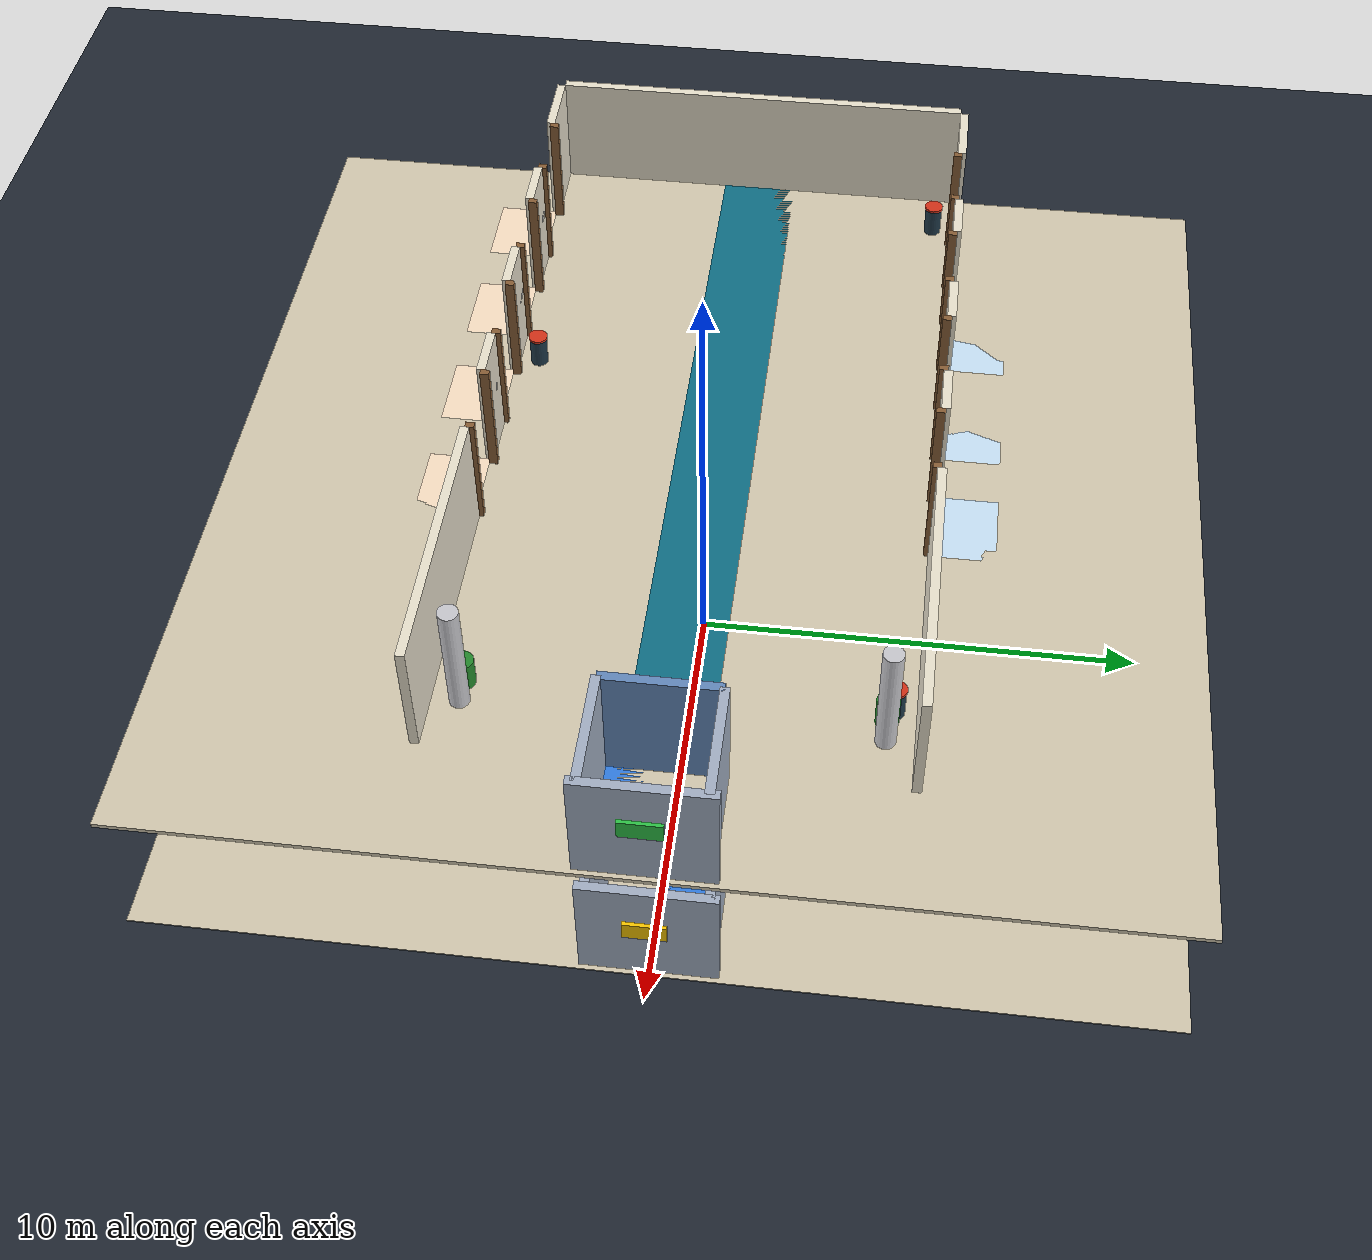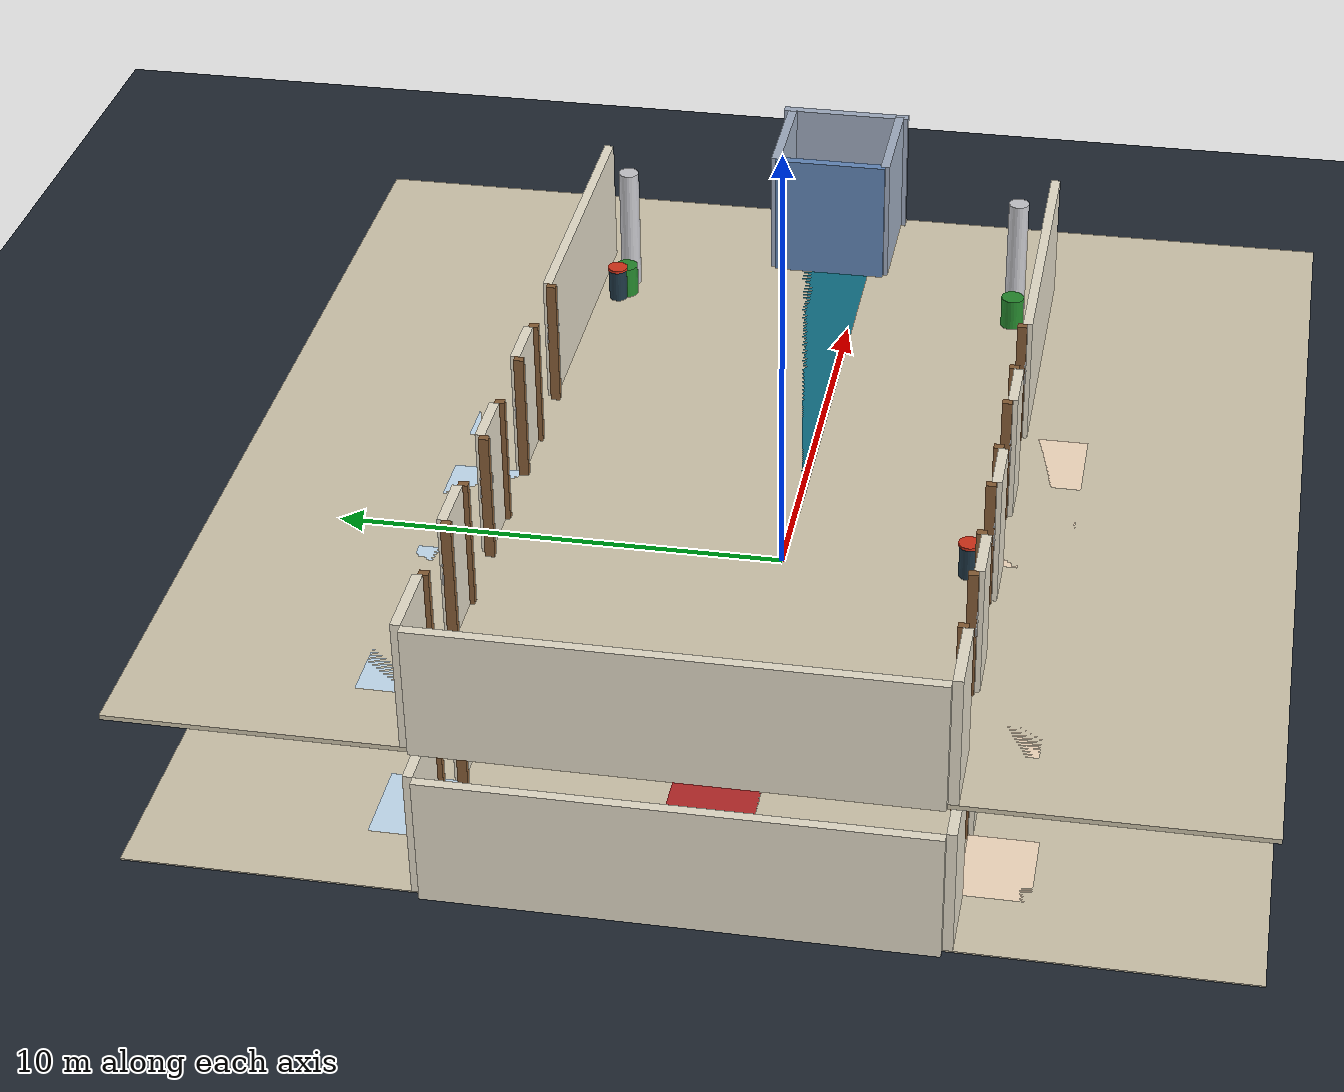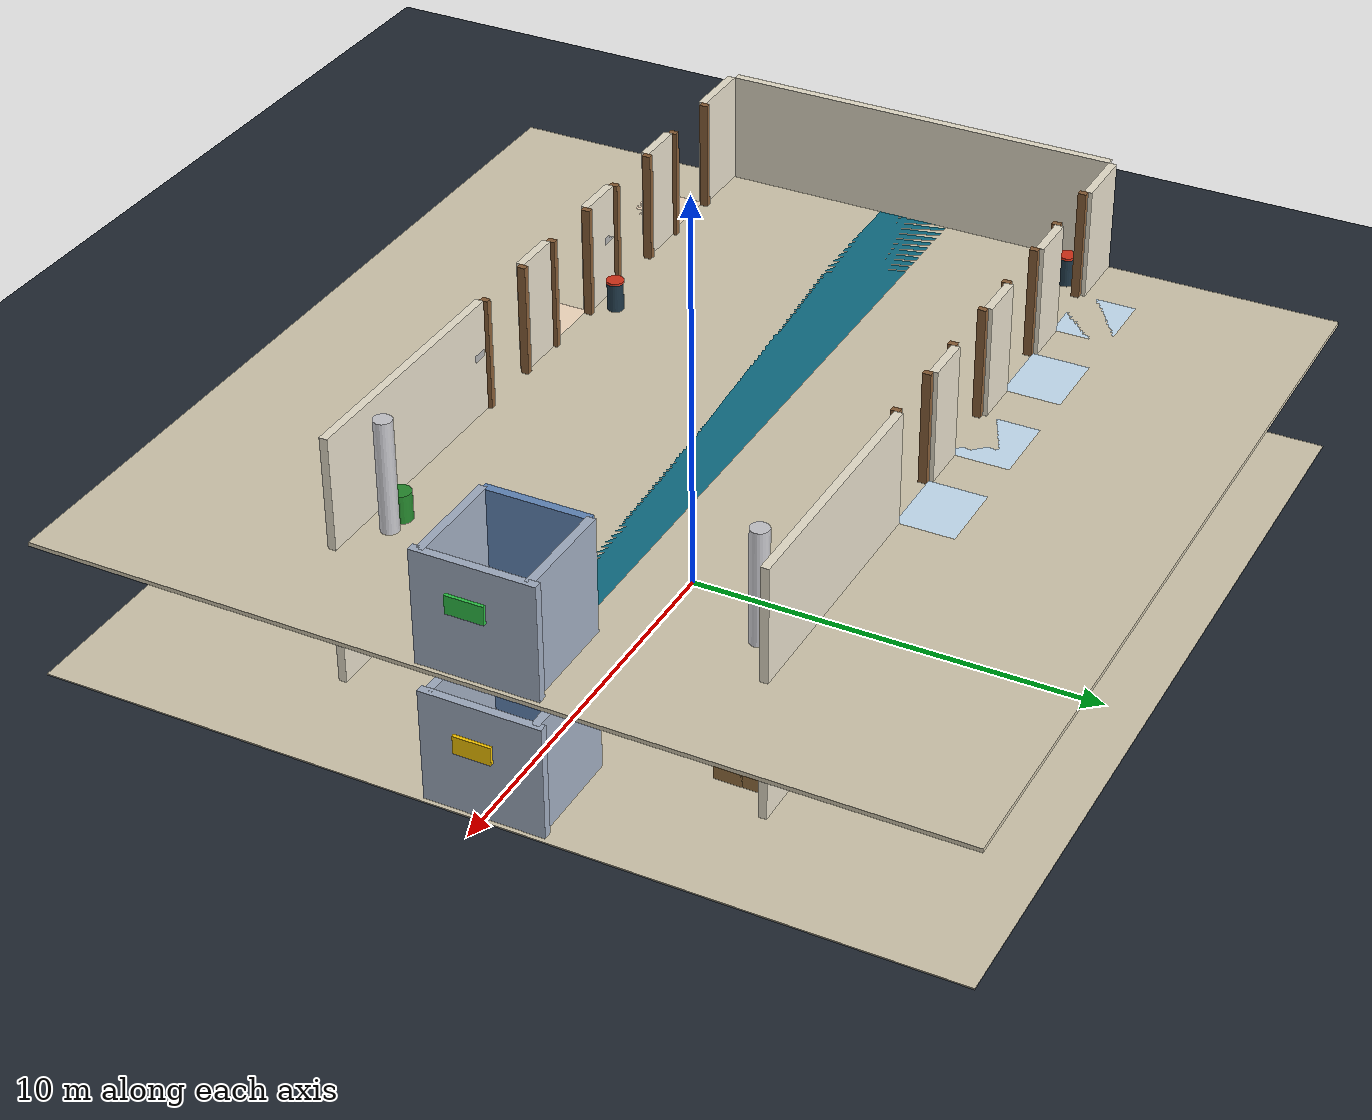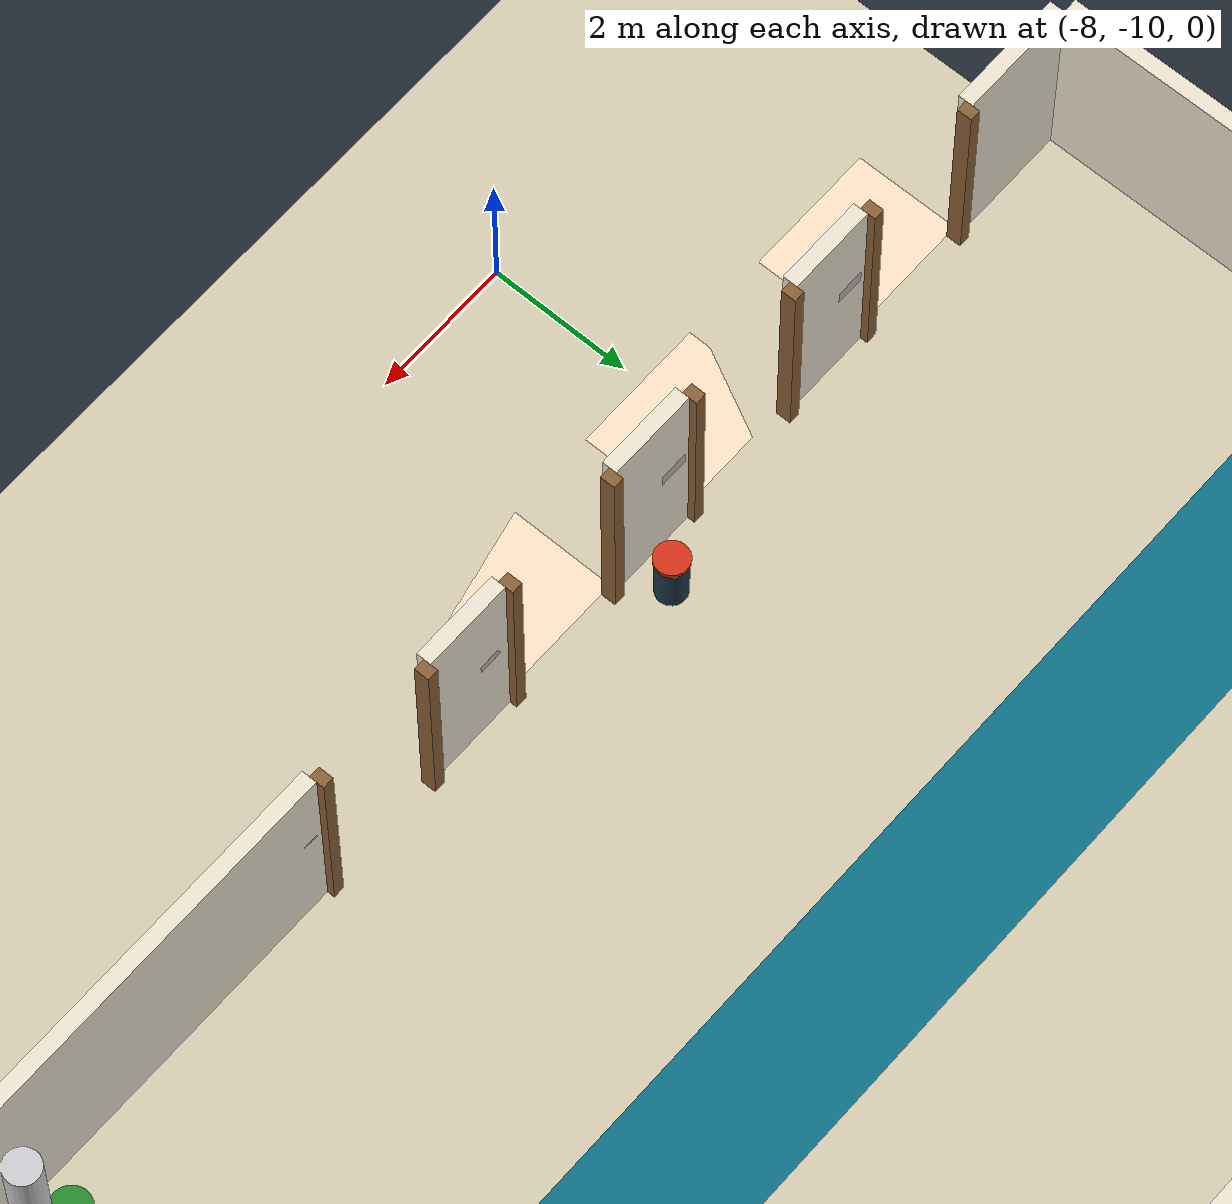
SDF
<sdf version="1.6">
 <world name="hotel_two_floor">
  <physics type="ode">
   <max_step_size>0.004</max_step_size>
   <real_time_factor>1</real_time_factor>
   <real_time_update_rate>250</real_time_update_rate>
  </physics>
  <light name="sun" type="directional">
   <pose>0 0 20 0 0 0</pose>
   <diffuse>0.9 0.9 0.85 1</diffuse>
   <specular>0.1 0.1 0.1 1</specular>
   <direction>-0.3 0.2 -0.9</direction>
  </light>
  <model name="ground_plane">
   <static>true</static>
   <link name="link">
    <collision name="col">
     <geometry><plane><normal>0 0 1</normal><size>100 100</size></plane></geometry>
    </collision>
    <visual name="vis">
     <geometry><plane><normal>0 0 1</normal><size>100 100</size></plane></geometry>
     <material><ambient>0.13 0.16 0.20 1</ambient><diffuse>0.13 0.16 0.20 1</diffuse></material>
    </visual>
   </link>
  </model>
  <plugin name="gazebo_ros_state" filename="libgazebo_ros_state.so">
   <ros><namespace>/</namespace></ros>
   <update_rate>10</update_rate>
  </plugin>
  <model name="f1_floor">
   <static>true</static>
   <pose>-1.2750 0.0000 -0.0500 0 0 0</pose>
   <link name="link">
    <collision name="col"><geometry><box><size>21.4500 22.0000 0.1000</size></box></geometry></collision>
    <visual name="vis">
     <geometry><box><size>21.4500 22.0000 0.1000</size></box></geometry>
     <material>
      <ambient>0.84 0.80 0.70 1</ambient>
      <diffuse>0.84 0.80 0.70 1</diffuse>
      <specular>0.10 0.10 0.10 1</specular>
     </material>
    </visual>
   </link>
  </model>
  <model name="f1_runner">
   <static>true</static>
   <pose>-2.6250 0.0000 -0.0100 0 0 0</pose>
   <link name="link">
    <visual name="vis">
     <geometry><box><size>18.7500 1.8000 0.0200</size></box></geometry>
     <material>
      <ambient>0.73 0.16 0.16 1</ambient>
      <diffuse>0.73 0.16 0.16 1</diffuse>
      <specular>0.20 0.20 0.20 1</specular>
     </material>
    </visual>
   </link>
  </model>
  <model name="f1_wall_west">
   <static>true</static>
   <pose>-12.1000 0.0000 1.4000 0 0 0</pose>
   <link name="link">
    <collision name="col"><geometry><box><size>0.2000 10.0000 2.8000</size></box></geometry></collision>
    <visual name="vis">
     <geometry><box><size>0.2000 10.0000 2.8000</size></box></geometry>
     <material>
      <ambient>0.93 0.90 0.82 1</ambient>
      <diffuse>0.93 0.90 0.82 1</diffuse>
      <specular>0.10 0.10 0.10 1</specular>
     </material>
    </visual>
   </link>
  </model>
  <model name="f1_seg_n_0">
   <static>true</static>
   <pose>-11.2000 5.1000 1.4000 0 0 0</pose>
   <link name="link">
    <collision name="col"><geometry><box><size>1.6000 0.2000 2.8000</size></box></geometry></collision>
    <visual name="vis">
     <geometry><box><size>1.6000 0.2000 2.8000</size></box></geometry>
     <material>
      <ambient>0.93 0.90 0.82 1</ambient>
      <diffuse>0.93 0.90 0.82 1</diffuse>
      <specular>0.10 0.10 0.10 1</specular>
     </material>
    </visual>
   </link>
  </model>
  <model name="f1_seg_s_0">
   <static>true</static>
   <pose>-11.2000 -5.1000 1.4000 0 0 0</pose>
   <link name="link">
    <collision name="col"><geometry><box><size>1.6000 0.2000 2.8000</size></box></geometry></collision>
    <visual name="vis">
     <geometry><box><size>1.6000 0.2000 2.8000</size></box></geometry>
     <material>
      <ambient>0.93 0.90 0.82 1</ambient>
      <diffuse>0.93 0.90 0.82 1</diffuse>
      <specular>0.10 0.10 0.10 1</specular>
     </material>
    </visual>
   </link>
  </model>
  <model name="f1_seg_n_1">
   <static>true</static>
   <pose>-8.0000 5.1000 1.4000 0 0 0</pose>
   <link name="link">
    <collision name="col"><geometry><box><size>1.2000 0.2000 2.8000</size></box></geometry></collision>
    <visual name="vis">
     <geometry><box><size>1.2000 0.2000 2.8000</size></box></geometry>
     <material>
      <ambient>0.93 0.90 0.82 1</ambient>
      <diffuse>0.93 0.90 0.82 1</diffuse>
      <specular>0.10 0.10 0.10 1</specular>
     </material>
    </visual>
   </link>
  </model>
  <model name="f1_seg_s_1">
   <static>true</static>
   <pose>-8.0000 -5.1000 1.4000 0 0 0</pose>
   <link name="link">
    <collision name="col"><geometry><box><size>1.2000 0.2000 2.8000</size></box></geometry></collision>
    <visual name="vis">
     <geometry><box><size>1.2000 0.2000 2.8000</size></box></geometry>
     <material>
      <ambient>0.93 0.90 0.82 1</ambient>
      <diffuse>0.93 0.90 0.82 1</diffuse>
      <specular>0.10 0.10 0.10 1</specular>
     </material>
    </visual>
   </link>
  </model>
  <model name="f1_seg_n_2">
   <static>true</static>
   <pose>-5.0000 5.1000 1.4000 0 0 0</pose>
   <link name="link">
    <collision name="col"><geometry><box><size>1.2000 0.2000 2.8000</size></box></geometry></collision>
    <visual name="vis">
     <geometry><box><size>1.2000 0.2000 2.8000</size></box></geometry>
     <material>
      <ambient>0.93 0.90 0.82 1</ambient>
      <diffuse>0.93 0.90 0.82 1</diffuse>
      <specular>0.10 0.10 0.10 1</specular>
     </material>
    </visual>
   </link>
  </model>
  <model name="f1_seg_s_2">
   <static>true</static>
   <pose>-5.0000 -5.1000 1.4000 0 0 0</pose>
   <link name="link">
    <collision name="col"><geometry><box><size>1.2000 0.2000 2.8000</size></box></geometry></collision>
    <visual name="vis">
     <geometry><box><size>1.2000 0.2000 2.8000</size></box></geometry>
     <material>
      <ambient>0.93 0.90 0.82 1</ambient>
      <diffuse>0.93 0.90 0.82 1</diffuse>
      <specular>0.10 0.10 0.10 1</specular>
     </material>
    </visual>
   </link>
  </model>
  <model name="f1_seg_n_3">
   <static>true</static>
   <pose>-2.0000 5.1000 1.4000 0 0 0</pose>
   <link name="link">
    <collision name="col"><geometry><box><size>1.2000 0.2000 2.8000</size></box></geometry></collision>
    <visual name="vis">
     <geometry><box><size>1.2000 0.2000 2.8000</size></box></geometry>
     <material>
      <ambient>0.93 0.90 0.82 1</ambient>
      <diffuse>0.93 0.90 0.82 1</diffuse>
      <specular>0.10 0.10 0.10 1</specular>
     </material>
    </visual>
   </link>
  </model>
  <model name="f1_seg_s_3">
   <static>true</static>
   <pose>-2.0000 -5.1000 1.4000 0 0 0</pose>
   <link name="link">
    <collision name="col"><geometry><box><size>1.2000 0.2000 2.8000</size></box></geometry></collision>
    <visual name="vis">
     <geometry><box><size>1.2000 0.2000 2.8000</size></box></geometry>
     <material>
      <ambient>0.93 0.90 0.82 1</ambient>
      <diffuse>0.93 0.90 0.82 1</diffuse>
      <specular>0.10 0.10 0.10 1</specular>
     </material>
    </visual>
   </link>
  </model>
  <model name="f1_seg_n_4">
   <static>true</static>
   <pose>3.5750 5.1000 1.4000 0 0 0</pose>
   <link name="link">
    <collision name="col"><geometry><box><size>6.3500 0.2000 2.8000</size></box></geometry></collision>
    <visual name="vis">
     <geometry><box><size>6.3500 0.2000 2.8000</size></box></geometry>
     <material>
      <ambient>0.93 0.90 0.82 1</ambient>
      <diffuse>0.93 0.90 0.82 1</diffuse>
      <specular>0.10 0.10 0.10 1</specular>
     </material>
    </visual>
   </link>
  </model>
  <model name="f1_seg_s_4">
   <static>true</static>
   <pose>3.5750 -5.1000 1.4000 0 0 0</pose>
   <link name="link">
    <collision name="col"><geometry><box><size>6.3500 0.2000 2.8000</size></box></geometry></collision>
    <visual name="vis">
     <geometry><box><size>6.3500 0.2000 2.8000</size></box></geometry>
     <material>
      <ambient>0.93 0.90 0.82 1</ambient>
      <diffuse>0.93 0.90 0.82 1</diffuse>
      <specular>0.10 0.10 0.10 1</specular>
     </material>
    </visual>
   </link>
  </model>
  <model name="f1_dp_s0L">
   <static>true</static>
   <pose>-10.3250 -5.0000 1.4000 0 0 0</pose>
   <link name="link">
    <collision name="col"><geometry><box><size>0.1500 0.2000 2.8000</size></box></geometry></collision>
    <visual name="vis">
     <geometry><box><size>0.1500 0.2000 2.8000</size></box></geometry>
     <material>
      <ambient>0.55 0.38 0.22 1</ambient>
      <diffuse>0.55 0.38 0.22 1</diffuse>
      <specular>0.20 0.20 0.20 1</specular>
     </material>
    </visual>
   </link>
  </model>
  <model name="f1_dp_s0R">
   <static>true</static>
   <pose>-8.6750 -5.0000 1.4000 0 0 0</pose>
   <link name="link">
    <collision name="col"><geometry><box><size>0.1500 0.2000 2.8000</size></box></geometry></collision>
    <visual name="vis">
     <geometry><box><size>0.1500 0.2000 2.8000</size></box></geometry>
     <material>
      <ambient>0.55 0.38 0.22 1</ambient>
      <diffuse>0.55 0.38 0.22 1</diffuse>
      <specular>0.20 0.20 0.20 1</specular>
     </material>
    </visual>
   </link>
  </model>
  <model name="f1_sign_s0">
   <static>true</static>
   <pose>-8.3500 -5.0250 1.5000 0 0 0</pose>
   <link name="link">
    <collision name="col"><geometry><box><size>0.3800 0.0500 0.1800</size></box></geometry></collision>
    <visual name="vis">
     <geometry><box><size>0.3800 0.0500 0.1800</size></box></geometry>
     <material>
      <material>
       <ambient>0.90 0.36 0.10 1</ambient>
       <diffuse>0.90 0.36 0.10 1</diffuse>
       <specular>0.10 0.10 0.10 1</specular>
      </material>
     </material>
    </visual>
   </link>
  </model>
  <model name="f1_lbl_s0">
   <static>true</static>
   <pose>-8.3500 -5.0550 1.5000 0 0 0</pose>
   <link name="link">
    <visual name="vis">
     <geometry><box><size>0.2800 0.0100 0.1200</size></box></geometry>
     <material>
      <material>
       <ambient>0.97 0.97 0.97 1</ambient>
       <diffuse>0.97 0.97 0.97 1</diffuse>
       <specular>0.10 0.10 0.10 1</specular>
      </material>
     </material>
    </visual>
   </link>
  </model>
  <model name="f1_dp_n0L">
   <static>true</static>
   <pose>-10.3250 5.0000 1.4000 0 0 0</pose>
   <link name="link">
    <collision name="col"><geometry><box><size>0.1500 0.2000 2.8000</size></box></geometry></collision>
    <visual name="vis">
     <geometry><box><size>0.1500 0.2000 2.8000</size></box></geometry>
     <material>
      <ambient>0.55 0.38 0.22 1</ambient>
      <diffuse>0.55 0.38 0.22 1</diffuse>
      <specular>0.20 0.20 0.20 1</specular>
     </material>
    </visual>
   </link>
  </model>
  <model name="f1_dp_n0R">
   <static>true</static>
   <pose>-8.6750 5.0000 1.4000 0 0 0</pose>
   <link name="link">
    <collision name="col"><geometry><box><size>0.1500 0.2000 2.8000</size></box></geometry></collision>
    <visual name="vis">
     <geometry><box><size>0.1500 0.2000 2.8000</size></box></geometry>
     <material>
      <ambient>0.55 0.38 0.22 1</ambient>
      <diffuse>0.55 0.38 0.22 1</diffuse>
      <specular>0.20 0.20 0.20 1</specular>
     </material>
    </visual>
   </link>
  </model>
  <model name="f1_sign_n0">
   <static>true</static>
   <pose>-8.3500 5.0250 1.5000 0 0 0</pose>
   <link name="link">
    <collision name="col"><geometry><box><size>0.3800 0.0500 0.1800</size></box></geometry></collision>
    <visual name="vis">
     <geometry><box><size>0.3800 0.0500 0.1800</size></box></geometry>
     <material>
      <material>
       <ambient>0.11 0.43 0.82 1</ambient>
       <diffuse>0.11 0.43 0.82 1</diffuse>
       <specular>0.10 0.10 0.10 1</specular>
      </material>
     </material>
    </visual>
   </link>
  </model>
  <model name="f1_lbl_n0">
   <static>true</static>
   <pose>-8.3500 5.0550 1.5000 0 0 0</pose>
   <link name="link">
    <visual name="vis">
     <geometry><box><size>0.2800 0.0100 0.1200</size></box></geometry>
     <material>
      <material>
       <ambient>0.97 0.97 0.97 1</ambient>
       <diffuse>0.97 0.97 0.97 1</diffuse>
       <specular>0.10 0.10 0.10 1</specular>
      </material>
     </material>
    </visual>
   </link>
  </model>
  <model name="f1_dp_s1L">
   <static>true</static>
   <pose>-7.3250 -5.0000 1.4000 0 0 0</pose>
   <link name="link">
    <collision name="col"><geometry><box><size>0.1500 0.2000 2.8000</size></box></geometry></collision>
    <visual name="vis">
     <geometry><box><size>0.1500 0.2000 2.8000</size></box></geometry>
     <material>
      <ambient>0.55 0.38 0.22 1</ambient>
      <diffuse>0.55 0.38 0.22 1</diffuse>
      <specular>0.20 0.20 0.20 1</specular>
     </material>
    </visual>
   </link>
  </model>
  <model name="f1_dp_s1R">
   <static>true</static>
   <pose>-5.6750 -5.0000 1.4000 0 0 0</pose>
   <link name="link">
    <collision name="col"><geometry><box><size>0.1500 0.2000 2.8000</size></box></geometry></collision>
    <visual name="vis">
     <geometry><box><size>0.1500 0.2000 2.8000</size></box></geometry>
     <material>
      <ambient>0.55 0.38 0.22 1</ambient>
      <diffuse>0.55 0.38 0.22 1</diffuse>
      <specular>0.20 0.20 0.20 1</specular>
     </material>
    </visual>
   </link>
  </model>
  <model name="f1_sign_s1">
   <static>true</static>
   <pose>-5.3500 -5.0250 1.5000 0 0 0</pose>
   <link name="link">
    <collision name="col"><geometry><box><size>0.3800 0.0500 0.1800</size></box></geometry></collision>
    <visual name="vis">
     <geometry><box><size>0.3800 0.0500 0.1800</size></box></geometry>
     <material>
      <material>
       <ambient>0.90 0.36 0.10 1</ambient>
       <diffuse>0.90 0.36 0.10 1</diffuse>
       <specular>0.10 0.10 0.10 1</specular>
      </material>
     </material>
    </visual>
   </link>
  </model>
  <model name="f1_lbl_s1">
   <static>true</static>
   <pose>-5.3500 -5.0550 1.5000 0 0 0</pose>
   <link name="link">
    <visual name="vis">
     <geometry><box><size>0.2800 0.0100 0.1200</size></box></geometry>
     <material>
      <material>
       <ambient>0.97 0.97 0.97 1</ambient>
       <diffuse>0.97 0.97 0.97 1</diffuse>
       <specular>0.10 0.10 0.10 1</specular>
      </material>
     </material>
    </visual>
   </link>
  </model>
  <model name="f1_dp_n1L">
   <static>true</static>
   <pose>-7.3250 5.0000 1.4000 0 0 0</pose>
   <link name="link">
    <collision name="col"><geometry><box><size>0.1500 0.2000 2.8000</size></box></geometry></collision>
    <visual name="vis">
     <geometry><box><size>0.1500 0.2000 2.8000</size></box></geometry>
     <material>
      <ambient>0.55 0.38 0.22 1</ambient>
      <diffuse>0.55 0.38 0.22 1</diffuse>
      <specular>0.20 0.20 0.20 1</specular>
     </material>
    </visual>
   </link>
  </model>
  <model name="f1_dp_n1R">
   <static>true</static>
   <pose>-5.6750 5.0000 1.4000 0 0 0</pose>
   <link name="link">
    <collision name="col"><geometry><box><size>0.1500 0.2000 2.8000</size></box></geometry></collision>
    <visual name="vis">
     <geometry><box><size>0.1500 0.2000 2.8000</size></box></geometry>
     <material>
      <ambient>0.55 0.38 0.22 1</ambient>
      <diffuse>0.55 0.38 0.22 1</diffuse>
      <specular>0.20 0.20 0.20 1</specular>
     </material>
    </visual>
   </link>
  </model>
  <model name="f1_sign_n1">
   <static>true</static>
   <pose>-5.3500 5.0250 1.5000 0 0 0</pose>
   <link name="link">
    <collision name="col"><geometry><box><size>0.3800 0.0500 0.1800</size></box></geometry></collision>
    <visual name="vis">
     <geometry><box><size>0.3800 0.0500 0.1800</size></box></geometry>
     <material>
      <material>
       <ambient>0.11 0.43 0.82 1</ambient>
       <diffuse>0.11 0.43 0.82 1</diffuse>
       <specular>0.10 0.10 0.10 1</specular>
      </material>
     </material>
    </visual>
   </link>
  </model>
  <model name="f1_lbl_n1">
   <static>true</static>
   <pose>-5.3500 5.0550 1.5000 0 0 0</pose>
   <link name="link">
    <visual name="vis">
     <geometry><box><size>0.2800 0.0100 0.1200</size></box></geometry>
     <material>
      <material>
       <ambient>0.97 0.97 0.97 1</ambient>
       <diffuse>0.97 0.97 0.97 1</diffuse>
       <specular>0.10 0.10 0.10 1</specular>
      </material>
     </material>
    </visual>
   </link>
  </model>
  <model name="f1_dp_s2L">
   <static>true</static>
   <pose>-4.3250 -5.0000 1.4000 0 0 0</pose>
   <link name="link">
    <collision name="col"><geometry><box><size>0.1500 0.2000 2.8000</size></box></geometry></collision>
    <visual name="vis">
     <geometry><box><size>0.1500 0.2000 2.8000</size></box></geometry>
     <material>
      <ambient>0.55 0.38 0.22 1</ambient>
      <diffuse>0.55 0.38 0.22 1</diffuse>
      <specular>0.20 0.20 0.20 1</specular>
     </material>
    </visual>
   </link>
  </model>
  <model name="f1_dp_s2R">
   <static>true</static>
   <pose>-2.6750 -5.0000 1.4000 0 0 0</pose>
   <link name="link">
    <collision name="col"><geometry><box><size>0.1500 0.2000 2.8000</size></box></geometry></collision>
    <visual name="vis">
     <geometry><box><size>0.1500 0.2000 2.8000</size></box></geometry>
     <material>
      <ambient>0.55 0.38 0.22 1</ambient>
      <diffuse>0.55 0.38 0.22 1</diffuse>
      <specular>0.20 0.20 0.20 1</specular>
     </material>
    </visual>
   </link>
  </model>
  <model name="f1_sign_s2">
   <static>true</static>
   <pose>-2.3500 -5.0250 1.5000 0 0 0</pose>
   <link name="link">
    <collision name="col"><geometry><box><size>0.3800 0.0500 0.1800</size></box></geometry></collision>
    <visual name="vis">
     <geometry><box><size>0.3800 0.0500 0.1800</size></box></geometry>
     <material>
      <material>
       <ambient>0.90 0.36 0.10 1</ambient>
       <diffuse>0.90 0.36 0.10 1</diffuse>
       <specular>0.10 0.10 0.10 1</specular>
      </material>
     </material>
    </visual>
   </link>
  </model>
  <model name="f1_lbl_s2">
   <static>true</static>
   <pose>-2.3500 -5.0550 1.5000 0 0 0</pose>
   <link name="link">
    <visual name="vis">
     <geometry><box><size>0.2800 0.0100 0.1200</size></box></geometry>
     <material>
      <material>
       <ambient>0.97 0.97 0.97 1</ambient>
       <diffuse>0.97 0.97 0.97 1</diffuse>
       <specular>0.10 0.10 0.10 1</specular>
      </material>
     </material>
    </visual>
   </link>
  </model>
  <model name="f1_dp_n2L">
   <static>true</static>
   <pose>-4.3250 5.0000 1.4000 0 0 0</pose>
   <link name="link">
    <collision name="col"><geometry><box><size>0.1500 0.2000 2.8000</size></box></geometry></collision>
    <visual name="vis">
     <geometry><box><size>0.1500 0.2000 2.8000</size></box></geometry>
     <material>
      <ambient>0.55 0.38 0.22 1</ambient>
      <diffuse>0.55 0.38 0.22 1</diffuse>
      <specular>0.20 0.20 0.20 1</specular>
     </material>
    </visual>
   </link>
  </model>
  <model name="f1_dp_n2R">
   <static>true</static>
   <pose>-2.6750 5.0000 1.4000 0 0 0</pose>
   <link name="link">
    <collision name="col"><geometry><box><size>0.1500 0.2000 2.8000</size></box></geometry></collision>
    <visual name="vis">
     <geometry><box><size>0.1500 0.2000 2.8000</size></box></geometry>
     <material>
      <ambient>0.55 0.38 0.22 1</ambient>
      <diffuse>0.55 0.38 0.22 1</diffuse>
      <specular>0.20 0.20 0.20 1</specular>
     </material>
    </visual>
   </link>
  </model>
  <model name="f1_sign_n2">
   <static>true</static>
   <pose>-2.3500 5.0250 1.5000 0 0 0</pose>
   <link name="link">
    <collision name="col"><geometry><box><size>0.3800 0.0500 0.1800</size></box></geometry></collision>
    <visual name="vis">
     <geometry><box><size>0.3800 0.0500 0.1800</size></box></geometry>
     <material>
      <material>
       <ambient>0.11 0.43 0.82 1</ambient>
       <diffuse>0.11 0.43 0.82 1</diffuse>
       <specular>0.10 0.10 0.10 1</specular>
      </material>
     </material>
    </visual>
   </link>
  </model>
  <model name="f1_lbl_n2">
   <static>true</static>
   <pose>-2.3500 5.0550 1.5000 0 0 0</pose>
   <link name="link">
    <visual name="vis">
     <geometry><box><size>0.2800 0.0100 0.1200</size></box></geometry>
     <material>
      <material>
       <ambient>0.97 0.97 0.97 1</ambient>
       <diffuse>0.97 0.97 0.97 1</diffuse>
       <specular>0.10 0.10 0.10 1</specular>
      </material>
     </material>
    </visual>
   </link>
  </model>
  <model name="f1_dp_s3L">
   <static>true</static>
   <pose>-1.3250 -5.0000 1.4000 0 0 0</pose>
   <link name="link">
    <collision name="col"><geometry><box><size>0.1500 0.2000 2.8000</size></box></geometry></collision>
    <visual name="vis">
     <geometry><box><size>0.1500 0.2000 2.8000</size></box></geometry>
     <material>
      <ambient>0.55 0.38 0.22 1</ambient>
      <diffuse>0.55 0.38 0.22 1</diffuse>
      <specular>0.20 0.20 0.20 1</specular>
     </material>
    </visual>
   </link>
  </model>
  <model name="f1_dp_s3R">
   <static>true</static>
   <pose>0.3250 -5.0000 1.4000 0 0 0</pose>
   <link name="link">
    <collision name="col"><geometry><box><size>0.1500 0.2000 2.8000</size></box></geometry></collision>
    <visual name="vis">
     <geometry><box><size>0.1500 0.2000 2.8000</size></box></geometry>
     <material>
      <ambient>0.55 0.38 0.22 1</ambient>
      <diffuse>0.55 0.38 0.22 1</diffuse>
      <specular>0.20 0.20 0.20 1</specular>
     </material>
    </visual>
   </link>
  </model>
  <model name="f1_sign_s3">
   <static>true</static>
   <pose>0.6500 -5.0250 1.5000 0 0 0</pose>
   <link name="link">
    <collision name="col"><geometry><box><size>0.3800 0.0500 0.1800</size></box></geometry></collision>
    <visual name="vis">
     <geometry><box><size>0.3800 0.0500 0.1800</size></box></geometry>
     <material>
      <material>
       <ambient>0.90 0.36 0.10 1</ambient>
       <diffuse>0.90 0.36 0.10 1</diffuse>
       <specular>0.10 0.10 0.10 1</specular>
      </material>
     </material>
    </visual>
   </link>
  </model>
  <model name="f1_lbl_s3">
   <static>true</static>
   <pose>0.6500 -5.0550 1.5000 0 0 0</pose>
   <link name="link">
    <visual name="vis">
     <geometry><box><size>0.2800 0.0100 0.1200</size></box></geometry>
     <material>
      <material>
       <ambient>0.97 0.97 0.97 1</ambient>
       <diffuse>0.97 0.97 0.97 1</diffuse>
       <specular>0.10 0.10 0.10 1</specular>
      </material>
     </material>
    </visual>
   </link>
  </model>
  <model name="f1_dp_n3L">
   <static>true</static>
   <pose>-1.3250 5.0000 1.4000 0 0 0</pose>
   <link name="link">
    <collision name="col"><geometry><box><size>0.1500 0.2000 2.8000</size></box></geometry></collision>
    <visual name="vis">
     <geometry><box><size>0.1500 0.2000 2.8000</size></box></geometry>
     <material>
      <ambient>0.55 0.38 0.22 1</ambient>
      <diffuse>0.55 0.38 0.22 1</diffuse>
      <specular>0.20 0.20 0.20 1</specular>
     </material>
    </visual>
   </link>
  </model>
  <model name="f1_dp_n3R">
   <static>true</static>
   <pose>0.3250 5.0000 1.4000 0 0 0</pose>
   <link name="link">
    <collision name="col"><geometry><box><size>0.1500 0.2000 2.8000</size></box></geometry></collision>
    <visual name="vis">
     <geometry><box><size>0.1500 0.2000 2.8000</size></box></geometry>
     <material>
      <ambient>0.55 0.38 0.22 1</ambient>
      <diffuse>0.55 0.38 0.22 1</diffuse>
      <specular>0.20 0.20 0.20 1</specular>
     </material>
    </visual>
   </link>
  </model>
  <model name="f1_sign_n3">
   <static>true</static>
   <pose>0.6500 5.0250 1.5000 0 0 0</pose>
   <link name="link">
    <collision name="col"><geometry><box><size>0.3800 0.0500 0.1800</size></box></geometry></collision>
    <visual name="vis">
     <geometry><box><size>0.3800 0.0500 0.1800</size></box></geometry>
     <material>
      <material>
       <ambient>0.11 0.43 0.82 1</ambient>
       <diffuse>0.11 0.43 0.82 1</diffuse>
       <specular>0.10 0.10 0.10 1</specular>
      </material>
     </material>
    </visual>
   </link>
  </model>
  <model name="f1_lbl_n3">
   <static>true</static>
   <pose>0.6500 5.0550 1.5000 0 0 0</pose>
   <link name="link">
    <visual name="vis">
     <geometry><box><size>0.2800 0.0100 0.1200</size></box></geometry>
     <material>
      <material>
       <ambient>0.97 0.97 0.97 1</ambient>
       <diffuse>0.97 0.97 0.97 1</diffuse>
       <specular>0.10 0.10 0.10 1</specular>
      </material>
     </material>
    </visual>
   </link>
  </model>
  <model name="f1_elev_back">
   <static>true</static>
   <pose>9.2500 0.0000 1.4000 0 0 0</pose>
   <link name="link">
    <collision name="col"><geometry><box><size>0.2000 2.9000 2.8000</size></box></geometry></collision>
    <visual name="vis">
     <geometry><box><size>0.2000 2.9000 2.8000</size></box></geometry>
     <material>
      <ambient>0.65 0.70 0.78 1</ambient>
      <diffuse>0.65 0.70 0.78 1</diffuse>
      <specular>0.60 0.60 0.60 1</specular>
     </material>
    </visual>
   </link>
  </model>
  <model name="f1_elev_L">
   <static>true</static>
   <pose>8.0000 -1.2500 1.4000 0 0 0</pose>
   <link name="link">
    <collision name="col"><geometry><box><size>2.5000 0.2000 2.8000</size></box></geometry></collision>
    <visual name="vis">
     <geometry><box><size>2.5000 0.2000 2.8000</size></box></geometry>
     <material>
      <ambient>0.65 0.70 0.78 1</ambient>
      <diffuse>0.65 0.70 0.78 1</diffuse>
      <specular>0.60 0.60 0.60 1</specular>
     </material>
    </visual>
   </link>
  </model>
  <model name="f1_elev_R">
   <static>true</static>
   <pose>8.0000 1.2500 1.4000 0 0 0</pose>
   <link name="link">
    <collision name="col"><geometry><box><size>2.5000 0.2000 2.8000</size></box></geometry></collision>
    <visual name="vis">
     <geometry><box><size>2.5000 0.2000 2.8000</size></box></geometry>
     <material>
      <ambient>0.65 0.70 0.78 1</ambient>
      <diffuse>0.65 0.70 0.78 1</diffuse>
      <specular>0.60 0.60 0.60 1</specular>
     </material>
    </visual>
   </link>
  </model>
  <model name="f1_elev_floor">
   <static>true</static>
   <pose>8.0000 0.0000 -0.0200 0 0 0</pose>
   <link name="link">
    <collision name="col"><geometry><box><size>2.5000 2.5000 0.0400</size></box></geometry></collision>
    <visual name="vis">
     <geometry><box><size>2.5000 2.5000 0.0400</size></box></geometry>
     <material>
      <ambient>0.20 0.50 0.90 1</ambient>
      <diffuse>0.20 0.50 0.90 1</diffuse>
      <specular>0.40 0.40 0.40 1</specular>
     </material>
    </visual>
   </link>
  </model>
  <model name="f1_kat_sign">
   <static>true</static>
   <pose>9.6500 0.0000 2.0000 0 0 0</pose>
   <link name="link">
    <collision name="col"><geometry><box><size>0.0800 0.9000 0.4500</size></box></geometry></collision>
    <visual name="vis">
     <geometry><box><size>0.0800 0.9000 0.4500</size></box></geometry>
     <material>
      <ambient>1.00 0.80 0.00 1</ambient>
      <diffuse>1.00 0.80 0.00 1</diffuse>
      <specular>0.10 0.10 0.10 1</specular>
     </material>
    </visual>
   </link>
  </model>
  <model name="f1_elev_door">
   <static>false</static>
   <pose>6.7500 0.0000 1.4000 0 0 0</pose>
   <link name="door">
    <gravity>false</gravity>
    <kinematic>true</kinematic>
    <inertial>
     <mass>50.0</mass>
     <inertia><ixx>10</ixx><ixy>0</ixy><ixz>0</ixz><iyy>10</iyy><iyz>0</iyz><izz>10</izz></inertia>
    </inertial>
    <collision name="col"><geometry><box><size>0.2000 2.5000 2.8000</size></box></geometry></collision>
    <visual name="vis">
     <geometry><box><size>0.2000 2.5000 2.8000</size></box></geometry>
     <material>
      <ambient>0.40 0.55 0.75 1</ambient>
      <diffuse>0.40 0.55 0.75 1</diffuse>
      <specular>0.80 0.80 0.80 1</specular>
     </material>
    </visual>
   </link>
  </model>
  <model name="f1_recep_main">
   <static>true</static>
   <pose>4.9500 4.4000 0.5500 0 0 0</pose>
   <link name="link">
    <collision name="col"><geometry><box><size>2.2000 0.5000 1.1000</size></box></geometry></collision>
    <visual name="vis">
     <geometry><box><size>2.2000 0.5000 1.1000</size></box></geometry>
     <material>
      <ambient>0.60 0.45 0.25 1</ambient>
      <diffuse>0.60 0.45 0.25 1</diffuse>
      <specular>0.30 0.30 0.30 1</specular>
     </material>
    </visual>
   </link>
  </model>
  <model name="f1_recep_top">
   <static>true</static>
   <pose>4.9500 4.4000 1.1500 0 0 0</pose>
   <link name="link">
    <collision name="col"><geometry><box><size>2.4000 0.6500 0.0800</size></box></geometry></collision>
    <visual name="vis">
     <geometry><box><size>2.4000 0.6500 0.0800</size></box></geometry>
     <material>
      <ambient>0.60 0.45 0.25 1</ambient>
      <diffuse>0.60 0.45 0.25 1</diffuse>
      <specular>0.30 0.30 0.30 1</specular>
     </material>
    </visual>
   </link>
  </model>
  <model name="f1_recep_wing">
   <static>true</static>
   <pose>5.8000 3.9500 0.5500 0 0 0</pose>
   <link name="link">
    <collision name="col"><geometry><box><size>0.5000 0.7000 1.1000</size></box></geometry></collision>
    <visual name="vis">
     <geometry><box><size>0.5000 0.7000 1.1000</size></box></geometry>
     <material>
      <ambient>0.60 0.45 0.25 1</ambient>
      <diffuse>0.60 0.45 0.25 1</diffuse>
      <specular>0.30 0.30 0.30 1</specular>
     </material>
    </visual>
   </link>
  </model>
  <model name="f1_pad_n_0">
   <static>true</static>
   <pose>-9.5000 5.8000 -0.0100 0 0 0</pose>
   <link name="link">
    <visual name="vis">
     <geometry><box><size>1.8000 1.4000 0.0200</size></box></geometry>
     <material>
      <ambient>0.80 0.90 0.98 1</ambient>
      <diffuse>0.80 0.90 0.98 1</diffuse>
      <specular>0.10 0.10 0.10 1</specular>
     </material>
    </visual>
   </link>
  </model>
  <model name="f1_pad_s_0">
   <static>true</static>
   <pose>-9.5000 -5.8000 -0.0100 0 0 0</pose>
   <link name="link">
    <visual name="vis">
     <geometry><box><size>1.8000 1.4000 0.0200</size></box></geometry>
     <material>
      <ambient>0.99 0.89 0.78 1</ambient>
      <diffuse>0.99 0.89 0.78 1</diffuse>
      <specular>0.10 0.10 0.10 1</specular>
     </material>
    </visual>
   </link>
  </model>
  <model name="f1_room_n_105_0_b">
   <static>true</static>
   <pose>-8.5100 5.1000 1.7550 0 0 0</pose>
   <link name="link">
    <visual name="vis">
     <geometry><box><size>0.0500 0.0200 0.2100</size></box></geometry>
     <material>
      <ambient>0.98 0.98 0.98 1</ambient>
      <diffuse>0.98 0.98 0.98 1</diffuse>
      <specular>0.20 0.20 0.20 1</specular>
     </material>
    </visual>
   </link>
  </model>
  <model name="f1_room_n_105_0_c">
   <static>true</static>
   <pose>-8.5100 5.1000 1.5450 0 0 0</pose>
   <link name="link">
    <visual name="vis">
     <geometry><box><size>0.0500 0.0200 0.2100</size></box></geometry>
     <material>
      <ambient>0.98 0.98 0.98 1</ambient>
      <diffuse>0.98 0.98 0.98 1</diffuse>
      <specular>0.20 0.20 0.20 1</specular>
     </material>
    </visual>
   </link>
  </model>
  <model name="f1_room_n_105_1_a">
   <static>true</static>
   <pose>-8.3000 5.1000 1.8600 0 0 0</pose>
   <link name="link">
    <visual name="vis">
     <geometry><box><size>0.2600 0.0200 0.0500</size></box></geometry>
     <material>
      <ambient>0.98 0.98 0.98 1</ambient>
      <diffuse>0.98 0.98 0.98 1</diffuse>
      <specular>0.20 0.20 0.20 1</specular>
     </material>
    </visual>
   </link>
  </model>
  <model name="f1_room_n_105_1_b">
   <static>true</static>
   <pose>-8.1700 5.1000 1.7550 0 0 0</pose>
   <link name="link">
    <visual name="vis">
     <geometry><box><size>0.0500 0.0200 0.2100</size></box></geometry>
     <material>
      <ambient>0.98 0.98 0.98 1</ambient>
      <diffuse>0.98 0.98 0.98 1</diffuse>
      <specular>0.20 0.20 0.20 1</specular>
     </material>
    </visual>
   </link>
  </model>
  <model name="f1_room_n_105_1_c">
   <static>true</static>
   <pose>-8.1700 5.1000 1.5450 0 0 0</pose>
   <link name="link">
    <visual name="vis">
     <geometry><box><size>0.0500 0.0200 0.2100</size></box></geometry>
     <material>
      <ambient>0.98 0.98 0.98 1</ambient>
      <diffuse>0.98 0.98 0.98 1</diffuse>
      <specular>0.20 0.20 0.20 1</specular>
     </material>
    </visual>
   </link>
  </model>
  <model name="f1_room_n_105_1_f">
   <static>true</static>
   <pose>-8.4300 5.1000 1.7550 0 0 0</pose>
   <link name="link">
    <visual name="vis">
     <geometry><box><size>0.0500 0.0200 0.2100</size></box></geometry>
     <material>
      <ambient>0.98 0.98 0.98 1</ambient>
      <diffuse>0.98 0.98 0.98 1</diffuse>
      <specular>0.20 0.20 0.20 1</specular>
     </material>
    </visual>
   </link>
  </model>
  <model name="f1_room_n_105_1_e">
   <static>true</static>
   <pose>-8.4300 5.1000 1.5450 0 0 0</pose>
   <link name="link">
    <visual name="vis">
     <geometry><box><size>0.0500 0.0200 0.2100</size></box></geometry>
     <material>
      <ambient>0.98 0.98 0.98 1</ambient>
      <diffuse>0.98 0.98 0.98 1</diffuse>
      <specular>0.20 0.20 0.20 1</specular>
     </material>
    </visual>
   </link>
  </model>
  <model name="f1_room_n_105_1_d">
   <static>true</static>
   <pose>-8.3000 5.1000 1.4400 0 0 0</pose>
   <link name="link">
    <visual name="vis">
     <geometry><box><size>0.2600 0.0200 0.0500</size></box></geometry>
     <material>
      <ambient>0.98 0.98 0.98 1</ambient>
      <diffuse>0.98 0.98 0.98 1</diffuse>
      <specular>0.20 0.20 0.20 1</specular>
     </material>
    </visual>
   </link>
  </model>
  <model name="f1_room_n_105_2_a">
   <static>true</static>
   <pose>-7.9600 5.1000 1.8600 0 0 0</pose>
   <link name="link">
    <visual name="vis">
     <geometry><box><size>0.2600 0.0200 0.0500</size></box></geometry>
     <material>
      <ambient>0.98 0.98 0.98 1</ambient>
      <diffuse>0.98 0.98 0.98 1</diffuse>
      <specular>0.20 0.20 0.20 1</specular>
     </material>
    </visual>
   </link>
  </model>
  <model name="f1_room_n_105_2_f">
   <static>true</static>
   <pose>-8.0900 5.1000 1.7550 0 0 0</pose>
   <link name="link">
    <visual name="vis">
     <geometry><box><size>0.0500 0.0200 0.2100</size></box></geometry>
     <material>
      <ambient>0.98 0.98 0.98 1</ambient>
      <diffuse>0.98 0.98 0.98 1</diffuse>
      <specular>0.20 0.20 0.20 1</specular>
     </material>
    </visual>
   </link>
  </model>
  <model name="f1_room_n_105_2_g">
   <static>true</static>
   <pose>-7.9600 5.1000 1.6500 0 0 0</pose>
   <link name="link">
    <visual name="vis">
     <geometry><box><size>0.2600 0.0200 0.0500</size></box></geometry>
     <material>
      <ambient>0.98 0.98 0.98 1</ambient>
      <diffuse>0.98 0.98 0.98 1</diffuse>
      <specular>0.20 0.20 0.20 1</specular>
     </material>
    </visual>
   </link>
  </model>
  <model name="f1_room_n_105_2_c">
   <static>true</static>
   <pose>-7.8300 5.1000 1.5450 0 0 0</pose>
   <link name="link">
    <visual name="vis">
     <geometry><box><size>0.0500 0.0200 0.2100</size></box></geometry>
     <material>
      <ambient>0.98 0.98 0.98 1</ambient>
      <diffuse>0.98 0.98 0.98 1</diffuse>
      <specular>0.20 0.20 0.20 1</specular>
     </material>
    </visual>
   </link>
  </model>
  <model name="f1_room_n_105_2_d">
   <static>true</static>
   <pose>-7.9600 5.1000 1.4400 0 0 0</pose>
   <link name="link">
    <visual name="vis">
     <geometry><box><size>0.2600 0.0200 0.0500</size></box></geometry>
     <material>
      <ambient>0.98 0.98 0.98 1</ambient>
      <diffuse>0.98 0.98 0.98 1</diffuse>
      <specular>0.20 0.20 0.20 1</specular>
     </material>
    </visual>
   </link>
  </model>
  <model name="f1_room_s_101_0_b">
   <static>true</static>
   <pose>-8.5100 -5.1000 1.7550 0 0 0</pose>
   <link name="link">
    <visual name="vis">
     <geometry><box><size>0.0500 0.0200 0.2100</size></box></geometry>
     <material>
      <ambient>0.98 0.98 0.98 1</ambient>
      <diffuse>0.98 0.98 0.98 1</diffuse>
      <specular>0.20 0.20 0.20 1</specular>
     </material>
    </visual>
   </link>
  </model>
  <model name="f1_room_s_101_0_c">
   <static>true</static>
   <pose>-8.5100 -5.1000 1.5450 0 0 0</pose>
   <link name="link">
    <visual name="vis">
     <geometry><box><size>0.0500 0.0200 0.2100</size></box></geometry>
     <material>
      <ambient>0.98 0.98 0.98 1</ambient>
      <diffuse>0.98 0.98 0.98 1</diffuse>
      <specular>0.20 0.20 0.20 1</specular>
     </material>
    </visual>
   </link>
  </model>
  <model name="f1_room_s_101_1_a">
   <static>true</static>
   <pose>-8.3000 -5.1000 1.8600 0 0 0</pose>
   <link name="link">
    <visual name="vis">
     <geometry><box><size>0.2600 0.0200 0.0500</size></box></geometry>
     <material>
      <ambient>0.98 0.98 0.98 1</ambient>
      <diffuse>0.98 0.98 0.98 1</diffuse>
      <specular>0.20 0.20 0.20 1</specular>
     </material>
    </visual>
   </link>
  </model>
  <model name="f1_room_s_101_1_b">
   <static>true</static>
   <pose>-8.1700 -5.1000 1.7550 0 0 0</pose>
   <link name="link">
    <visual name="vis">
     <geometry><box><size>0.0500 0.0200 0.2100</size></box></geometry>
     <material>
      <ambient>0.98 0.98 0.98 1</ambient>
      <diffuse>0.98 0.98 0.98 1</diffuse>
      <specular>0.20 0.20 0.20 1</specular>
     </material>
    </visual>
   </link>
  </model>
  <model name="f1_room_s_101_1_c">
   <static>true</static>
   <pose>-8.1700 -5.1000 1.5450 0 0 0</pose>
   <link name="link">
    <visual name="vis">
     <geometry><box><size>0.0500 0.0200 0.2100</size></box></geometry>
     <material>
      <ambient>0.98 0.98 0.98 1</ambient>
      <diffuse>0.98 0.98 0.98 1</diffuse>
      <specular>0.20 0.20 0.20 1</specular>
     </material>
    </visual>
   </link>
  </model>
  <model name="f1_room_s_101_1_f">
   <static>true</static>
   <pose>-8.4300 -5.1000 1.7550 0 0 0</pose>
   <link name="link">
    <visual name="vis">
     <geometry><box><size>0.0500 0.0200 0.2100</size></box></geometry>
     <material>
      <ambient>0.98 0.98 0.98 1</ambient>
      <diffuse>0.98 0.98 0.98 1</diffuse>
      <specular>0.20 0.20 0.20 1</specular>
     </material>
    </visual>
   </link>
  </model>
  <model name="f1_room_s_101_1_e">
   <static>true</static>
   <pose>-8.4300 -5.1000 1.5450 0 0 0</pose>
   <link name="link">
    <visual name="vis">
     <geometry><box><size>0.0500 0.0200 0.2100</size></box></geometry>
     <material>
      <ambient>0.98 0.98 0.98 1</ambient>
      <diffuse>0.98 0.98 0.98 1</diffuse>
      <specular>0.20 0.20 0.20 1</specular>
     </material>
    </visual>
   </link>
  </model>
  <model name="f1_room_s_101_1_d">
   <static>true</static>
   <pose>-8.3000 -5.1000 1.4400 0 0 0</pose>
   <link name="link">
    <visual name="vis">
     <geometry><box><size>0.2600 0.0200 0.0500</size></box></geometry>
     <material>
      <ambient>0.98 0.98 0.98 1</ambient>
      <diffuse>0.98 0.98 0.98 1</diffuse>
      <specular>0.20 0.20 0.20 1</specular>
     </material>
    </visual>
   </link>
  </model>
  <model name="f1_room_s_101_2_b">
   <static>true</static>
   <pose>-7.8300 -5.1000 1.7550 0 0 0</pose>
   <link name="link">
    <visual name="vis">
     <geometry><box><size>0.0500 0.0200 0.2100</size></box></geometry>
     <material>
      <ambient>0.98 0.98 0.98 1</ambient>
      <diffuse>0.98 0.98 0.98 1</diffuse>
      <specular>0.20 0.20 0.20 1</specular>
     </material>
    </visual>
   </link>
  </model>
  <model name="f1_room_s_101_2_c">
   <static>true</static>
   <pose>-7.8300 -5.1000 1.5450 0 0 0</pose>
   <link name="link">
    <visual name="vis">
     <geometry><box><size>0.0500 0.0200 0.2100</size></box></geometry>
     <material>
      <ambient>0.98 0.98 0.98 1</ambient>
      <diffuse>0.98 0.98 0.98 1</diffuse>
      <specular>0.20 0.20 0.20 1</specular>
     </material>
    </visual>
   </link>
  </model>
  <model name="f1_pad_n_1">
   <static>true</static>
   <pose>-6.5000 5.8000 -0.0100 0 0 0</pose>
   <link name="link">
    <visual name="vis">
     <geometry><box><size>1.8000 1.4000 0.0200</size></box></geometry>
     <material>
      <ambient>0.80 0.90 0.98 1</ambient>
      <diffuse>0.80 0.90 0.98 1</diffuse>
      <specular>0.10 0.10 0.10 1</specular>
     </material>
    </visual>
   </link>
  </model>
  <model name="f1_pad_s_1">
   <static>true</static>
   <pose>-6.5000 -5.8000 -0.0100 0 0 0</pose>
   <link name="link">
    <visual name="vis">
     <geometry><box><size>1.8000 1.4000 0.0200</size></box></geometry>
     <material>
      <ambient>0.99 0.89 0.78 1</ambient>
      <diffuse>0.99 0.89 0.78 1</diffuse>
      <specular>0.10 0.10 0.10 1</specular>
     </material>
    </visual>
   </link>
  </model>
  <model name="f1_room_n_106_0_b">
   <static>true</static>
   <pose>-5.5100 5.1000 1.7550 0 0 0</pose>
   <link name="link">
    <visual name="vis">
     <geometry><box><size>0.0500 0.0200 0.2100</size></box></geometry>
     <material>
      <ambient>0.98 0.98 0.98 1</ambient>
      <diffuse>0.98 0.98 0.98 1</diffuse>
      <specular>0.20 0.20 0.20 1</specular>
     </material>
    </visual>
   </link>
  </model>
  <model name="f1_room_n_106_0_c">
   <static>true</static>
   <pose>-5.5100 5.1000 1.5450 0 0 0</pose>
   <link name="link">
    <visual name="vis">
     <geometry><box><size>0.0500 0.0200 0.2100</size></box></geometry>
     <material>
      <ambient>0.98 0.98 0.98 1</ambient>
      <diffuse>0.98 0.98 0.98 1</diffuse>
      <specular>0.20 0.20 0.20 1</specular>
     </material>
    </visual>
   </link>
  </model>
  <model name="f1_room_n_106_1_a">
   <static>true</static>
   <pose>-5.3000 5.1000 1.8600 0 0 0</pose>
   <link name="link">
    <visual name="vis">
     <geometry><box><size>0.2600 0.0200 0.0500</size></box></geometry>
     <material>
      <ambient>0.98 0.98 0.98 1</ambient>
      <diffuse>0.98 0.98 0.98 1</diffuse>
      <specular>0.20 0.20 0.20 1</specular>
     </material>
    </visual>
   </link>
  </model>
  <model name="f1_room_n_106_1_b">
   <static>true</static>
   <pose>-5.1700 5.1000 1.7550 0 0 0</pose>
   <link name="link">
    <visual name="vis">
     <geometry><box><size>0.0500 0.0200 0.2100</size></box></geometry>
     <material>
      <ambient>0.98 0.98 0.98 1</ambient>
      <diffuse>0.98 0.98 0.98 1</diffuse>
      <specular>0.20 0.20 0.20 1</specular>
     </material>
    </visual>
   </link>
  </model>
  <model name="f1_room_n_106_1_c">
   <static>true</static>
   <pose>-5.1700 5.1000 1.5450 0 0 0</pose>
   <link name="link">
    <visual name="vis">
     <geometry><box><size>0.0500 0.0200 0.2100</size></box></geometry>
     <material>
      <ambient>0.98 0.98 0.98 1</ambient>
      <diffuse>0.98 0.98 0.98 1</diffuse>
      <specular>0.20 0.20 0.20 1</specular>
     </material>
    </visual>
   </link>
  </model>
  <model name="f1_room_n_106_1_f">
   <static>true</static>
   <pose>-5.4300 5.1000 1.7550 0 0 0</pose>
   <link name="link">
    <visual name="vis">
     <geometry><box><size>0.0500 0.0200 0.2100</size></box></geometry>
     <material>
      <ambient>0.98 0.98 0.98 1</ambient>
      <diffuse>0.98 0.98 0.98 1</diffuse>
      <specular>0.20 0.20 0.20 1</specular>
     </material>
    </visual>
   </link>
  </model>
  <model name="f1_room_n_106_1_e">
   <static>true</static>
   <pose>-5.4300 5.1000 1.5450 0 0 0</pose>
   <link name="link">
    <visual name="vis">
     <geometry><box><size>0.0500 0.0200 0.2100</size></box></geometry>
     <material>
      <ambient>0.98 0.98 0.98 1</ambient>
      <diffuse>0.98 0.98 0.98 1</diffuse>
      <specular>0.20 0.20 0.20 1</specular>
     </material>
    </visual>
   </link>
  </model>
  <model name="f1_room_n_106_1_d">
   <static>true</static>
   <pose>-5.3000 5.1000 1.4400 0 0 0</pose>
   <link name="link">
    <visual name="vis">
     <geometry><box><size>0.2600 0.0200 0.0500</size></box></geometry>
     <material>
      <ambient>0.98 0.98 0.98 1</ambient>
      <diffuse>0.98 0.98 0.98 1</diffuse>
      <specular>0.20 0.20 0.20 1</specular>
     </material>
    </visual>
   </link>
  </model>
  <model name="f1_room_n_106_2_a">
   <static>true</static>
   <pose>-4.9600 5.1000 1.8600 0 0 0</pose>
   <link name="link">
    <visual name="vis">
     <geometry><box><size>0.2600 0.0200 0.0500</size></box></geometry>
     <material>
      <ambient>0.98 0.98 0.98 1</ambient>
      <diffuse>0.98 0.98 0.98 1</diffuse>
      <specular>0.20 0.20 0.20 1</specular>
     </material>
    </visual>
   </link>
  </model>
  <model name="f1_room_n_106_2_f">
   <static>true</static>
   <pose>-5.0900 5.1000 1.7550 0 0 0</pose>
   <link name="link">
    <visual name="vis">
     <geometry><box><size>0.0500 0.0200 0.2100</size></box></geometry>
     <material>
      <ambient>0.98 0.98 0.98 1</ambient>
      <diffuse>0.98 0.98 0.98 1</diffuse>
      <specular>0.20 0.20 0.20 1</specular>
     </material>
    </visual>
   </link>
  </model>
  <model name="f1_room_n_106_2_g">
   <static>true</static>
   <pose>-4.9600 5.1000 1.6500 0 0 0</pose>
   <link name="link">
    <visual name="vis">
     <geometry><box><size>0.2600 0.0200 0.0500</size></box></geometry>
     <material>
      <ambient>0.98 0.98 0.98 1</ambient>
      <diffuse>0.98 0.98 0.98 1</diffuse>
      <specular>0.20 0.20 0.20 1</specular>
     </material>
    </visual>
   </link>
  </model>
  <model name="f1_room_n_106_2_c">
   <static>true</static>
   <pose>-4.8300 5.1000 1.5450 0 0 0</pose>
   <link name="link">
    <visual name="vis">
     <geometry><box><size>0.0500 0.0200 0.2100</size></box></geometry>
     <material>
      <ambient>0.98 0.98 0.98 1</ambient>
      <diffuse>0.98 0.98 0.98 1</diffuse>
      <specular>0.20 0.20 0.20 1</specular>
     </material>
    </visual>
   </link>
  </model>
  <model name="f1_room_n_106_2_d">
   <static>true</static>
   <pose>-4.9600 5.1000 1.4400 0 0 0</pose>
   <link name="link">
    <visual name="vis">
     <geometry><box><size>0.2600 0.0200 0.0500</size></box></geometry>
     <material>
      <ambient>0.98 0.98 0.98 1</ambient>
      <diffuse>0.98 0.98 0.98 1</diffuse>
      <specular>0.20 0.20 0.20 1</specular>
     </material>
    </visual>
   </link>
  </model>
  <model name="f1_room_n_106_2_e">
   <static>true</static>
   <pose>-5.0900 5.1000 1.5450 0 0 0</pose>
   <link name="link">
    <visual name="vis">
     <geometry><box><size>0.0500 0.0200 0.2100</size></box></geometry>
     <material>
      <ambient>0.98 0.98 0.98 1</ambient>
      <diffuse>0.98 0.98 0.98 1</diffuse>
      <specular>0.20 0.20 0.20 1</specular>
     </material>
    </visual>
   </link>
  </model>
  <model name="f1_room_s_102_0_b">
   <static>true</static>
   <pose>-5.5100 -5.1000 1.7550 0 0 0</pose>
   <link name="link">
    <visual name="vis">
     <geometry><box><size>0.0500 0.0200 0.2100</size></box></geometry>
     <material>
      <ambient>0.98 0.98 0.98 1</ambient>
      <diffuse>0.98 0.98 0.98 1</diffuse>
      <specular>0.20 0.20 0.20 1</specular>
     </material>
    </visual>
   </link>
  </model>
  <model name="f1_room_s_102_0_c">
   <static>true</static>
   <pose>-5.5100 -5.1000 1.5450 0 0 0</pose>
   <link name="link">
    <visual name="vis">
     <geometry><box><size>0.0500 0.0200 0.2100</size></box></geometry>
     <material>
      <ambient>0.98 0.98 0.98 1</ambient>
      <diffuse>0.98 0.98 0.98 1</diffuse>
      <specular>0.20 0.20 0.20 1</specular>
     </material>
    </visual>
   </link>
  </model>
  <model name="f1_room_s_102_1_a">
   <static>true</static>
   <pose>-5.3000 -5.1000 1.8600 0 0 0</pose>
   <link name="link">
    <visual name="vis">
     <geometry><box><size>0.2600 0.0200 0.0500</size></box></geometry>
     <material>
      <ambient>0.98 0.98 0.98 1</ambient>
      <diffuse>0.98 0.98 0.98 1</diffuse>
      <specular>0.20 0.20 0.20 1</specular>
     </material>
    </visual>
   </link>
  </model>
  <model name="f1_room_s_102_1_b">
   <static>true</static>
   <pose>-5.1700 -5.1000 1.7550 0 0 0</pose>
   <link name="link">
    <visual name="vis">
     <geometry><box><size>0.0500 0.0200 0.2100</size></box></geometry>
     <material>
      <ambient>0.98 0.98 0.98 1</ambient>
      <diffuse>0.98 0.98 0.98 1</diffuse>
      <specular>0.20 0.20 0.20 1</specular>
     </material>
    </visual>
   </link>
  </model>
  <model name="f1_room_s_102_1_c">
   <static>true</static>
   <pose>-5.1700 -5.1000 1.5450 0 0 0</pose>
   <link name="link">
    <visual name="vis">
     <geometry><box><size>0.0500 0.0200 0.2100</size></box></geometry>
     <material>
      <ambient>0.98 0.98 0.98 1</ambient>
      <diffuse>0.98 0.98 0.98 1</diffuse>
      <specular>0.20 0.20 0.20 1</specular>
     </material>
    </visual>
   </link>
  </model>
  <model name="f1_room_s_102_1_f">
   <static>true</static>
   <pose>-5.4300 -5.1000 1.7550 0 0 0</pose>
   <link name="link">
    <visual name="vis">
     <geometry><box><size>0.0500 0.0200 0.2100</size></box></geometry>
     <material>
      <ambient>0.98 0.98 0.98 1</ambient>
      <diffuse>0.98 0.98 0.98 1</diffuse>
      <specular>0.20 0.20 0.20 1</specular>
     </material>
    </visual>
   </link>
  </model>
  <model name="f1_room_s_102_1_e">
   <static>true</static>
   <pose>-5.4300 -5.1000 1.5450 0 0 0</pose>
   <link name="link">
    <visual name="vis">
     <geometry><box><size>0.0500 0.0200 0.2100</size></box></geometry>
     <material>
      <ambient>0.98 0.98 0.98 1</ambient>
      <diffuse>0.98 0.98 0.98 1</diffuse>
      <specular>0.20 0.20 0.20 1</specular>
     </material>
    </visual>
   </link>
  </model>
  <model name="f1_room_s_102_1_d">
   <static>true</static>
   <pose>-5.3000 -5.1000 1.4400 0 0 0</pose>
   <link name="link">
    <visual name="vis">
     <geometry><box><size>0.2600 0.0200 0.0500</size></box></geometry>
     <material>
      <ambient>0.98 0.98 0.98 1</ambient>
      <diffuse>0.98 0.98 0.98 1</diffuse>
      <specular>0.20 0.20 0.20 1</specular>
     </material>
    </visual>
   </link>
  </model>
  <model name="f1_room_s_102_2_a">
   <static>true</static>
   <pose>-4.9600 -5.1000 1.8600 0 0 0</pose>
   <link name="link">
    <visual name="vis">
     <geometry><box><size>0.2600 0.0200 0.0500</size></box></geometry>
     <material>
      <ambient>0.98 0.98 0.98 1</ambient>
      <diffuse>0.98 0.98 0.98 1</diffuse>
      <specular>0.20 0.20 0.20 1</specular>
     </material>
    </visual>
   </link>
  </model>
  <model name="f1_room_s_102_2_b">
   <static>true</static>
   <pose>-4.8300 -5.1000 1.7550 0 0 0</pose>
   <link name="link">
    <visual name="vis">
     <geometry><box><size>0.0500 0.0200 0.2100</size></box></geometry>
     <material>
      <ambient>0.98 0.98 0.98 1</ambient>
      <diffuse>0.98 0.98 0.98 1</diffuse>
      <specular>0.20 0.20 0.20 1</specular>
     </material>
    </visual>
   </link>
  </model>
  <model name="f1_room_s_102_2_g">
   <static>true</static>
   <pose>-4.9600 -5.1000 1.6500 0 0 0</pose>
   <link name="link">
    <visual name="vis">
     <geometry><box><size>0.2600 0.0200 0.0500</size></box></geometry>
     <material>
      <ambient>0.98 0.98 0.98 1</ambient>
      <diffuse>0.98 0.98 0.98 1</diffuse>
      <specular>0.20 0.20 0.20 1</specular>
     </material>
    </visual>
   </link>
  </model>
  <model name="f1_room_s_102_2_e">
   <static>true</static>
   <pose>-5.0900 -5.1000 1.5450 0 0 0</pose>
   <link name="link">
    <visual name="vis">
     <geometry><box><size>0.0500 0.0200 0.2100</size></box></geometry>
     <material>
      <ambient>0.98 0.98 0.98 1</ambient>
      <diffuse>0.98 0.98 0.98 1</diffuse>
      <specular>0.20 0.20 0.20 1</specular>
     </material>
    </visual>
   </link>
  </model>
  <model name="f1_room_s_102_2_d">
   <static>true</static>
   <pose>-4.9600 -5.1000 1.4400 0 0 0</pose>
   <link name="link">
    <visual name="vis">
     <geometry><box><size>0.2600 0.0200 0.0500</size></box></geometry>
     <material>
      <ambient>0.98 0.98 0.98 1</ambient>
      <diffuse>0.98 0.98 0.98 1</diffuse>
      <specular>0.20 0.20 0.20 1</specular>
     </material>
    </visual>
   </link>
  </model>
  <model name="f1_pad_n_2">
   <static>true</static>
   <pose>-3.5000 5.8000 -0.0100 0 0 0</pose>
   <link name="link">
    <visual name="vis">
     <geometry><box><size>1.8000 1.4000 0.0200</size></box></geometry>
     <material>
      <ambient>0.80 0.90 0.98 1</ambient>
      <diffuse>0.80 0.90 0.98 1</diffuse>
      <specular>0.10 0.10 0.10 1</specular>
     </material>
    </visual>
   </link>
  </model>
  <model name="f1_pad_s_2">
   <static>true</static>
   <pose>-3.5000 -5.8000 -0.0100 0 0 0</pose>
   <link name="link">
    <visual name="vis">
     <geometry><box><size>1.8000 1.4000 0.0200</size></box></geometry>
     <material>
      <ambient>0.99 0.89 0.78 1</ambient>
      <diffuse>0.99 0.89 0.78 1</diffuse>
      <specular>0.10 0.10 0.10 1</specular>
     </material>
    </visual>
   </link>
  </model>
  <model name="f1_room_n_107_0_b">
   <static>true</static>
   <pose>-2.5100 5.1000 1.7550 0 0 0</pose>
   <link name="link">
    <visual name="vis">
     <geometry><box><size>0.0500 0.0200 0.2100</size></box></geometry>
     <material>
      <ambient>0.98 0.98 0.98 1</ambient>
      <diffuse>0.98 0.98 0.98 1</diffuse>
      <specular>0.20 0.20 0.20 1</specular>
     </material>
    </visual>
   </link>
  </model>
  <model name="f1_room_n_107_0_c">
   <static>true</static>
   <pose>-2.5100 5.1000 1.5450 0 0 0</pose>
   <link name="link">
    <visual name="vis">
     <geometry><box><size>0.0500 0.0200 0.2100</size></box></geometry>
     <material>
      <ambient>0.98 0.98 0.98 1</ambient>
      <diffuse>0.98 0.98 0.98 1</diffuse>
      <specular>0.20 0.20 0.20 1</specular>
     </material>
    </visual>
   </link>
  </model>
  <model name="f1_room_n_107_1_a">
   <static>true</static>
   <pose>-2.3000 5.1000 1.8600 0 0 0</pose>
   <link name="link">
    <visual name="vis">
     <geometry><box><size>0.2600 0.0200 0.0500</size></box></geometry>
     <material>
      <ambient>0.98 0.98 0.98 1</ambient>
      <diffuse>0.98 0.98 0.98 1</diffuse>
      <specular>0.20 0.20 0.20 1</specular>
     </material>
    </visual>
   </link>
  </model>
  <model name="f1_room_n_107_1_b">
   <static>true</static>
   <pose>-2.1700 5.1000 1.7550 0 0 0</pose>
   <link name="link">
    <visual name="vis">
     <geometry><box><size>0.0500 0.0200 0.2100</size></box></geometry>
     <material>
      <ambient>0.98 0.98 0.98 1</ambient>
      <diffuse>0.98 0.98 0.98 1</diffuse>
      <specular>0.20 0.20 0.20 1</specular>
     </material>
    </visual>
   </link>
  </model>
  <model name="f1_room_n_107_1_c">
   <static>true</static>
   <pose>-2.1700 5.1000 1.5450 0 0 0</pose>
   <link name="link">
    <visual name="vis">
     <geometry><box><size>0.0500 0.0200 0.2100</size></box></geometry>
     <material>
      <ambient>0.98 0.98 0.98 1</ambient>
      <diffuse>0.98 0.98 0.98 1</diffuse>
      <specular>0.20 0.20 0.20 1</specular>
     </material>
    </visual>
   </link>
  </model>
  <model name="f1_room_n_107_1_f">
   <static>true</static>
   <pose>-2.4300 5.1000 1.7550 0 0 0</pose>
   <link name="link">
    <visual name="vis">
     <geometry><box><size>0.0500 0.0200 0.2100</size></box></geometry>
     <material>
      <ambient>0.98 0.98 0.98 1</ambient>
      <diffuse>0.98 0.98 0.98 1</diffuse>
      <specular>0.20 0.20 0.20 1</specular>
     </material>
    </visual>
   </link>
  </model>
  <model name="f1_room_n_107_1_e">
   <static>true</static>
   <pose>-2.4300 5.1000 1.5450 0 0 0</pose>
   <link name="link">
    <visual name="vis">
     <geometry><box><size>0.0500 0.0200 0.2100</size></box></geometry>
     <material>
      <ambient>0.98 0.98 0.98 1</ambient>
      <diffuse>0.98 0.98 0.98 1</diffuse>
      <specular>0.20 0.20 0.20 1</specular>
     </material>
    </visual>
   </link>
  </model>
  <model name="f1_room_n_107_1_d">
   <static>true</static>
   <pose>-2.3000 5.1000 1.4400 0 0 0</pose>
   <link name="link">
    <visual name="vis">
     <geometry><box><size>0.2600 0.0200 0.0500</size></box></geometry>
     <material>
      <ambient>0.98 0.98 0.98 1</ambient>
      <diffuse>0.98 0.98 0.98 1</diffuse>
      <specular>0.20 0.20 0.20 1</specular>
     </material>
    </visual>
   </link>
  </model>
  <model name="f1_room_n_107_2_a">
   <static>true</static>
   <pose>-1.9600 5.1000 1.8600 0 0 0</pose>
   <link name="link">
    <visual name="vis">
     <geometry><box><size>0.2600 0.0200 0.0500</size></box></geometry>
     <material>
      <ambient>0.98 0.98 0.98 1</ambient>
      <diffuse>0.98 0.98 0.98 1</diffuse>
      <specular>0.20 0.20 0.20 1</specular>
     </material>
    </visual>
   </link>
  </model>
  <model name="f1_room_n_107_2_b">
   <static>true</static>
   <pose>-1.8300 5.1000 1.7550 0 0 0</pose>
   <link name="link">
    <visual name="vis">
     <geometry><box><size>0.0500 0.0200 0.2100</size></box></geometry>
     <material>
      <ambient>0.98 0.98 0.98 1</ambient>
      <diffuse>0.98 0.98 0.98 1</diffuse>
      <specular>0.20 0.20 0.20 1</specular>
     </material>
    </visual>
   </link>
  </model>
  <model name="f1_room_n_107_2_c">
   <static>true</static>
   <pose>-1.8300 5.1000 1.5450 0 0 0</pose>
   <link name="link">
    <visual name="vis">
     <geometry><box><size>0.0500 0.0200 0.2100</size></box></geometry>
     <material>
      <ambient>0.98 0.98 0.98 1</ambient>
      <diffuse>0.98 0.98 0.98 1</diffuse>
      <specular>0.20 0.20 0.20 1</specular>
     </material>
    </visual>
   </link>
  </model>
  <model name="f1_room_s_103_0_b">
   <static>true</static>
   <pose>-2.5100 -5.1000 1.7550 0 0 0</pose>
   <link name="link">
    <visual name="vis">
     <geometry><box><size>0.0500 0.0200 0.2100</size></box></geometry>
     <material>
      <ambient>0.98 0.98 0.98 1</ambient>
      <diffuse>0.98 0.98 0.98 1</diffuse>
      <specular>0.20 0.20 0.20 1</specular>
     </material>
    </visual>
   </link>
  </model>
  <model name="f1_room_s_103_0_c">
   <static>true</static>
   <pose>-2.5100 -5.1000 1.5450 0 0 0</pose>
   <link name="link">
    <visual name="vis">
     <geometry><box><size>0.0500 0.0200 0.2100</size></box></geometry>
     <material>
      <ambient>0.98 0.98 0.98 1</ambient>
      <diffuse>0.98 0.98 0.98 1</diffuse>
      <specular>0.20 0.20 0.20 1</specular>
     </material>
    </visual>
   </link>
  </model>
  <model name="f1_room_s_103_1_a">
   <static>true</static>
   <pose>-2.3000 -5.1000 1.8600 0 0 0</pose>
   <link name="link">
    <visual name="vis">
     <geometry><box><size>0.2600 0.0200 0.0500</size></box></geometry>
     <material>
      <ambient>0.98 0.98 0.98 1</ambient>
      <diffuse>0.98 0.98 0.98 1</diffuse>
      <specular>0.20 0.20 0.20 1</specular>
     </material>
    </visual>
   </link>
  </model>
  <model name="f1_room_s_103_1_b">
   <static>true</static>
   <pose>-2.1700 -5.1000 1.7550 0 0 0</pose>
   <link name="link">
    <visual name="vis">
     <geometry><box><size>0.0500 0.0200 0.2100</size></box></geometry>
     <material>
      <ambient>0.98 0.98 0.98 1</ambient>
      <diffuse>0.98 0.98 0.98 1</diffuse>
      <specular>0.20 0.20 0.20 1</specular>
     </material>
    </visual>
   </link>
  </model>
  <model name="f1_room_s_103_1_c">
   <static>true</static>
   <pose>-2.1700 -5.1000 1.5450 0 0 0</pose>
   <link name="link">
    <visual name="vis">
     <geometry><box><size>0.0500 0.0200 0.2100</size></box></geometry>
     <material>
      <ambient>0.98 0.98 0.98 1</ambient>
      <diffuse>0.98 0.98 0.98 1</diffuse>
      <specular>0.20 0.20 0.20 1</specular>
     </material>
    </visual>
   </link>
  </model>
  <model name="f1_room_s_103_1_f">
   <static>true</static>
   <pose>-2.4300 -5.1000 1.7550 0 0 0</pose>
   <link name="link">
    <visual name="vis">
     <geometry><box><size>0.0500 0.0200 0.2100</size></box></geometry>
     <material>
      <ambient>0.98 0.98 0.98 1</ambient>
      <diffuse>0.98 0.98 0.98 1</diffuse>
      <specular>0.20 0.20 0.20 1</specular>
     </material>
    </visual>
   </link>
  </model>
  <model name="f1_room_s_103_1_e">
   <static>true</static>
   <pose>-2.4300 -5.1000 1.5450 0 0 0</pose>
   <link name="link">
    <visual name="vis">
     <geometry><box><size>0.0500 0.0200 0.2100</size></box></geometry>
     <material>
      <ambient>0.98 0.98 0.98 1</ambient>
      <diffuse>0.98 0.98 0.98 1</diffuse>
      <specular>0.20 0.20 0.20 1</specular>
     </material>
    </visual>
   </link>
  </model>
  <model name="f1_room_s_103_1_d">
   <static>true</static>
   <pose>-2.3000 -5.1000 1.4400 0 0 0</pose>
   <link name="link">
    <visual name="vis">
     <geometry><box><size>0.2600 0.0200 0.0500</size></box></geometry>
     <material>
      <ambient>0.98 0.98 0.98 1</ambient>
      <diffuse>0.98 0.98 0.98 1</diffuse>
      <specular>0.20 0.20 0.20 1</specular>
     </material>
    </visual>
   </link>
  </model>
  <model name="f1_room_s_103_2_a">
   <static>true</static>
   <pose>-1.9600 -5.1000 1.8600 0 0 0</pose>
   <link name="link">
    <visual name="vis">
     <geometry><box><size>0.2600 0.0200 0.0500</size></box></geometry>
     <material>
      <ambient>0.98 0.98 0.98 1</ambient>
      <diffuse>0.98 0.98 0.98 1</diffuse>
      <specular>0.20 0.20 0.20 1</specular>
     </material>
    </visual>
   </link>
  </model>
  <model name="f1_room_s_103_2_b">
   <static>true</static>
   <pose>-1.8300 -5.1000 1.7550 0 0 0</pose>
   <link name="link">
    <visual name="vis">
     <geometry><box><size>0.0500 0.0200 0.2100</size></box></geometry>
     <material>
      <ambient>0.98 0.98 0.98 1</ambient>
      <diffuse>0.98 0.98 0.98 1</diffuse>
      <specular>0.20 0.20 0.20 1</specular>
     </material>
    </visual>
   </link>
  </model>
  <model name="f1_room_s_103_2_g">
   <static>true</static>
   <pose>-1.9600 -5.1000 1.6500 0 0 0</pose>
   <link name="link">
    <visual name="vis">
     <geometry><box><size>0.2600 0.0200 0.0500</size></box></geometry>
     <material>
      <ambient>0.98 0.98 0.98 1</ambient>
      <diffuse>0.98 0.98 0.98 1</diffuse>
      <specular>0.20 0.20 0.20 1</specular>
     </material>
    </visual>
   </link>
  </model>
  <model name="f1_room_s_103_2_c">
   <static>true</static>
   <pose>-1.8300 -5.1000 1.5450 0 0 0</pose>
   <link name="link">
    <visual name="vis">
     <geometry><box><size>0.0500 0.0200 0.2100</size></box></geometry>
     <material>
      <ambient>0.98 0.98 0.98 1</ambient>
      <diffuse>0.98 0.98 0.98 1</diffuse>
      <specular>0.20 0.20 0.20 1</specular>
     </material>
    </visual>
   </link>
  </model>
  <model name="f1_room_s_103_2_d">
   <static>true</static>
   <pose>-1.9600 -5.1000 1.4400 0 0 0</pose>
   <link name="link">
    <visual name="vis">
     <geometry><box><size>0.2600 0.0200 0.0500</size></box></geometry>
     <material>
      <ambient>0.98 0.98 0.98 1</ambient>
      <diffuse>0.98 0.98 0.98 1</diffuse>
      <specular>0.20 0.20 0.20 1</specular>
     </material>
    </visual>
   </link>
  </model>
  <model name="f1_pad_n_3">
   <static>true</static>
   <pose>-0.5000 5.8000 -0.0100 0 0 0</pose>
   <link name="link">
    <visual name="vis">
     <geometry><box><size>1.8000 1.4000 0.0200</size></box></geometry>
     <material>
      <ambient>0.80 0.90 0.98 1</ambient>
      <diffuse>0.80 0.90 0.98 1</diffuse>
      <specular>0.10 0.10 0.10 1</specular>
     </material>
    </visual>
   </link>
  </model>
  <model name="f1_pad_s_3">
   <static>true</static>
   <pose>-0.5000 -5.8000 -0.0100 0 0 0</pose>
   <link name="link">
    <visual name="vis">
     <geometry><box><size>1.8000 1.4000 0.0200</size></box></geometry>
     <material>
      <ambient>0.99 0.89 0.78 1</ambient>
      <diffuse>0.99 0.89 0.78 1</diffuse>
      <specular>0.10 0.10 0.10 1</specular>
     </material>
    </visual>
   </link>
  </model>
  <model name="f1_room_n_108_0_b">
   <static>true</static>
   <pose>0.4900 5.1000 1.7550 0 0 0</pose>
   <link name="link">
    <visual name="vis">
     <geometry><box><size>0.0500 0.0200 0.2100</size></box></geometry>
     <material>
      <ambient>0.98 0.98 0.98 1</ambient>
      <diffuse>0.98 0.98 0.98 1</diffuse>
      <specular>0.20 0.20 0.20 1</specular>
     </material>
    </visual>
   </link>
  </model>
  <model name="f1_room_n_108_0_c">
   <static>true</static>
   <pose>0.4900 5.1000 1.5450 0 0 0</pose>
   <link name="link">
    <visual name="vis">
     <geometry><box><size>0.0500 0.0200 0.2100</size></box></geometry>
     <material>
      <ambient>0.98 0.98 0.98 1</ambient>
      <diffuse>0.98 0.98 0.98 1</diffuse>
      <specular>0.20 0.20 0.20 1</specular>
     </material>
    </visual>
   </link>
  </model>
  <model name="f1_room_n_108_1_a">
   <static>true</static>
   <pose>0.7000 5.1000 1.8600 0 0 0</pose>
   <link name="link">
    <visual name="vis">
     <geometry><box><size>0.2600 0.0200 0.0500</size></box></geometry>
     <material>
      <ambient>0.98 0.98 0.98 1</ambient>
      <diffuse>0.98 0.98 0.98 1</diffuse>
      <specular>0.20 0.20 0.20 1</specular>
     </material>
    </visual>
   </link>
  </model>
  <model name="f1_room_n_108_1_b">
   <static>true</static>
   <pose>0.8300 5.1000 1.7550 0 0 0</pose>
   <link name="link">
    <visual name="vis">
     <geometry><box><size>0.0500 0.0200 0.2100</size></box></geometry>
     <material>
      <ambient>0.98 0.98 0.98 1</ambient>
      <diffuse>0.98 0.98 0.98 1</diffuse>
      <specular>0.20 0.20 0.20 1</specular>
     </material>
    </visual>
   </link>
  </model>
  <model name="f1_room_n_108_1_c">
   <static>true</static>
   <pose>0.8300 5.1000 1.5450 0 0 0</pose>
   <link name="link">
    <visual name="vis">
     <geometry><box><size>0.0500 0.0200 0.2100</size></box></geometry>
     <material>
      <ambient>0.98 0.98 0.98 1</ambient>
      <diffuse>0.98 0.98 0.98 1</diffuse>
      <specular>0.20 0.20 0.20 1</specular>
     </material>
    </visual>
   </link>
  </model>
  <model name="f1_room_n_108_1_f">
   <static>true</static>
   <pose>0.5700 5.1000 1.7550 0 0 0</pose>
   <link name="link">
    <visual name="vis">
     <geometry><box><size>0.0500 0.0200 0.2100</size></box></geometry>
     <material>
      <ambient>0.98 0.98 0.98 1</ambient>
      <diffuse>0.98 0.98 0.98 1</diffuse>
      <specular>0.20 0.20 0.20 1</specular>
     </material>
    </visual>
   </link>
  </model>
  <model name="f1_room_n_108_1_e">
   <static>true</static>
   <pose>0.5700 5.1000 1.5450 0 0 0</pose>
   <link name="link">
    <visual name="vis">
     <geometry><box><size>0.0500 0.0200 0.2100</size></box></geometry>
     <material>
      <ambient>0.98 0.98 0.98 1</ambient>
      <diffuse>0.98 0.98 0.98 1</diffuse>
      <specular>0.20 0.20 0.20 1</specular>
     </material>
    </visual>
   </link>
  </model>
  <model name="f1_room_n_108_1_d">
   <static>true</static>
   <pose>0.7000 5.1000 1.4400 0 0 0</pose>
   <link name="link">
    <visual name="vis">
     <geometry><box><size>0.2600 0.0200 0.0500</size></box></geometry>
     <material>
      <ambient>0.98 0.98 0.98 1</ambient>
      <diffuse>0.98 0.98 0.98 1</diffuse>
      <specular>0.20 0.20 0.20 1</specular>
     </material>
    </visual>
   </link>
  </model>
  <model name="f1_room_n_108_2_a">
   <static>true</static>
   <pose>1.0400 5.1000 1.8600 0 0 0</pose>
   <link name="link">
    <visual name="vis">
     <geometry><box><size>0.2600 0.0200 0.0500</size></box></geometry>
     <material>
      <ambient>0.98 0.98 0.98 1</ambient>
      <diffuse>0.98 0.98 0.98 1</diffuse>
      <specular>0.20 0.20 0.20 1</specular>
     </material>
    </visual>
   </link>
  </model>
  <model name="f1_room_n_108_2_b">
   <static>true</static>
   <pose>1.1700 5.1000 1.7550 0 0 0</pose>
   <link name="link">
    <visual name="vis">
     <geometry><box><size>0.0500 0.0200 0.2100</size></box></geometry>
     <material>
      <ambient>0.98 0.98 0.98 1</ambient>
      <diffuse>0.98 0.98 0.98 1</diffuse>
      <specular>0.20 0.20 0.20 1</specular>
     </material>
    </visual>
   </link>
  </model>
  <model name="f1_room_n_108_2_c">
   <static>true</static>
   <pose>1.1700 5.1000 1.5450 0 0 0</pose>
   <link name="link">
    <visual name="vis">
     <geometry><box><size>0.0500 0.0200 0.2100</size></box></geometry>
     <material>
      <ambient>0.98 0.98 0.98 1</ambient>
      <diffuse>0.98 0.98 0.98 1</diffuse>
      <specular>0.20 0.20 0.20 1</specular>
     </material>
    </visual>
   </link>
  </model>
  <model name="f1_room_n_108_2_d">
   <static>true</static>
   <pose>1.0400 5.1000 1.4400 0 0 0</pose>
   <link name="link">
    <visual name="vis">
     <geometry><box><size>0.2600 0.0200 0.0500</size></box></geometry>
     <material>
      <ambient>0.98 0.98 0.98 1</ambient>
      <diffuse>0.98 0.98 0.98 1</diffuse>
      <specular>0.20 0.20 0.20 1</specular>
     </material>
    </visual>
   </link>
  </model>
  <model name="f1_room_n_108_2_e">
   <static>true</static>
   <pose>0.9100 5.1000 1.5450 0 0 0</pose>
   <link name="link">
    <visual name="vis">
     <geometry><box><size>0.0500 0.0200 0.2100</size></box></geometry>
     <material>
      <ambient>0.98 0.98 0.98 1</ambient>
      <diffuse>0.98 0.98 0.98 1</diffuse>
      <specular>0.20 0.20 0.20 1</specular>
     </material>
    </visual>
   </link>
  </model>
  <model name="f1_room_n_108_2_f">
   <static>true</static>
   <pose>0.9100 5.1000 1.7550 0 0 0</pose>
   <link name="link">
    <visual name="vis">
     <geometry><box><size>0.0500 0.0200 0.2100</size></box></geometry>
     <material>
      <ambient>0.98 0.98 0.98 1</ambient>
      <diffuse>0.98 0.98 0.98 1</diffuse>
      <specular>0.20 0.20 0.20 1</specular>
     </material>
    </visual>
   </link>
  </model>
  <model name="f1_room_n_108_2_g">
   <static>true</static>
   <pose>1.0400 5.1000 1.6500 0 0 0</pose>
   <link name="link">
    <visual name="vis">
     <geometry><box><size>0.2600 0.0200 0.0500</size></box></geometry>
     <material>
      <ambient>0.98 0.98 0.98 1</ambient>
      <diffuse>0.98 0.98 0.98 1</diffuse>
      <specular>0.20 0.20 0.20 1</specular>
     </material>
    </visual>
   </link>
  </model>
  <model name="f1_room_s_104_0_b">
   <static>true</static>
   <pose>0.4900 -5.1000 1.7550 0 0 0</pose>
   <link name="link">
    <visual name="vis">
     <geometry><box><size>0.0500 0.0200 0.2100</size></box></geometry>
     <material>
      <ambient>0.98 0.98 0.98 1</ambient>
      <diffuse>0.98 0.98 0.98 1</diffuse>
      <specular>0.20 0.20 0.20 1</specular>
     </material>
    </visual>
   </link>
  </model>
  <model name="f1_room_s_104_0_c">
   <static>true</static>
   <pose>0.4900 -5.1000 1.5450 0 0 0</pose>
   <link name="link">
    <visual name="vis">
     <geometry><box><size>0.0500 0.0200 0.2100</size></box></geometry>
     <material>
      <ambient>0.98 0.98 0.98 1</ambient>
      <diffuse>0.98 0.98 0.98 1</diffuse>
      <specular>0.20 0.20 0.20 1</specular>
     </material>
    </visual>
   </link>
  </model>
  <model name="f1_room_s_104_1_a">
   <static>true</static>
   <pose>0.7000 -5.1000 1.8600 0 0 0</pose>
   <link name="link">
    <visual name="vis">
     <geometry><box><size>0.2600 0.0200 0.0500</size></box></geometry>
     <material>
      <ambient>0.98 0.98 0.98 1</ambient>
      <diffuse>0.98 0.98 0.98 1</diffuse>
      <specular>0.20 0.20 0.20 1</specular>
     </material>
    </visual>
   </link>
  </model>
  <model name="f1_room_s_104_1_b">
   <static>true</static>
   <pose>0.8300 -5.1000 1.7550 0 0 0</pose>
   <link name="link">
    <visual name="vis">
     <geometry><box><size>0.0500 0.0200 0.2100</size></box></geometry>
     <material>
      <ambient>0.98 0.98 0.98 1</ambient>
      <diffuse>0.98 0.98 0.98 1</diffuse>
      <specular>0.20 0.20 0.20 1</specular>
     </material>
    </visual>
   </link>
  </model>
  <model name="f1_room_s_104_1_c">
   <static>true</static>
   <pose>0.8300 -5.1000 1.5450 0 0 0</pose>
   <link name="link">
    <visual name="vis">
     <geometry><box><size>0.0500 0.0200 0.2100</size></box></geometry>
     <material>
      <ambient>0.98 0.98 0.98 1</ambient>
      <diffuse>0.98 0.98 0.98 1</diffuse>
      <specular>0.20 0.20 0.20 1</specular>
     </material>
    </visual>
   </link>
  </model>
  <model name="f1_room_s_104_1_f">
   <static>true</static>
   <pose>0.5700 -5.1000 1.7550 0 0 0</pose>
   <link name="link">
    <visual name="vis">
     <geometry><box><size>0.0500 0.0200 0.2100</size></box></geometry>
     <material>
      <ambient>0.98 0.98 0.98 1</ambient>
      <diffuse>0.98 0.98 0.98 1</diffuse>
      <specular>0.20 0.20 0.20 1</specular>
     </material>
    </visual>
   </link>
  </model>
  <model name="f1_room_s_104_1_e">
   <static>true</static>
   <pose>0.5700 -5.1000 1.5450 0 0 0</pose>
   <link name="link">
    <visual name="vis">
     <geometry><box><size>0.0500 0.0200 0.2100</size></box></geometry>
     <material>
      <ambient>0.98 0.98 0.98 1</ambient>
      <diffuse>0.98 0.98 0.98 1</diffuse>
      <specular>0.20 0.20 0.20 1</specular>
     </material>
    </visual>
   </link>
  </model>
  <model name="f1_room_s_104_1_d">
   <static>true</static>
   <pose>0.7000 -5.1000 1.4400 0 0 0</pose>
   <link name="link">
    <visual name="vis">
     <geometry><box><size>0.2600 0.0200 0.0500</size></box></geometry>
     <material>
      <ambient>0.98 0.98 0.98 1</ambient>
      <diffuse>0.98 0.98 0.98 1</diffuse>
      <specular>0.20 0.20 0.20 1</specular>
     </material>
    </visual>
   </link>
  </model>
  <model name="f1_room_s_104_2_f">
   <static>true</static>
   <pose>0.9100 -5.1000 1.7550 0 0 0</pose>
   <link name="link">
    <visual name="vis">
     <geometry><box><size>0.0500 0.0200 0.2100</size></box></geometry>
     <material>
      <ambient>0.98 0.98 0.98 1</ambient>
      <diffuse>0.98 0.98 0.98 1</diffuse>
      <specular>0.20 0.20 0.20 1</specular>
     </material>
    </visual>
   </link>
  </model>
  <model name="f1_room_s_104_2_g">
   <static>true</static>
   <pose>1.0400 -5.1000 1.6500 0 0 0</pose>
   <link name="link">
    <visual name="vis">
     <geometry><box><size>0.2600 0.0200 0.0500</size></box></geometry>
     <material>
      <ambient>0.98 0.98 0.98 1</ambient>
      <diffuse>0.98 0.98 0.98 1</diffuse>
      <specular>0.20 0.20 0.20 1</specular>
     </material>
    </visual>
   </link>
  </model>
  <model name="f1_room_s_104_2_b">
   <static>true</static>
   <pose>1.1700 -5.1000 1.7550 0 0 0</pose>
   <link name="link">
    <visual name="vis">
     <geometry><box><size>0.0500 0.0200 0.2100</size></box></geometry>
     <material>
      <ambient>0.98 0.98 0.98 1</ambient>
      <diffuse>0.98 0.98 0.98 1</diffuse>
      <specular>0.20 0.20 0.20 1</specular>
     </material>
    </visual>
   </link>
  </model>
  <model name="f1_room_s_104_2_c">
   <static>true</static>
   <pose>1.1700 -5.1000 1.5450 0 0 0</pose>
   <link name="link">
    <visual name="vis">
     <geometry><box><size>0.0500 0.0200 0.2100</size></box></geometry>
     <material>
      <ambient>0.98 0.98 0.98 1</ambient>
      <diffuse>0.98 0.98 0.98 1</diffuse>
      <specular>0.20 0.20 0.20 1</specular>
     </material>
    </visual>
   </link>
  </model>
  <model name="f1_trash_0_body">
   <static>true</static>
   <pose>-10.8000 4.5500 0.3600 0 0 0</pose>
   <link name="link">
    <visual name="vis">
     <geometry><cylinder><radius>0.2</radius><length>0.72</length></cylinder></geometry>
     <material>
      <ambient>0.12 0.22 0.28 1</ambient>
      <diffuse>0.12 0.22 0.28 1</diffuse>
      <specular>0.30 0.30 0.30 1</specular>
     </material>
    </visual>
   </link>
  </model>
  <model name="f1_trash_0_lid">
   <static>true</static>
   <pose>-10.8000 4.5500 0.7500 0 0 0</pose>
   <link name="link">
    <visual name="vis">
     <geometry><cylinder><radius>0.22</radius><length>0.06</length></cylinder></geometry>
     <material>
      <ambient>0.85 0.20 0.10 1</ambient>
      <diffuse>0.85 0.20 0.10 1</diffuse>
      <specular>0.30 0.30 0.30 1</specular>
     </material>
    </visual>
   </link>
  </model>
  <model name="f1_trash_1_body">
   <static>true</static>
   <pose>-4.8000 -4.5500 0.3600 0 0 0</pose>
   <link name="link">
    <visual name="vis">
     <geometry><cylinder><radius>0.2</radius><length>0.72</length></cylinder></geometry>
     <material>
      <ambient>0.12 0.22 0.28 1</ambient>
      <diffuse>0.12 0.22 0.28 1</diffuse>
      <specular>0.30 0.30 0.30 1</specular>
     </material>
    </visual>
   </link>
  </model>
  <model name="f1_trash_1_lid">
   <static>true</static>
   <pose>-4.8000 -4.5500 0.7500 0 0 0</pose>
   <link name="link">
    <visual name="vis">
     <geometry><cylinder><radius>0.22</radius><length>0.06</length></cylinder></geometry>
     <material>
      <ambient>0.85 0.20 0.10 1</ambient>
      <diffuse>0.85 0.20 0.10 1</diffuse>
      <specular>0.30 0.30 0.30 1</specular>
     </material>
    </visual>
   </link>
  </model>
  <model name="f1_trash_2_body">
   <static>true</static>
   <pose>4.8000 4.5500 0.3600 0 0 0</pose>
   <link name="link">
    <visual name="vis">
     <geometry><cylinder><radius>0.2</radius><length>0.72</length></cylinder></geometry>
     <material>
      <ambient>0.12 0.22 0.28 1</ambient>
      <diffuse>0.12 0.22 0.28 1</diffuse>
      <specular>0.30 0.30 0.30 1</specular>
     </material>
    </visual>
   </link>
  </model>
  <model name="f1_trash_2_lid">
   <static>true</static>
   <pose>4.8000 4.5500 0.7500 0 0 0</pose>
   <link name="link">
    <visual name="vis">
     <geometry><cylinder><radius>0.22</radius><length>0.06</length></cylinder></geometry>
     <material>
      <ambient>0.85 0.20 0.10 1</ambient>
      <diffuse>0.85 0.20 0.10 1</diffuse>
      <specular>0.30 0.30 0.30 1</specular>
     </material>
    </visual>
   </link>
  </model>
  <model name="f2_floor">
   <static>true</static>
   <pose>-1.2750 0.0000 3.4500 0 0 0</pose>
   <link name="link">
    <collision name="col"><geometry><box><size>21.4500 22.0000 0.1000</size></box></geometry></collision>
    <visual name="vis">
     <geometry><box><size>21.4500 22.0000 0.1000</size></box></geometry>
     <material>
      <ambient>0.84 0.80 0.70 1</ambient>
      <diffuse>0.84 0.80 0.70 1</diffuse>
      <specular>0.10 0.10 0.10 1</specular>
     </material>
    </visual>
   </link>
  </model>
  <model name="f2_runner">
   <static>true</static>
   <pose>-2.6250 0.0000 3.4900 0 0 0</pose>
   <link name="link">
    <visual name="vis">
     <geometry><box><size>18.7500 1.8000 0.0200</size></box></geometry>
     <material>
      <ambient>0.06 0.44 0.53 1</ambient>
      <diffuse>0.06 0.44 0.53 1</diffuse>
      <specular>0.20 0.20 0.20 1</specular>
     </material>
    </visual>
   </link>
  </model>
  <model name="f2_wall_west">
   <static>true</static>
   <pose>-12.1000 0.0000 4.9000 0 0 0</pose>
   <link name="link">
    <collision name="col"><geometry><box><size>0.2000 10.0000 2.8000</size></box></geometry></collision>
    <visual name="vis">
     <geometry><box><size>0.2000 10.0000 2.8000</size></box></geometry>
     <material>
      <ambient>0.93 0.90 0.82 1</ambient>
      <diffuse>0.93 0.90 0.82 1</diffuse>
      <specular>0.10 0.10 0.10 1</specular>
     </material>
    </visual>
   </link>
  </model>
  <model name="f2_seg_n_0">
   <static>true</static>
   <pose>-11.2000 5.1000 4.9000 0 0 0</pose>
   <link name="link">
    <collision name="col"><geometry><box><size>1.6000 0.2000 2.8000</size></box></geometry></collision>
    <visual name="vis">
     <geometry><box><size>1.6000 0.2000 2.8000</size></box></geometry>
     <material>
      <ambient>0.93 0.90 0.82 1</ambient>
      <diffuse>0.93 0.90 0.82 1</diffuse>
      <specular>0.10 0.10 0.10 1</specular>
     </material>
    </visual>
   </link>
  </model>
  <model name="f2_seg_s_0">
   <static>true</static>
   <pose>-11.2000 -5.1000 4.9000 0 0 0</pose>
   <link name="link">
    <collision name="col"><geometry><box><size>1.6000 0.2000 2.8000</size></box></geometry></collision>
    <visual name="vis">
     <geometry><box><size>1.6000 0.2000 2.8000</size></box></geometry>
     <material>
      <ambient>0.93 0.90 0.82 1</ambient>
      <diffuse>0.93 0.90 0.82 1</diffuse>
      <specular>0.10 0.10 0.10 1</specular>
     </material>
    </visual>
   </link>
  </model>
  <model name="f2_seg_n_1">
   <static>true</static>
   <pose>-8.0000 5.1000 4.9000 0 0 0</pose>
   <link name="link">
    <collision name="col"><geometry><box><size>1.2000 0.2000 2.8000</size></box></geometry></collision>
    <visual name="vis">
     <geometry><box><size>1.2000 0.2000 2.8000</size></box></geometry>
     <material>
      <ambient>0.93 0.90 0.82 1</ambient>
      <diffuse>0.93 0.90 0.82 1</diffuse>
      <specular>0.10 0.10 0.10 1</specular>
     </material>
    </visual>
   </link>
  </model>
  <model name="f2_seg_s_1">
   <static>true</static>
   <pose>-8.0000 -5.1000 4.9000 0 0 0</pose>
   <link name="link">
    <collision name="col"><geometry><box><size>1.2000 0.2000 2.8000</size></box></geometry></collision>
    <visual name="vis">
     <geometry><box><size>1.2000 0.2000 2.8000</size></box></geometry>
     <material>
      <ambient>0.93 0.90 0.82 1</ambient>
      <diffuse>0.93 0.90 0.82 1</diffuse>
      <specular>0.10 0.10 0.10 1</specular>
     </material>
    </visual>
   </link>
  </model>
  <model name="f2_seg_n_2">
   <static>true</static>
   <pose>-5.0000 5.1000 4.9000 0 0 0</pose>
   <link name="link">
    <collision name="col"><geometry><box><size>1.2000 0.2000 2.8000</size></box></geometry></collision>
    <visual name="vis">
     <geometry><box><size>1.2000 0.2000 2.8000</size></box></geometry>
     <material>
      <ambient>0.93 0.90 0.82 1</ambient>
      <diffuse>0.93 0.90 0.82 1</diffuse>
      <specular>0.10 0.10 0.10 1</specular>
     </material>
    </visual>
   </link>
  </model>
  <model name="f2_seg_s_2">
   <static>true</static>
   <pose>-5.0000 -5.1000 4.9000 0 0 0</pose>
   <link name="link">
    <collision name="col"><geometry><box><size>1.2000 0.2000 2.8000</size></box></geometry></collision>
    <visual name="vis">
     <geometry><box><size>1.2000 0.2000 2.8000</size></box></geometry>
     <material>
      <ambient>0.93 0.90 0.82 1</ambient>
      <diffuse>0.93 0.90 0.82 1</diffuse>
      <specular>0.10 0.10 0.10 1</specular>
     </material>
    </visual>
   </link>
  </model>
  <model name="f2_seg_n_3">
   <static>true</static>
   <pose>-2.0000 5.1000 4.9000 0 0 0</pose>
   <link name="link">
    <collision name="col"><geometry><box><size>1.2000 0.2000 2.8000</size></box></geometry></collision>
    <visual name="vis">
     <geometry><box><size>1.2000 0.2000 2.8000</size></box></geometry>
     <material>
      <ambient>0.93 0.90 0.82 1</ambient>
      <diffuse>0.93 0.90 0.82 1</diffuse>
      <specular>0.10 0.10 0.10 1</specular>
     </material>
    </visual>
   </link>
  </model>
  <model name="f2_seg_s_3">
   <static>true</static>
   <pose>-2.0000 -5.1000 4.9000 0 0 0</pose>
   <link name="link">
    <collision name="col"><geometry><box><size>1.2000 0.2000 2.8000</size></box></geometry></collision>
    <visual name="vis">
     <geometry><box><size>1.2000 0.2000 2.8000</size></box></geometry>
     <material>
      <ambient>0.93 0.90 0.82 1</ambient>
      <diffuse>0.93 0.90 0.82 1</diffuse>
      <specular>0.10 0.10 0.10 1</specular>
     </material>
    </visual>
   </link>
  </model>
  <model name="f2_seg_n_4">
   <static>true</static>
   <pose>3.5750 5.1000 4.9000 0 0 0</pose>
   <link name="link">
    <collision name="col"><geometry><box><size>6.3500 0.2000 2.8000</size></box></geometry></collision>
    <visual name="vis">
     <geometry><box><size>6.3500 0.2000 2.8000</size></box></geometry>
     <material>
      <ambient>0.93 0.90 0.82 1</ambient>
      <diffuse>0.93 0.90 0.82 1</diffuse>
      <specular>0.10 0.10 0.10 1</specular>
     </material>
    </visual>
   </link>
  </model>
  <model name="f2_seg_s_4">
   <static>true</static>
   <pose>3.5750 -5.1000 4.9000 0 0 0</pose>
   <link name="link">
    <collision name="col"><geometry><box><size>6.3500 0.2000 2.8000</size></box></geometry></collision>
    <visual name="vis">
     <geometry><box><size>6.3500 0.2000 2.8000</size></box></geometry>
     <material>
      <ambient>0.93 0.90 0.82 1</ambient>
      <diffuse>0.93 0.90 0.82 1</diffuse>
      <specular>0.10 0.10 0.10 1</specular>
     </material>
    </visual>
   </link>
  </model>
  <model name="f2_dp_s0L">
   <static>true</static>
   <pose>-10.3250 -5.0000 4.9000 0 0 0</pose>
   <link name="link">
    <collision name="col"><geometry><box><size>0.1500 0.2000 2.8000</size></box></geometry></collision>
    <visual name="vis">
     <geometry><box><size>0.1500 0.2000 2.8000</size></box></geometry>
     <material>
      <ambient>0.55 0.38 0.22 1</ambient>
      <diffuse>0.55 0.38 0.22 1</diffuse>
      <specular>0.20 0.20 0.20 1</specular>
     </material>
    </visual>
   </link>
  </model>
  <model name="f2_dp_s0R">
   <static>true</static>
   <pose>-8.6750 -5.0000 4.9000 0 0 0</pose>
   <link name="link">
    <collision name="col"><geometry><box><size>0.1500 0.2000 2.8000</size></box></geometry></collision>
    <visual name="vis">
     <geometry><box><size>0.1500 0.2000 2.8000</size></box></geometry>
     <material>
      <ambient>0.55 0.38 0.22 1</ambient>
      <diffuse>0.55 0.38 0.22 1</diffuse>
      <specular>0.20 0.20 0.20 1</specular>
     </material>
    </visual>
   </link>
  </model>
  <model name="f2_sign_s0">
   <static>true</static>
   <pose>-8.3500 -5.0250 5.0000 0 0 0</pose>
   <link name="link">
    <collision name="col"><geometry><box><size>0.3800 0.0500 0.1800</size></box></geometry></collision>
    <visual name="vis">
     <geometry><box><size>0.3800 0.0500 0.1800</size></box></geometry>
     <material>
      <material>
       <ambient>0.90 0.36 0.10 1</ambient>
       <diffuse>0.90 0.36 0.10 1</diffuse>
       <specular>0.10 0.10 0.10 1</specular>
      </material>
     </material>
    </visual>
   </link>
  </model>
  <model name="f2_lbl_s0">
   <static>true</static>
   <pose>-8.3500 -5.0550 5.0000 0 0 0</pose>
   <link name="link">
    <visual name="vis">
     <geometry><box><size>0.2800 0.0100 0.1200</size></box></geometry>
     <material>
      <material>
       <ambient>0.97 0.97 0.97 1</ambient>
       <diffuse>0.97 0.97 0.97 1</diffuse>
       <specular>0.10 0.10 0.10 1</specular>
      </material>
     </material>
    </visual>
   </link>
  </model>
  <model name="f2_dp_n0L">
   <static>true</static>
   <pose>-10.3250 5.0000 4.9000 0 0 0</pose>
   <link name="link">
    <collision name="col"><geometry><box><size>0.1500 0.2000 2.8000</size></box></geometry></collision>
    <visual name="vis">
     <geometry><box><size>0.1500 0.2000 2.8000</size></box></geometry>
     <material>
      <ambient>0.55 0.38 0.22 1</ambient>
      <diffuse>0.55 0.38 0.22 1</diffuse>
      <specular>0.20 0.20 0.20 1</specular>
     </material>
    </visual>
   </link>
  </model>
  <model name="f2_dp_n0R">
   <static>true</static>
   <pose>-8.6750 5.0000 4.9000 0 0 0</pose>
   <link name="link">
    <collision name="col"><geometry><box><size>0.1500 0.2000 2.8000</size></box></geometry></collision>
    <visual name="vis">
     <geometry><box><size>0.1500 0.2000 2.8000</size></box></geometry>
     <material>
      <ambient>0.55 0.38 0.22 1</ambient>
      <diffuse>0.55 0.38 0.22 1</diffuse>
      <specular>0.20 0.20 0.20 1</specular>
     </material>
    </visual>
   </link>
  </model>
  <model name="f2_sign_n0">
   <static>true</static>
   <pose>-8.3500 5.0250 5.0000 0 0 0</pose>
   <link name="link">
    <collision name="col"><geometry><box><size>0.3800 0.0500 0.1800</size></box></geometry></collision>
    <visual name="vis">
     <geometry><box><size>0.3800 0.0500 0.1800</size></box></geometry>
     <material>
      <material>
       <ambient>0.11 0.43 0.82 1</ambient>
       <diffuse>0.11 0.43 0.82 1</diffuse>
       <specular>0.10 0.10 0.10 1</specular>
      </material>
     </material>
    </visual>
   </link>
  </model>
  <model name="f2_lbl_n0">
   <static>true</static>
   <pose>-8.3500 5.0550 5.0000 0 0 0</pose>
   <link name="link">
    <visual name="vis">
     <geometry><box><size>0.2800 0.0100 0.1200</size></box></geometry>
     <material>
      <material>
       <ambient>0.97 0.97 0.97 1</ambient>
       <diffuse>0.97 0.97 0.97 1</diffuse>
       <specular>0.10 0.10 0.10 1</specular>
      </material>
     </material>
    </visual>
   </link>
  </model>
  <model name="f2_dp_s1L">
   <static>true</static>
   <pose>-7.3250 -5.0000 4.9000 0 0 0</pose>
   <link name="link">
    <collision name="col"><geometry><box><size>0.1500 0.2000 2.8000</size></box></geometry></collision>
    <visual name="vis">
     <geometry><box><size>0.1500 0.2000 2.8000</size></box></geometry>
     <material>
      <ambient>0.55 0.38 0.22 1</ambient>
      <diffuse>0.55 0.38 0.22 1</diffuse>
      <specular>0.20 0.20 0.20 1</specular>
     </material>
    </visual>
   </link>
  </model>
  <model name="f2_dp_s1R">
   <static>true</static>
   <pose>-5.6750 -5.0000 4.9000 0 0 0</pose>
   <link name="link">
    <collision name="col"><geometry><box><size>0.1500 0.2000 2.8000</size></box></geometry></collision>
    <visual name="vis">
     <geometry><box><size>0.1500 0.2000 2.8000</size></box></geometry>
     <material>
      <ambient>0.55 0.38 0.22 1</ambient>
      <diffuse>0.55 0.38 0.22 1</diffuse>
      <specular>0.20 0.20 0.20 1</specular>
     </material>
    </visual>
   </link>
  </model>
  <model name="f2_sign_s1">
   <static>true</static>
   <pose>-5.3500 -5.0250 5.0000 0 0 0</pose>
   <link name="link">
    <collision name="col"><geometry><box><size>0.3800 0.0500 0.1800</size></box></geometry></collision>
    <visual name="vis">
     <geometry><box><size>0.3800 0.0500 0.1800</size></box></geometry>
     <material>
      <material>
       <ambient>0.90 0.36 0.10 1</ambient>
       <diffuse>0.90 0.36 0.10 1</diffuse>
       <specular>0.10 0.10 0.10 1</specular>
      </material>
     </material>
    </visual>
   </link>
  </model>
  <model name="f2_lbl_s1">
   <static>true</static>
   <pose>-5.3500 -5.0550 5.0000 0 0 0</pose>
   <link name="link">
    <visual name="vis">
     <geometry><box><size>0.2800 0.0100 0.1200</size></box></geometry>
     <material>
      <material>
       <ambient>0.97 0.97 0.97 1</ambient>
       <diffuse>0.97 0.97 0.97 1</diffuse>
       <specular>0.10 0.10 0.10 1</specular>
      </material>
     </material>
    </visual>
   </link>
  </model>
  <model name="f2_dp_n1L">
   <static>true</static>
   <pose>-7.3250 5.0000 4.9000 0 0 0</pose>
   <link name="link">
    <collision name="col"><geometry><box><size>0.1500 0.2000 2.8000</size></box></geometry></collision>
    <visual name="vis">
     <geometry><box><size>0.1500 0.2000 2.8000</size></box></geometry>
     <material>
      <ambient>0.55 0.38 0.22 1</ambient>
      <diffuse>0.55 0.38 0.22 1</diffuse>
      <specular>0.20 0.20 0.20 1</specular>
     </material>
    </visual>
   </link>
  </model>
  <model name="f2_dp_n1R">
   <static>true</static>
   <pose>-5.6750 5.0000 4.9000 0 0 0</pose>
   <link name="link">
    <collision name="col"><geometry><box><size>0.1500 0.2000 2.8000</size></box></geometry></collision>
    <visual name="vis">
     <geometry><box><size>0.1500 0.2000 2.8000</size></box></geometry>
     <material>
      <ambient>0.55 0.38 0.22 1</ambient>
      <diffuse>0.55 0.38 0.22 1</diffuse>
      <specular>0.20 0.20 0.20 1</specular>
     </material>
    </visual>
   </link>
  </model>
  <model name="f2_sign_n1">
   <static>true</static>
   <pose>-5.3500 5.0250 5.0000 0 0 0</pose>
   <link name="link">
    <collision name="col"><geometry><box><size>0.3800 0.0500 0.1800</size></box></geometry></collision>
    <visual name="vis">
     <geometry><box><size>0.3800 0.0500 0.1800</size></box></geometry>
     <material>
      <material>
       <ambient>0.11 0.43 0.82 1</ambient>
       <diffuse>0.11 0.43 0.82 1</diffuse>
       <specular>0.10 0.10 0.10 1</specular>
      </material>
     </material>
    </visual>
   </link>
  </model>
  <model name="f2_lbl_n1">
   <static>true</static>
   <pose>-5.3500 5.0550 5.0000 0 0 0</pose>
   <link name="link">
    <visual name="vis">
     <geometry><box><size>0.2800 0.0100 0.1200</size></box></geometry>
     <material>
      <material>
       <ambient>0.97 0.97 0.97 1</ambient>
       <diffuse>0.97 0.97 0.97 1</diffuse>
       <specular>0.10 0.10 0.10 1</specular>
      </material>
     </material>
    </visual>
   </link>
  </model>
  <model name="f2_dp_s2L">
   <static>true</static>
   <pose>-4.3250 -5.0000 4.9000 0 0 0</pose>
   <link name="link">
    <collision name="col"><geometry><box><size>0.1500 0.2000 2.8000</size></box></geometry></collision>
    <visual name="vis">
     <geometry><box><size>0.1500 0.2000 2.8000</size></box></geometry>
     <material>
      <ambient>0.55 0.38 0.22 1</ambient>
      <diffuse>0.55 0.38 0.22 1</diffuse>
      <specular>0.20 0.20 0.20 1</specular>
     </material>
    </visual>
   </link>
  </model>
  <model name="f2_dp_s2R">
   <static>true</static>
   <pose>-2.6750 -5.0000 4.9000 0 0 0</pose>
   <link name="link">
    <collision name="col"><geometry><box><size>0.1500 0.2000 2.8000</size></box></geometry></collision>
    <visual name="vis">
     <geometry><box><size>0.1500 0.2000 2.8000</size></box></geometry>
     <material>
      <ambient>0.55 0.38 0.22 1</ambient>
      <diffuse>0.55 0.38 0.22 1</diffuse>
      <specular>0.20 0.20 0.20 1</specular>
     </material>
    </visual>
   </link>
  </model>
  <model name="f2_sign_s2">
   <static>true</static>
   <pose>-2.3500 -5.0250 5.0000 0 0 0</pose>
   <link name="link">
    <collision name="col"><geometry><box><size>0.3800 0.0500 0.1800</size></box></geometry></collision>
    <visual name="vis">
     <geometry><box><size>0.3800 0.0500 0.1800</size></box></geometry>
     <material>
      <material>
       <ambient>0.90 0.36 0.10 1</ambient>
       <diffuse>0.90 0.36 0.10 1</diffuse>
       <specular>0.10 0.10 0.10 1</specular>
      </material>
     </material>
    </visual>
   </link>
  </model>
  <model name="f2_lbl_s2">
   <static>true</static>
   <pose>-2.3500 -5.0550 5.0000 0 0 0</pose>
   <link name="link">
    <visual name="vis">
     <geometry><box><size>0.2800 0.0100 0.1200</size></box></geometry>
     <material>
      <material>
       <ambient>0.97 0.97 0.97 1</ambient>
       <diffuse>0.97 0.97 0.97 1</diffuse>
       <specular>0.10 0.10 0.10 1</specular>
      </material>
     </material>
    </visual>
   </link>
  </model>
  <model name="f2_dp_n2L">
   <static>true</static>
   <pose>-4.3250 5.0000 4.9000 0 0 0</pose>
   <link name="link">
    <collision name="col"><geometry><box><size>0.1500 0.2000 2.8000</size></box></geometry></collision>
    <visual name="vis">
     <geometry><box><size>0.1500 0.2000 2.8000</size></box></geometry>
     <material>
      <ambient>0.55 0.38 0.22 1</ambient>
      <diffuse>0.55 0.38 0.22 1</diffuse>
      <specular>0.20 0.20 0.20 1</specular>
     </material>
    </visual>
   </link>
  </model>
  <model name="f2_dp_n2R">
   <static>true</static>
   <pose>-2.6750 5.0000 4.9000 0 0 0</pose>
   <link name="link">
    <collision name="col"><geometry><box><size>0.1500 0.2000 2.8000</size></box></geometry></collision>
    <visual name="vis">
     <geometry><box><size>0.1500 0.2000 2.8000</size></box></geometry>
     <material>
      <ambient>0.55 0.38 0.22 1</ambient>
      <diffuse>0.55 0.38 0.22 1</diffuse>
      <specular>0.20 0.20 0.20 1</specular>
     </material>
    </visual>
   </link>
  </model>
  <model name="f2_sign_n2">
   <static>true</static>
   <pose>-2.3500 5.0250 5.0000 0 0 0</pose>
   <link name="link">
    <collision name="col"><geometry><box><size>0.3800 0.0500 0.1800</size></box></geometry></collision>
    <visual name="vis">
     <geometry><box><size>0.3800 0.0500 0.1800</size></box></geometry>
     <material>
      <material>
       <ambient>0.11 0.43 0.82 1</ambient>
       <diffuse>0.11 0.43 0.82 1</diffuse>
       <specular>0.10 0.10 0.10 1</specular>
      </material>
     </material>
    </visual>
   </link>
  </model>
  <model name="f2_lbl_n2">
   <static>true</static>
   <pose>-2.3500 5.0550 5.0000 0 0 0</pose>
   <link name="link">
    <visual name="vis">
     <geometry><box><size>0.2800 0.0100 0.1200</size></box></geometry>
     <material>
      <material>
       <ambient>0.97 0.97 0.97 1</ambient>
       <diffuse>0.97 0.97 0.97 1</diffuse>
       <specular>0.10 0.10 0.10 1</specular>
      </material>
     </material>
    </visual>
   </link>
  </model>
  <model name="f2_dp_s3L">
   <static>true</static>
   <pose>-1.3250 -5.0000 4.9000 0 0 0</pose>
   <link name="link">
    <collision name="col"><geometry><box><size>0.1500 0.2000 2.8000</size></box></geometry></collision>
    <visual name="vis">
     <geometry><box><size>0.1500 0.2000 2.8000</size></box></geometry>
     <material>
      <ambient>0.55 0.38 0.22 1</ambient>
      <diffuse>0.55 0.38 0.22 1</diffuse>
      <specular>0.20 0.20 0.20 1</specular>
     </material>
    </visual>
   </link>
  </model>
  <model name="f2_dp_s3R">
   <static>true</static>
   <pose>0.3250 -5.0000 4.9000 0 0 0</pose>
   <link name="link">
    <collision name="col"><geometry><box><size>0.1500 0.2000 2.8000</size></box></geometry></collision>
    <visual name="vis">
     <geometry><box><size>0.1500 0.2000 2.8000</size></box></geometry>
     <material>
      <ambient>0.55 0.38 0.22 1</ambient>
      <diffuse>0.55 0.38 0.22 1</diffuse>
      <specular>0.20 0.20 0.20 1</specular>
     </material>
    </visual>
   </link>
  </model>
  <model name="f2_sign_s3">
   <static>true</static>
   <pose>0.6500 -5.0250 5.0000 0 0 0</pose>
   <link name="link">
    <collision name="col"><geometry><box><size>0.3800 0.0500 0.1800</size></box></geometry></collision>
    <visual name="vis">
     <geometry><box><size>0.3800 0.0500 0.1800</size></box></geometry>
     <material>
      <material>
       <ambient>0.90 0.36 0.10 1</ambient>
       <diffuse>0.90 0.36 0.10 1</diffuse>
       <specular>0.10 0.10 0.10 1</specular>
      </material>
     </material>
    </visual>
   </link>
  </model>
  <model name="f2_lbl_s3">
   <static>true</static>
   <pose>0.6500 -5.0550 5.0000 0 0 0</pose>
   <link name="link">
    <visual name="vis">
     <geometry><box><size>0.2800 0.0100 0.1200</size></box></geometry>
     <material>
      <material>
       <ambient>0.97 0.97 0.97 1</ambient>
       <diffuse>0.97 0.97 0.97 1</diffuse>
       <specular>0.10 0.10 0.10 1</specular>
      </material>
     </material>
    </visual>
   </link>
  </model>
  <model name="f2_dp_n3L">
   <static>true</static>
   <pose>-1.3250 5.0000 4.9000 0 0 0</pose>
   <link name="link">
    <collision name="col"><geometry><box><size>0.1500 0.2000 2.8000</size></box></geometry></collision>
    <visual name="vis">
     <geometry><box><size>0.1500 0.2000 2.8000</size></box></geometry>
     <material>
      <ambient>0.55 0.38 0.22 1</ambient>
      <diffuse>0.55 0.38 0.22 1</diffuse>
      <specular>0.20 0.20 0.20 1</specular>
     </material>
    </visual>
   </link>
  </model>
  <model name="f2_dp_n3R">
   <static>true</static>
   <pose>0.3250 5.0000 4.9000 0 0 0</pose>
   <link name="link">
    <collision name="col"><geometry><box><size>0.1500 0.2000 2.8000</size></box></geometry></collision>
    <visual name="vis">
     <geometry><box><size>0.1500 0.2000 2.8000</size></box></geometry>
     <material>
      <ambient>0.55 0.38 0.22 1</ambient>
      <diffuse>0.55 0.38 0.22 1</diffuse>
      <specular>0.20 0.20 0.20 1</specular>
     </material>
    </visual>
   </link>
  </model>
  <model name="f2_sign_n3">
   <static>true</static>
   <pose>0.6500 5.0250 5.0000 0 0 0</pose>
   <link name="link">
    <collision name="col"><geometry><box><size>0.3800 0.0500 0.1800</size></box></geometry></collision>
    <visual name="vis">
     <geometry><box><size>0.3800 0.0500 0.1800</size></box></geometry>
     <material>
      <material>
       <ambient>0.11 0.43 0.82 1</ambient>
       <diffuse>0.11 0.43 0.82 1</diffuse>
       <specular>0.10 0.10 0.10 1</specular>
      </material>
     </material>
    </visual>
   </link>
  </model>
  <model name="f2_lbl_n3">
   <static>true</static>
   <pose>0.6500 5.0550 5.0000 0 0 0</pose>
   <link name="link">
    <visual name="vis">
     <geometry><box><size>0.2800 0.0100 0.1200</size></box></geometry>
     <material>
      <material>
       <ambient>0.97 0.97 0.97 1</ambient>
       <diffuse>0.97 0.97 0.97 1</diffuse>
       <specular>0.10 0.10 0.10 1</specular>
      </material>
     </material>
    </visual>
   </link>
  </model>
  <model name="f2_elev_back">
   <static>true</static>
   <pose>9.2500 0.0000 4.9000 0 0 0</pose>
   <link name="link">
    <collision name="col"><geometry><box><size>0.2000 2.9000 2.8000</size></box></geometry></collision>
    <visual name="vis">
     <geometry><box><size>0.2000 2.9000 2.8000</size></box></geometry>
     <material>
      <ambient>0.65 0.70 0.78 1</ambient>
      <diffuse>0.65 0.70 0.78 1</diffuse>
      <specular>0.60 0.60 0.60 1</specular>
     </material>
    </visual>
   </link>
  </model>
  <model name="f2_elev_L">
   <static>true</static>
   <pose>8.0000 -1.2500 4.9000 0 0 0</pose>
   <link name="link">
    <collision name="col"><geometry><box><size>2.5000 0.2000 2.8000</size></box></geometry></collision>
    <visual name="vis">
     <geometry><box><size>2.5000 0.2000 2.8000</size></box></geometry>
     <material>
      <ambient>0.65 0.70 0.78 1</ambient>
      <diffuse>0.65 0.70 0.78 1</diffuse>
      <specular>0.60 0.60 0.60 1</specular>
     </material>
    </visual>
   </link>
  </model>
  <model name="f2_elev_R">
   <static>true</static>
   <pose>8.0000 1.2500 4.9000 0 0 0</pose>
   <link name="link">
    <collision name="col"><geometry><box><size>2.5000 0.2000 2.8000</size></box></geometry></collision>
    <visual name="vis">
     <geometry><box><size>2.5000 0.2000 2.8000</size></box></geometry>
     <material>
      <ambient>0.65 0.70 0.78 1</ambient>
      <diffuse>0.65 0.70 0.78 1</diffuse>
      <specular>0.60 0.60 0.60 1</specular>
     </material>
    </visual>
   </link>
  </model>
  <model name="f2_elev_floor">
   <static>true</static>
   <pose>8.0000 0.0000 3.4800 0 0 0</pose>
   <link name="link">
    <collision name="col"><geometry><box><size>2.5000 2.5000 0.0400</size></box></geometry></collision>
    <visual name="vis">
     <geometry><box><size>2.5000 2.5000 0.0400</size></box></geometry>
     <material>
      <ambient>0.20 0.50 0.90 1</ambient>
      <diffuse>0.20 0.50 0.90 1</diffuse>
      <specular>0.40 0.40 0.40 1</specular>
     </material>
    </visual>
   </link>
  </model>
  <model name="f2_kat_sign">
   <static>true</static>
   <pose>9.6500 0.0000 5.5000 0 0 0</pose>
   <link name="link">
    <collision name="col"><geometry><box><size>0.0800 0.9000 0.4500</size></box></geometry></collision>
    <visual name="vis">
     <geometry><box><size>0.0800 0.9000 0.4500</size></box></geometry>
     <material>
      <ambient>0.18 0.78 0.28 1</ambient>
      <diffuse>0.18 0.78 0.28 1</diffuse>
      <specular>0.10 0.10 0.10 1</specular>
     </material>
    </visual>
   </link>
  </model>
  <model name="f2_elev_door">
   <static>false</static>
   <pose>6.7500 0.0000 4.9000 0 0 0</pose>
   <link name="door">
    <gravity>false</gravity>
    <kinematic>true</kinematic>
    <inertial>
     <mass>50.0</mass>
     <inertia><ixx>10</ixx><ixy>0</ixy><ixz>0</ixz><iyy>10</iyy><iyz>0</iyz><izz>10</izz></inertia>
    </inertial>
    <collision name="col"><geometry><box><size>0.2000 2.5000 2.8000</size></box></geometry></collision>
    <visual name="vis">
     <geometry><box><size>0.2000 2.5000 2.8000</size></box></geometry>
     <material>
      <ambient>0.40 0.55 0.75 1</ambient>
      <diffuse>0.40 0.55 0.75 1</diffuse>
      <specular>0.80 0.80 0.80 1</specular>
     </material>
    </visual>
   </link>
  </model>
  <model name="f2_col_L">
   <static>true</static>
   <pose>5.5500 -4.4000 4.9000 0 0 0</pose>
   <link name="link">
    <collision name="col">
     <geometry><cylinder><radius>0.22</radius><length>2.8</length></cylinder></geometry>
    </collision>
    <visual name="vis">
     <geometry><cylinder><radius>0.22</radius><length>2.8</length></cylinder></geometry>
     <material>
      <ambient>0.80 0.80 0.82 1</ambient>
      <diffuse>0.80 0.80 0.82 1</diffuse>
      <specular>0.50 0.50 0.50 1</specular>
     </material>
    </visual>
   </link>
  </model>
  <model name="f2_col_R">
   <static>true</static>
   <pose>5.5500 4.4000 4.9000 0 0 0</pose>
   <link name="link">
    <collision name="col">
     <geometry><cylinder><radius>0.22</radius><length>2.8</length></cylinder></geometry>
    </collision>
    <visual name="vis">
     <geometry><cylinder><radius>0.22</radius><length>2.8</length></cylinder></geometry>
     <material>
      <ambient>0.80 0.80 0.82 1</ambient>
      <diffuse>0.80 0.80 0.82 1</diffuse>
      <specular>0.50 0.50 0.50 1</specular>
     </material>
    </visual>
   </link>
  </model>
  <model name="f2_plant_L">
   <static>true</static>
   <pose>5.0500 -4.4000 3.8500 0 0 0</pose>
   <link name="link">
    <collision name="col">
     <geometry><cylinder><radius>0.25</radius><length>0.7</length></cylinder></geometry>
    </collision>
    <visual name="vis">
     <geometry><cylinder><radius>0.25</radius><length>0.7</length></cylinder></geometry>
     <material>
      <ambient>0.15 0.55 0.18 1</ambient>
      <diffuse>0.15 0.55 0.18 1</diffuse>
      <specular>0.10 0.10 0.10 1</specular>
     </material>
    </visual>
   </link>
  </model>
  <model name="f2_plant_R">
   <static>true</static>
   <pose>5.0500 4.4000 3.8500 0 0 0</pose>
   <link name="link">
    <collision name="col">
     <geometry><cylinder><radius>0.25</radius><length>0.7</length></cylinder></geometry>
    </collision>
    <visual name="vis">
     <geometry><cylinder><radius>0.25</radius><length>0.7</length></cylinder></geometry>
     <material>
      <ambient>0.15 0.55 0.18 1</ambient>
      <diffuse>0.15 0.55 0.18 1</diffuse>
      <specular>0.10 0.10 0.10 1</specular>
     </material>
    </visual>
   </link>
  </model>
  <model name="f2_pad_n_0">
   <static>true</static>
   <pose>-9.5000 5.8000 3.4900 0 0 0</pose>
   <link name="link">
    <visual name="vis">
     <geometry><box><size>1.8000 1.4000 0.0200</size></box></geometry>
     <material>
      <ambient>0.80 0.90 0.98 1</ambient>
      <diffuse>0.80 0.90 0.98 1</diffuse>
      <specular>0.10 0.10 0.10 1</specular>
     </material>
    </visual>
   </link>
  </model>
  <model name="f2_pad_s_0">
   <static>true</static>
   <pose>-9.5000 -5.8000 3.4900 0 0 0</pose>
   <link name="link">
    <visual name="vis">
     <geometry><box><size>1.8000 1.4000 0.0200</size></box></geometry>
     <material>
      <ambient>0.99 0.89 0.78 1</ambient>
      <diffuse>0.99 0.89 0.78 1</diffuse>
      <specular>0.10 0.10 0.10 1</specular>
     </material>
    </visual>
   </link>
  </model>
  <model name="f2_room_n_205_0_a">
   <static>true</static>
   <pose>-8.6400 5.1000 5.3600 0 0 0</pose>
   <link name="link">
    <visual name="vis">
     <geometry><box><size>0.2600 0.0200 0.0500</size></box></geometry>
     <material>
      <ambient>0.98 0.98 0.98 1</ambient>
      <diffuse>0.98 0.98 0.98 1</diffuse>
      <specular>0.20 0.20 0.20 1</specular>
     </material>
    </visual>
   </link>
  </model>
  <model name="f2_room_n_205_0_b">
   <static>true</static>
   <pose>-8.5100 5.1000 5.2550 0 0 0</pose>
   <link name="link">
    <visual name="vis">
     <geometry><box><size>0.0500 0.0200 0.2100</size></box></geometry>
     <material>
      <ambient>0.98 0.98 0.98 1</ambient>
      <diffuse>0.98 0.98 0.98 1</diffuse>
      <specular>0.20 0.20 0.20 1</specular>
     </material>
    </visual>
   </link>
  </model>
  <model name="f2_room_n_205_0_g">
   <static>true</static>
   <pose>-8.6400 5.1000 5.1500 0 0 0</pose>
   <link name="link">
    <visual name="vis">
     <geometry><box><size>0.2600 0.0200 0.0500</size></box></geometry>
     <material>
      <ambient>0.98 0.98 0.98 1</ambient>
      <diffuse>0.98 0.98 0.98 1</diffuse>
      <specular>0.20 0.20 0.20 1</specular>
     </material>
    </visual>
   </link>
  </model>
  <model name="f2_room_n_205_0_e">
   <static>true</static>
   <pose>-8.7700 5.1000 5.0450 0 0 0</pose>
   <link name="link">
    <visual name="vis">
     <geometry><box><size>0.0500 0.0200 0.2100</size></box></geometry>
     <material>
      <ambient>0.98 0.98 0.98 1</ambient>
      <diffuse>0.98 0.98 0.98 1</diffuse>
      <specular>0.20 0.20 0.20 1</specular>
     </material>
    </visual>
   </link>
  </model>
  <model name="f2_room_n_205_0_d">
   <static>true</static>
   <pose>-8.6400 5.1000 4.9400 0 0 0</pose>
   <link name="link">
    <visual name="vis">
     <geometry><box><size>0.2600 0.0200 0.0500</size></box></geometry>
     <material>
      <ambient>0.98 0.98 0.98 1</ambient>
      <diffuse>0.98 0.98 0.98 1</diffuse>
      <specular>0.20 0.20 0.20 1</specular>
     </material>
    </visual>
   </link>
  </model>
  <model name="f2_room_n_205_1_a">
   <static>true</static>
   <pose>-8.3000 5.1000 5.3600 0 0 0</pose>
   <link name="link">
    <visual name="vis">
     <geometry><box><size>0.2600 0.0200 0.0500</size></box></geometry>
     <material>
      <ambient>0.98 0.98 0.98 1</ambient>
      <diffuse>0.98 0.98 0.98 1</diffuse>
      <specular>0.20 0.20 0.20 1</specular>
     </material>
    </visual>
   </link>
  </model>
  <model name="f2_room_n_205_1_b">
   <static>true</static>
   <pose>-8.1700 5.1000 5.2550 0 0 0</pose>
   <link name="link">
    <visual name="vis">
     <geometry><box><size>0.0500 0.0200 0.2100</size></box></geometry>
     <material>
      <ambient>0.98 0.98 0.98 1</ambient>
      <diffuse>0.98 0.98 0.98 1</diffuse>
      <specular>0.20 0.20 0.20 1</specular>
     </material>
    </visual>
   </link>
  </model>
  <model name="f2_room_n_205_1_c">
   <static>true</static>
   <pose>-8.1700 5.1000 5.0450 0 0 0</pose>
   <link name="link">
    <visual name="vis">
     <geometry><box><size>0.0500 0.0200 0.2100</size></box></geometry>
     <material>
      <ambient>0.98 0.98 0.98 1</ambient>
      <diffuse>0.98 0.98 0.98 1</diffuse>
      <specular>0.20 0.20 0.20 1</specular>
     </material>
    </visual>
   </link>
  </model>
  <model name="f2_room_n_205_1_f">
   <static>true</static>
   <pose>-8.4300 5.1000 5.2550 0 0 0</pose>
   <link name="link">
    <visual name="vis">
     <geometry><box><size>0.0500 0.0200 0.2100</size></box></geometry>
     <material>
      <ambient>0.98 0.98 0.98 1</ambient>
      <diffuse>0.98 0.98 0.98 1</diffuse>
      <specular>0.20 0.20 0.20 1</specular>
     </material>
    </visual>
   </link>
  </model>
  <model name="f2_room_n_205_1_e">
   <static>true</static>
   <pose>-8.4300 5.1000 5.0450 0 0 0</pose>
   <link name="link">
    <visual name="vis">
     <geometry><box><size>0.0500 0.0200 0.2100</size></box></geometry>
     <material>
      <ambient>0.98 0.98 0.98 1</ambient>
      <diffuse>0.98 0.98 0.98 1</diffuse>
      <specular>0.20 0.20 0.20 1</specular>
     </material>
    </visual>
   </link>
  </model>
  <model name="f2_room_n_205_1_d">
   <static>true</static>
   <pose>-8.3000 5.1000 4.9400 0 0 0</pose>
   <link name="link">
    <visual name="vis">
     <geometry><box><size>0.2600 0.0200 0.0500</size></box></geometry>
     <material>
      <ambient>0.98 0.98 0.98 1</ambient>
      <diffuse>0.98 0.98 0.98 1</diffuse>
      <specular>0.20 0.20 0.20 1</specular>
     </material>
    </visual>
   </link>
  </model>
  <model name="f2_room_n_205_2_a">
   <static>true</static>
   <pose>-7.9600 5.1000 5.3600 0 0 0</pose>
   <link name="link">
    <visual name="vis">
     <geometry><box><size>0.2600 0.0200 0.0500</size></box></geometry>
     <material>
      <ambient>0.98 0.98 0.98 1</ambient>
      <diffuse>0.98 0.98 0.98 1</diffuse>
      <specular>0.20 0.20 0.20 1</specular>
     </material>
    </visual>
   </link>
  </model>
  <model name="f2_room_n_205_2_f">
   <static>true</static>
   <pose>-8.0900 5.1000 5.2550 0 0 0</pose>
   <link name="link">
    <visual name="vis">
     <geometry><box><size>0.0500 0.0200 0.2100</size></box></geometry>
     <material>
      <ambient>0.98 0.98 0.98 1</ambient>
      <diffuse>0.98 0.98 0.98 1</diffuse>
      <specular>0.20 0.20 0.20 1</specular>
     </material>
    </visual>
   </link>
  </model>
  <model name="f2_room_n_205_2_g">
   <static>true</static>
   <pose>-7.9600 5.1000 5.1500 0 0 0</pose>
   <link name="link">
    <visual name="vis">
     <geometry><box><size>0.2600 0.0200 0.0500</size></box></geometry>
     <material>
      <ambient>0.98 0.98 0.98 1</ambient>
      <diffuse>0.98 0.98 0.98 1</diffuse>
      <specular>0.20 0.20 0.20 1</specular>
     </material>
    </visual>
   </link>
  </model>
  <model name="f2_room_n_205_2_c">
   <static>true</static>
   <pose>-7.8300 5.1000 5.0450 0 0 0</pose>
   <link name="link">
    <visual name="vis">
     <geometry><box><size>0.0500 0.0200 0.2100</size></box></geometry>
     <material>
      <ambient>0.98 0.98 0.98 1</ambient>
      <diffuse>0.98 0.98 0.98 1</diffuse>
      <specular>0.20 0.20 0.20 1</specular>
     </material>
    </visual>
   </link>
  </model>
  <model name="f2_room_n_205_2_d">
   <static>true</static>
   <pose>-7.9600 5.1000 4.9400 0 0 0</pose>
   <link name="link">
    <visual name="vis">
     <geometry><box><size>0.2600 0.0200 0.0500</size></box></geometry>
     <material>
      <ambient>0.98 0.98 0.98 1</ambient>
      <diffuse>0.98 0.98 0.98 1</diffuse>
      <specular>0.20 0.20 0.20 1</specular>
     </material>
    </visual>
   </link>
  </model>
  <model name="f2_room_s_201_0_a">
   <static>true</static>
   <pose>-8.6400 -5.1000 5.3600 0 0 0</pose>
   <link name="link">
    <visual name="vis">
     <geometry><box><size>0.2600 0.0200 0.0500</size></box></geometry>
     <material>
      <ambient>0.98 0.98 0.98 1</ambient>
      <diffuse>0.98 0.98 0.98 1</diffuse>
      <specular>0.20 0.20 0.20 1</specular>
     </material>
    </visual>
   </link>
  </model>
  <model name="f2_room_s_201_0_b">
   <static>true</static>
   <pose>-8.5100 -5.1000 5.2550 0 0 0</pose>
   <link name="link">
    <visual name="vis">
     <geometry><box><size>0.0500 0.0200 0.2100</size></box></geometry>
     <material>
      <ambient>0.98 0.98 0.98 1</ambient>
      <diffuse>0.98 0.98 0.98 1</diffuse>
      <specular>0.20 0.20 0.20 1</specular>
     </material>
    </visual>
   </link>
  </model>
  <model name="f2_room_s_201_0_g">
   <static>true</static>
   <pose>-8.6400 -5.1000 5.1500 0 0 0</pose>
   <link name="link">
    <visual name="vis">
     <geometry><box><size>0.2600 0.0200 0.0500</size></box></geometry>
     <material>
      <ambient>0.98 0.98 0.98 1</ambient>
      <diffuse>0.98 0.98 0.98 1</diffuse>
      <specular>0.20 0.20 0.20 1</specular>
     </material>
    </visual>
   </link>
  </model>
  <model name="f2_room_s_201_0_e">
   <static>true</static>
   <pose>-8.7700 -5.1000 5.0450 0 0 0</pose>
   <link name="link">
    <visual name="vis">
     <geometry><box><size>0.0500 0.0200 0.2100</size></box></geometry>
     <material>
      <ambient>0.98 0.98 0.98 1</ambient>
      <diffuse>0.98 0.98 0.98 1</diffuse>
      <specular>0.20 0.20 0.20 1</specular>
     </material>
    </visual>
   </link>
  </model>
  <model name="f2_room_s_201_0_d">
   <static>true</static>
   <pose>-8.6400 -5.1000 4.9400 0 0 0</pose>
   <link name="link">
    <visual name="vis">
     <geometry><box><size>0.2600 0.0200 0.0500</size></box></geometry>
     <material>
      <ambient>0.98 0.98 0.98 1</ambient>
      <diffuse>0.98 0.98 0.98 1</diffuse>
      <specular>0.20 0.20 0.20 1</specular>
     </material>
    </visual>
   </link>
  </model>
  <model name="f2_room_s_201_1_a">
   <static>true</static>
   <pose>-8.3000 -5.1000 5.3600 0 0 0</pose>
   <link name="link">
    <visual name="vis">
     <geometry><box><size>0.2600 0.0200 0.0500</size></box></geometry>
     <material>
      <ambient>0.98 0.98 0.98 1</ambient>
      <diffuse>0.98 0.98 0.98 1</diffuse>
      <specular>0.20 0.20 0.20 1</specular>
     </material>
    </visual>
   </link>
  </model>
  <model name="f2_room_s_201_1_b">
   <static>true</static>
   <pose>-8.1700 -5.1000 5.2550 0 0 0</pose>
   <link name="link">
    <visual name="vis">
     <geometry><box><size>0.0500 0.0200 0.2100</size></box></geometry>
     <material>
      <ambient>0.98 0.98 0.98 1</ambient>
      <diffuse>0.98 0.98 0.98 1</diffuse>
      <specular>0.20 0.20 0.20 1</specular>
     </material>
    </visual>
   </link>
  </model>
  <model name="f2_room_s_201_1_c">
   <static>true</static>
   <pose>-8.1700 -5.1000 5.0450 0 0 0</pose>
   <link name="link">
    <visual name="vis">
     <geometry><box><size>0.0500 0.0200 0.2100</size></box></geometry>
     <material>
      <ambient>0.98 0.98 0.98 1</ambient>
      <diffuse>0.98 0.98 0.98 1</diffuse>
      <specular>0.20 0.20 0.20 1</specular>
     </material>
    </visual>
   </link>
  </model>
  <model name="f2_room_s_201_1_f">
   <static>true</static>
   <pose>-8.4300 -5.1000 5.2550 0 0 0</pose>
   <link name="link">
    <visual name="vis">
     <geometry><box><size>0.0500 0.0200 0.2100</size></box></geometry>
     <material>
      <ambient>0.98 0.98 0.98 1</ambient>
      <diffuse>0.98 0.98 0.98 1</diffuse>
      <specular>0.20 0.20 0.20 1</specular>
     </material>
    </visual>
   </link>
  </model>
  <model name="f2_room_s_201_1_e">
   <static>true</static>
   <pose>-8.4300 -5.1000 5.0450 0 0 0</pose>
   <link name="link">
    <visual name="vis">
     <geometry><box><size>0.0500 0.0200 0.2100</size></box></geometry>
     <material>
      <ambient>0.98 0.98 0.98 1</ambient>
      <diffuse>0.98 0.98 0.98 1</diffuse>
      <specular>0.20 0.20 0.20 1</specular>
     </material>
    </visual>
   </link>
  </model>
  <model name="f2_room_s_201_1_d">
   <static>true</static>
   <pose>-8.3000 -5.1000 4.9400 0 0 0</pose>
   <link name="link">
    <visual name="vis">
     <geometry><box><size>0.2600 0.0200 0.0500</size></box></geometry>
     <material>
      <ambient>0.98 0.98 0.98 1</ambient>
      <diffuse>0.98 0.98 0.98 1</diffuse>
      <specular>0.20 0.20 0.20 1</specular>
     </material>
    </visual>
   </link>
  </model>
  <model name="f2_room_s_201_2_b">
   <static>true</static>
   <pose>-7.8300 -5.1000 5.2550 0 0 0</pose>
   <link name="link">
    <visual name="vis">
     <geometry><box><size>0.0500 0.0200 0.2100</size></box></geometry>
     <material>
      <ambient>0.98 0.98 0.98 1</ambient>
      <diffuse>0.98 0.98 0.98 1</diffuse>
      <specular>0.20 0.20 0.20 1</specular>
     </material>
    </visual>
   </link>
  </model>
  <model name="f2_room_s_201_2_c">
   <static>true</static>
   <pose>-7.8300 -5.1000 5.0450 0 0 0</pose>
   <link name="link">
    <visual name="vis">
     <geometry><box><size>0.0500 0.0200 0.2100</size></box></geometry>
     <material>
      <ambient>0.98 0.98 0.98 1</ambient>
      <diffuse>0.98 0.98 0.98 1</diffuse>
      <specular>0.20 0.20 0.20 1</specular>
     </material>
    </visual>
   </link>
  </model>
  <model name="f2_pad_n_1">
   <static>true</static>
   <pose>-6.5000 5.8000 3.4900 0 0 0</pose>
   <link name="link">
    <visual name="vis">
     <geometry><box><size>1.8000 1.4000 0.0200</size></box></geometry>
     <material>
      <ambient>0.80 0.90 0.98 1</ambient>
      <diffuse>0.80 0.90 0.98 1</diffuse>
      <specular>0.10 0.10 0.10 1</specular>
     </material>
    </visual>
   </link>
  </model>
  <model name="f2_pad_s_1">
   <static>true</static>
   <pose>-6.5000 -5.8000 3.4900 0 0 0</pose>
   <link name="link">
    <visual name="vis">
     <geometry><box><size>1.8000 1.4000 0.0200</size></box></geometry>
     <material>
      <ambient>0.99 0.89 0.78 1</ambient>
      <diffuse>0.99 0.89 0.78 1</diffuse>
      <specular>0.10 0.10 0.10 1</specular>
     </material>
    </visual>
   </link>
  </model>
  <model name="f2_room_n_206_0_a">
   <static>true</static>
   <pose>-5.6400 5.1000 5.3600 0 0 0</pose>
   <link name="link">
    <visual name="vis">
     <geometry><box><size>0.2600 0.0200 0.0500</size></box></geometry>
     <material>
      <ambient>0.98 0.98 0.98 1</ambient>
      <diffuse>0.98 0.98 0.98 1</diffuse>
      <specular>0.20 0.20 0.20 1</specular>
     </material>
    </visual>
   </link>
  </model>
  <model name="f2_room_n_206_0_b">
   <static>true</static>
   <pose>-5.5100 5.1000 5.2550 0 0 0</pose>
   <link name="link">
    <visual name="vis">
     <geometry><box><size>0.0500 0.0200 0.2100</size></box></geometry>
     <material>
      <ambient>0.98 0.98 0.98 1</ambient>
      <diffuse>0.98 0.98 0.98 1</diffuse>
      <specular>0.20 0.20 0.20 1</specular>
     </material>
    </visual>
   </link>
  </model>
  <model name="f2_room_n_206_0_g">
   <static>true</static>
   <pose>-5.6400 5.1000 5.1500 0 0 0</pose>
   <link name="link">
    <visual name="vis">
     <geometry><box><size>0.2600 0.0200 0.0500</size></box></geometry>
     <material>
      <ambient>0.98 0.98 0.98 1</ambient>
      <diffuse>0.98 0.98 0.98 1</diffuse>
      <specular>0.20 0.20 0.20 1</specular>
     </material>
    </visual>
   </link>
  </model>
  <model name="f2_room_n_206_0_e">
   <static>true</static>
   <pose>-5.7700 5.1000 5.0450 0 0 0</pose>
   <link name="link">
    <visual name="vis">
     <geometry><box><size>0.0500 0.0200 0.2100</size></box></geometry>
     <material>
      <ambient>0.98 0.98 0.98 1</ambient>
      <diffuse>0.98 0.98 0.98 1</diffuse>
      <specular>0.20 0.20 0.20 1</specular>
     </material>
    </visual>
   </link>
  </model>
  <model name="f2_room_n_206_0_d">
   <static>true</static>
   <pose>-5.6400 5.1000 4.9400 0 0 0</pose>
   <link name="link">
    <visual name="vis">
     <geometry><box><size>0.2600 0.0200 0.0500</size></box></geometry>
     <material>
      <ambient>0.98 0.98 0.98 1</ambient>
      <diffuse>0.98 0.98 0.98 1</diffuse>
      <specular>0.20 0.20 0.20 1</specular>
     </material>
    </visual>
   </link>
  </model>
  <model name="f2_room_n_206_1_a">
   <static>true</static>
   <pose>-5.3000 5.1000 5.3600 0 0 0</pose>
   <link name="link">
    <visual name="vis">
     <geometry><box><size>0.2600 0.0200 0.0500</size></box></geometry>
     <material>
      <ambient>0.98 0.98 0.98 1</ambient>
      <diffuse>0.98 0.98 0.98 1</diffuse>
      <specular>0.20 0.20 0.20 1</specular>
     </material>
    </visual>
   </link>
  </model>
  <model name="f2_room_n_206_1_b">
   <static>true</static>
   <pose>-5.1700 5.1000 5.2550 0 0 0</pose>
   <link name="link">
    <visual name="vis">
     <geometry><box><size>0.0500 0.0200 0.2100</size></box></geometry>
     <material>
      <ambient>0.98 0.98 0.98 1</ambient>
      <diffuse>0.98 0.98 0.98 1</diffuse>
      <specular>0.20 0.20 0.20 1</specular>
     </material>
    </visual>
   </link>
  </model>
  <model name="f2_room_n_206_1_c">
   <static>true</static>
   <pose>-5.1700 5.1000 5.0450 0 0 0</pose>
   <link name="link">
    <visual name="vis">
     <geometry><box><size>0.0500 0.0200 0.2100</size></box></geometry>
     <material>
      <ambient>0.98 0.98 0.98 1</ambient>
      <diffuse>0.98 0.98 0.98 1</diffuse>
      <specular>0.20 0.20 0.20 1</specular>
     </material>
    </visual>
   </link>
  </model>
  <model name="f2_room_n_206_1_f">
   <static>true</static>
   <pose>-5.4300 5.1000 5.2550 0 0 0</pose>
   <link name="link">
    <visual name="vis">
     <geometry><box><size>0.0500 0.0200 0.2100</size></box></geometry>
     <material>
      <ambient>0.98 0.98 0.98 1</ambient>
      <diffuse>0.98 0.98 0.98 1</diffuse>
      <specular>0.20 0.20 0.20 1</specular>
     </material>
    </visual>
   </link>
  </model>
  <model name="f2_room_n_206_1_e">
   <static>true</static>
   <pose>-5.4300 5.1000 5.0450 0 0 0</pose>
   <link name="link">
    <visual name="vis">
     <geometry><box><size>0.0500 0.0200 0.2100</size></box></geometry>
     <material>
      <ambient>0.98 0.98 0.98 1</ambient>
      <diffuse>0.98 0.98 0.98 1</diffuse>
      <specular>0.20 0.20 0.20 1</specular>
     </material>
    </visual>
   </link>
  </model>
  <model name="f2_room_n_206_1_d">
   <static>true</static>
   <pose>-5.3000 5.1000 4.9400 0 0 0</pose>
   <link name="link">
    <visual name="vis">
     <geometry><box><size>0.2600 0.0200 0.0500</size></box></geometry>
     <material>
      <ambient>0.98 0.98 0.98 1</ambient>
      <diffuse>0.98 0.98 0.98 1</diffuse>
      <specular>0.20 0.20 0.20 1</specular>
     </material>
    </visual>
   </link>
  </model>
  <model name="f2_room_n_206_2_a">
   <static>true</static>
   <pose>-4.9600 5.1000 5.3600 0 0 0</pose>
   <link name="link">
    <visual name="vis">
     <geometry><box><size>0.2600 0.0200 0.0500</size></box></geometry>
     <material>
      <ambient>0.98 0.98 0.98 1</ambient>
      <diffuse>0.98 0.98 0.98 1</diffuse>
      <specular>0.20 0.20 0.20 1</specular>
     </material>
    </visual>
   </link>
  </model>
  <model name="f2_room_n_206_2_f">
   <static>true</static>
   <pose>-5.0900 5.1000 5.2550 0 0 0</pose>
   <link name="link">
    <visual name="vis">
     <geometry><box><size>0.0500 0.0200 0.2100</size></box></geometry>
     <material>
      <ambient>0.98 0.98 0.98 1</ambient>
      <diffuse>0.98 0.98 0.98 1</diffuse>
      <specular>0.20 0.20 0.20 1</specular>
     </material>
    </visual>
   </link>
  </model>
  <model name="f2_room_n_206_2_g">
   <static>true</static>
   <pose>-4.9600 5.1000 5.1500 0 0 0</pose>
   <link name="link">
    <visual name="vis">
     <geometry><box><size>0.2600 0.0200 0.0500</size></box></geometry>
     <material>
      <ambient>0.98 0.98 0.98 1</ambient>
      <diffuse>0.98 0.98 0.98 1</diffuse>
      <specular>0.20 0.20 0.20 1</specular>
     </material>
    </visual>
   </link>
  </model>
  <model name="f2_room_n_206_2_c">
   <static>true</static>
   <pose>-4.8300 5.1000 5.0450 0 0 0</pose>
   <link name="link">
    <visual name="vis">
     <geometry><box><size>0.0500 0.0200 0.2100</size></box></geometry>
     <material>
      <ambient>0.98 0.98 0.98 1</ambient>
      <diffuse>0.98 0.98 0.98 1</diffuse>
      <specular>0.20 0.20 0.20 1</specular>
     </material>
    </visual>
   </link>
  </model>
  <model name="f2_room_n_206_2_d">
   <static>true</static>
   <pose>-4.9600 5.1000 4.9400 0 0 0</pose>
   <link name="link">
    <visual name="vis">
     <geometry><box><size>0.2600 0.0200 0.0500</size></box></geometry>
     <material>
      <ambient>0.98 0.98 0.98 1</ambient>
      <diffuse>0.98 0.98 0.98 1</diffuse>
      <specular>0.20 0.20 0.20 1</specular>
     </material>
    </visual>
   </link>
  </model>
  <model name="f2_room_n_206_2_e">
   <static>true</static>
   <pose>-5.0900 5.1000 5.0450 0 0 0</pose>
   <link name="link">
    <visual name="vis">
     <geometry><box><size>0.0500 0.0200 0.2100</size></box></geometry>
     <material>
      <ambient>0.98 0.98 0.98 1</ambient>
      <diffuse>0.98 0.98 0.98 1</diffuse>
      <specular>0.20 0.20 0.20 1</specular>
     </material>
    </visual>
   </link>
  </model>
  <model name="f2_room_s_202_0_a">
   <static>true</static>
   <pose>-5.6400 -5.1000 5.3600 0 0 0</pose>
   <link name="link">
    <visual name="vis">
     <geometry><box><size>0.2600 0.0200 0.0500</size></box></geometry>
     <material>
      <ambient>0.98 0.98 0.98 1</ambient>
      <diffuse>0.98 0.98 0.98 1</diffuse>
      <specular>0.20 0.20 0.20 1</specular>
     </material>
    </visual>
   </link>
  </model>
  <model name="f2_room_s_202_0_b">
   <static>true</static>
   <pose>-5.5100 -5.1000 5.2550 0 0 0</pose>
   <link name="link">
    <visual name="vis">
     <geometry><box><size>0.0500 0.0200 0.2100</size></box></geometry>
     <material>
      <ambient>0.98 0.98 0.98 1</ambient>
      <diffuse>0.98 0.98 0.98 1</diffuse>
      <specular>0.20 0.20 0.20 1</specular>
     </material>
    </visual>
   </link>
  </model>
  <model name="f2_room_s_202_0_g">
   <static>true</static>
   <pose>-5.6400 -5.1000 5.1500 0 0 0</pose>
   <link name="link">
    <visual name="vis">
     <geometry><box><size>0.2600 0.0200 0.0500</size></box></geometry>
     <material>
      <ambient>0.98 0.98 0.98 1</ambient>
      <diffuse>0.98 0.98 0.98 1</diffuse>
      <specular>0.20 0.20 0.20 1</specular>
     </material>
    </visual>
   </link>
  </model>
  <model name="f2_room_s_202_0_e">
   <static>true</static>
   <pose>-5.7700 -5.1000 5.0450 0 0 0</pose>
   <link name="link">
    <visual name="vis">
     <geometry><box><size>0.0500 0.0200 0.2100</size></box></geometry>
     <material>
      <ambient>0.98 0.98 0.98 1</ambient>
      <diffuse>0.98 0.98 0.98 1</diffuse>
      <specular>0.20 0.20 0.20 1</specular>
     </material>
    </visual>
   </link>
  </model>
  <model name="f2_room_s_202_0_d">
   <static>true</static>
   <pose>-5.6400 -5.1000 4.9400 0 0 0</pose>
   <link name="link">
    <visual name="vis">
     <geometry><box><size>0.2600 0.0200 0.0500</size></box></geometry>
     <material>
      <ambient>0.98 0.98 0.98 1</ambient>
      <diffuse>0.98 0.98 0.98 1</diffuse>
      <specular>0.20 0.20 0.20 1</specular>
     </material>
    </visual>
   </link>
  </model>
  <model name="f2_room_s_202_1_a">
   <static>true</static>
   <pose>-5.3000 -5.1000 5.3600 0 0 0</pose>
   <link name="link">
    <visual name="vis">
     <geometry><box><size>0.2600 0.0200 0.0500</size></box></geometry>
     <material>
      <ambient>0.98 0.98 0.98 1</ambient>
      <diffuse>0.98 0.98 0.98 1</diffuse>
      <specular>0.20 0.20 0.20 1</specular>
     </material>
    </visual>
   </link>
  </model>
  <model name="f2_room_s_202_1_b">
   <static>true</static>
   <pose>-5.1700 -5.1000 5.2550 0 0 0</pose>
   <link name="link">
    <visual name="vis">
     <geometry><box><size>0.0500 0.0200 0.2100</size></box></geometry>
     <material>
      <ambient>0.98 0.98 0.98 1</ambient>
      <diffuse>0.98 0.98 0.98 1</diffuse>
      <specular>0.20 0.20 0.20 1</specular>
     </material>
    </visual>
   </link>
  </model>
  <model name="f2_room_s_202_1_c">
   <static>true</static>
   <pose>-5.1700 -5.1000 5.0450 0 0 0</pose>
   <link name="link">
    <visual name="vis">
     <geometry><box><size>0.0500 0.0200 0.2100</size></box></geometry>
     <material>
      <ambient>0.98 0.98 0.98 1</ambient>
      <diffuse>0.98 0.98 0.98 1</diffuse>
      <specular>0.20 0.20 0.20 1</specular>
     </material>
    </visual>
   </link>
  </model>
  <model name="f2_room_s_202_1_f">
   <static>true</static>
   <pose>-5.4300 -5.1000 5.2550 0 0 0</pose>
   <link name="link">
    <visual name="vis">
     <geometry><box><size>0.0500 0.0200 0.2100</size></box></geometry>
     <material>
      <ambient>0.98 0.98 0.98 1</ambient>
      <diffuse>0.98 0.98 0.98 1</diffuse>
      <specular>0.20 0.20 0.20 1</specular>
     </material>
    </visual>
   </link>
  </model>
  <model name="f2_room_s_202_1_e">
   <static>true</static>
   <pose>-5.4300 -5.1000 5.0450 0 0 0</pose>
   <link name="link">
    <visual name="vis">
     <geometry><box><size>0.0500 0.0200 0.2100</size></box></geometry>
     <material>
      <ambient>0.98 0.98 0.98 1</ambient>
      <diffuse>0.98 0.98 0.98 1</diffuse>
      <specular>0.20 0.20 0.20 1</specular>
     </material>
    </visual>
   </link>
  </model>
  <model name="f2_room_s_202_1_d">
   <static>true</static>
   <pose>-5.3000 -5.1000 4.9400 0 0 0</pose>
   <link name="link">
    <visual name="vis">
     <geometry><box><size>0.2600 0.0200 0.0500</size></box></geometry>
     <material>
      <ambient>0.98 0.98 0.98 1</ambient>
      <diffuse>0.98 0.98 0.98 1</diffuse>
      <specular>0.20 0.20 0.20 1</specular>
     </material>
    </visual>
   </link>
  </model>
  <model name="f2_room_s_202_2_a">
   <static>true</static>
   <pose>-4.9600 -5.1000 5.3600 0 0 0</pose>
   <link name="link">
    <visual name="vis">
     <geometry><box><size>0.2600 0.0200 0.0500</size></box></geometry>
     <material>
      <ambient>0.98 0.98 0.98 1</ambient>
      <diffuse>0.98 0.98 0.98 1</diffuse>
      <specular>0.20 0.20 0.20 1</specular>
     </material>
    </visual>
   </link>
  </model>
  <model name="f2_room_s_202_2_b">
   <static>true</static>
   <pose>-4.8300 -5.1000 5.2550 0 0 0</pose>
   <link name="link">
    <visual name="vis">
     <geometry><box><size>0.0500 0.0200 0.2100</size></box></geometry>
     <material>
      <ambient>0.98 0.98 0.98 1</ambient>
      <diffuse>0.98 0.98 0.98 1</diffuse>
      <specular>0.20 0.20 0.20 1</specular>
     </material>
    </visual>
   </link>
  </model>
  <model name="f2_room_s_202_2_g">
   <static>true</static>
   <pose>-4.9600 -5.1000 5.1500 0 0 0</pose>
   <link name="link">
    <visual name="vis">
     <geometry><box><size>0.2600 0.0200 0.0500</size></box></geometry>
     <material>
      <ambient>0.98 0.98 0.98 1</ambient>
      <diffuse>0.98 0.98 0.98 1</diffuse>
      <specular>0.20 0.20 0.20 1</specular>
     </material>
    </visual>
   </link>
  </model>
  <model name="f2_room_s_202_2_e">
   <static>true</static>
   <pose>-5.0900 -5.1000 5.0450 0 0 0</pose>
   <link name="link">
    <visual name="vis">
     <geometry><box><size>0.0500 0.0200 0.2100</size></box></geometry>
     <material>
      <ambient>0.98 0.98 0.98 1</ambient>
      <diffuse>0.98 0.98 0.98 1</diffuse>
      <specular>0.20 0.20 0.20 1</specular>
     </material>
    </visual>
   </link>
  </model>
  <model name="f2_room_s_202_2_d">
   <static>true</static>
   <pose>-4.9600 -5.1000 4.9400 0 0 0</pose>
   <link name="link">
    <visual name="vis">
     <geometry><box><size>0.2600 0.0200 0.0500</size></box></geometry>
     <material>
      <ambient>0.98 0.98 0.98 1</ambient>
      <diffuse>0.98 0.98 0.98 1</diffuse>
      <specular>0.20 0.20 0.20 1</specular>
     </material>
    </visual>
   </link>
  </model>
  <model name="f2_pad_n_2">
   <static>true</static>
   <pose>-3.5000 5.8000 3.4900 0 0 0</pose>
   <link name="link">
    <visual name="vis">
     <geometry><box><size>1.8000 1.4000 0.0200</size></box></geometry>
     <material>
      <ambient>0.80 0.90 0.98 1</ambient>
      <diffuse>0.80 0.90 0.98 1</diffuse>
      <specular>0.10 0.10 0.10 1</specular>
     </material>
    </visual>
   </link>
  </model>
  <model name="f2_pad_s_2">
   <static>true</static>
   <pose>-3.5000 -5.8000 3.4900 0 0 0</pose>
   <link name="link">
    <visual name="vis">
     <geometry><box><size>1.8000 1.4000 0.0200</size></box></geometry>
     <material>
      <ambient>0.99 0.89 0.78 1</ambient>
      <diffuse>0.99 0.89 0.78 1</diffuse>
      <specular>0.10 0.10 0.10 1</specular>
     </material>
    </visual>
   </link>
  </model>
  <model name="f2_room_n_207_0_a">
   <static>true</static>
   <pose>-2.6400 5.1000 5.3600 0 0 0</pose>
   <link name="link">
    <visual name="vis">
     <geometry><box><size>0.2600 0.0200 0.0500</size></box></geometry>
     <material>
      <ambient>0.98 0.98 0.98 1</ambient>
      <diffuse>0.98 0.98 0.98 1</diffuse>
      <specular>0.20 0.20 0.20 1</specular>
     </material>
    </visual>
   </link>
  </model>
  <model name="f2_room_n_207_0_b">
   <static>true</static>
   <pose>-2.5100 5.1000 5.2550 0 0 0</pose>
   <link name="link">
    <visual name="vis">
     <geometry><box><size>0.0500 0.0200 0.2100</size></box></geometry>
     <material>
      <ambient>0.98 0.98 0.98 1</ambient>
      <diffuse>0.98 0.98 0.98 1</diffuse>
      <specular>0.20 0.20 0.20 1</specular>
     </material>
    </visual>
   </link>
  </model>
  <model name="f2_room_n_207_0_g">
   <static>true</static>
   <pose>-2.6400 5.1000 5.1500 0 0 0</pose>
   <link name="link">
    <visual name="vis">
     <geometry><box><size>0.2600 0.0200 0.0500</size></box></geometry>
     <material>
      <ambient>0.98 0.98 0.98 1</ambient>
      <diffuse>0.98 0.98 0.98 1</diffuse>
      <specular>0.20 0.20 0.20 1</specular>
     </material>
    </visual>
   </link>
  </model>
  <model name="f2_room_n_207_0_e">
   <static>true</static>
   <pose>-2.7700 5.1000 5.0450 0 0 0</pose>
   <link name="link">
    <visual name="vis">
     <geometry><box><size>0.0500 0.0200 0.2100</size></box></geometry>
     <material>
      <ambient>0.98 0.98 0.98 1</ambient>
      <diffuse>0.98 0.98 0.98 1</diffuse>
      <specular>0.20 0.20 0.20 1</specular>
     </material>
    </visual>
   </link>
  </model>
  <model name="f2_room_n_207_0_d">
   <static>true</static>
   <pose>-2.6400 5.1000 4.9400 0 0 0</pose>
   <link name="link">
    <visual name="vis">
     <geometry><box><size>0.2600 0.0200 0.0500</size></box></geometry>
     <material>
      <ambient>0.98 0.98 0.98 1</ambient>
      <diffuse>0.98 0.98 0.98 1</diffuse>
      <specular>0.20 0.20 0.20 1</specular>
     </material>
    </visual>
   </link>
  </model>
  <model name="f2_room_n_207_1_a">
   <static>true</static>
   <pose>-2.3000 5.1000 5.3600 0 0 0</pose>
   <link name="link">
    <visual name="vis">
     <geometry><box><size>0.2600 0.0200 0.0500</size></box></geometry>
     <material>
      <ambient>0.98 0.98 0.98 1</ambient>
      <diffuse>0.98 0.98 0.98 1</diffuse>
      <specular>0.20 0.20 0.20 1</specular>
     </material>
    </visual>
   </link>
  </model>
  <model name="f2_room_n_207_1_b">
   <static>true</static>
   <pose>-2.1700 5.1000 5.2550 0 0 0</pose>
   <link name="link">
    <visual name="vis">
     <geometry><box><size>0.0500 0.0200 0.2100</size></box></geometry>
     <material>
      <ambient>0.98 0.98 0.98 1</ambient>
      <diffuse>0.98 0.98 0.98 1</diffuse>
      <specular>0.20 0.20 0.20 1</specular>
     </material>
    </visual>
   </link>
  </model>
  <model name="f2_room_n_207_1_c">
   <static>true</static>
   <pose>-2.1700 5.1000 5.0450 0 0 0</pose>
   <link name="link">
    <visual name="vis">
     <geometry><box><size>0.0500 0.0200 0.2100</size></box></geometry>
     <material>
      <ambient>0.98 0.98 0.98 1</ambient>
      <diffuse>0.98 0.98 0.98 1</diffuse>
      <specular>0.20 0.20 0.20 1</specular>
     </material>
    </visual>
   </link>
  </model>
  <model name="f2_room_n_207_1_f">
   <static>true</static>
   <pose>-2.4300 5.1000 5.2550 0 0 0</pose>
   <link name="link">
    <visual name="vis">
     <geometry><box><size>0.0500 0.0200 0.2100</size></box></geometry>
     <material>
      <ambient>0.98 0.98 0.98 1</ambient>
      <diffuse>0.98 0.98 0.98 1</diffuse>
      <specular>0.20 0.20 0.20 1</specular>
     </material>
    </visual>
   </link>
  </model>
  <model name="f2_room_n_207_1_e">
   <static>true</static>
   <pose>-2.4300 5.1000 5.0450 0 0 0</pose>
   <link name="link">
    <visual name="vis">
     <geometry><box><size>0.0500 0.0200 0.2100</size></box></geometry>
     <material>
      <ambient>0.98 0.98 0.98 1</ambient>
      <diffuse>0.98 0.98 0.98 1</diffuse>
      <specular>0.20 0.20 0.20 1</specular>
     </material>
    </visual>
   </link>
  </model>
  <model name="f2_room_n_207_1_d">
   <static>true</static>
   <pose>-2.3000 5.1000 4.9400 0 0 0</pose>
   <link name="link">
    <visual name="vis">
     <geometry><box><size>0.2600 0.0200 0.0500</size></box></geometry>
     <material>
      <ambient>0.98 0.98 0.98 1</ambient>
      <diffuse>0.98 0.98 0.98 1</diffuse>
      <specular>0.20 0.20 0.20 1</specular>
     </material>
    </visual>
   </link>
  </model>
  <model name="f2_room_n_207_2_a">
   <static>true</static>
   <pose>-1.9600 5.1000 5.3600 0 0 0</pose>
   <link name="link">
    <visual name="vis">
     <geometry><box><size>0.2600 0.0200 0.0500</size></box></geometry>
     <material>
      <ambient>0.98 0.98 0.98 1</ambient>
      <diffuse>0.98 0.98 0.98 1</diffuse>
      <specular>0.20 0.20 0.20 1</specular>
     </material>
    </visual>
   </link>
  </model>
  <model name="f2_room_n_207_2_b">
   <static>true</static>
   <pose>-1.8300 5.1000 5.2550 0 0 0</pose>
   <link name="link">
    <visual name="vis">
     <geometry><box><size>0.0500 0.0200 0.2100</size></box></geometry>
     <material>
      <ambient>0.98 0.98 0.98 1</ambient>
      <diffuse>0.98 0.98 0.98 1</diffuse>
      <specular>0.20 0.20 0.20 1</specular>
     </material>
    </visual>
   </link>
  </model>
  <model name="f2_room_n_207_2_c">
   <static>true</static>
   <pose>-1.8300 5.1000 5.0450 0 0 0</pose>
   <link name="link">
    <visual name="vis">
     <geometry><box><size>0.0500 0.0200 0.2100</size></box></geometry>
     <material>
      <ambient>0.98 0.98 0.98 1</ambient>
      <diffuse>0.98 0.98 0.98 1</diffuse>
      <specular>0.20 0.20 0.20 1</specular>
     </material>
    </visual>
   </link>
  </model>
  <model name="f2_room_s_203_0_a">
   <static>true</static>
   <pose>-2.6400 -5.1000 5.3600 0 0 0</pose>
   <link name="link">
    <visual name="vis">
     <geometry><box><size>0.2600 0.0200 0.0500</size></box></geometry>
     <material>
      <ambient>0.98 0.98 0.98 1</ambient>
      <diffuse>0.98 0.98 0.98 1</diffuse>
      <specular>0.20 0.20 0.20 1</specular>
     </material>
    </visual>
   </link>
  </model>
  <model name="f2_room_s_203_0_b">
   <static>true</static>
   <pose>-2.5100 -5.1000 5.2550 0 0 0</pose>
   <link name="link">
    <visual name="vis">
     <geometry><box><size>0.0500 0.0200 0.2100</size></box></geometry>
     <material>
      <ambient>0.98 0.98 0.98 1</ambient>
      <diffuse>0.98 0.98 0.98 1</diffuse>
      <specular>0.20 0.20 0.20 1</specular>
     </material>
    </visual>
   </link>
  </model>
  <model name="f2_room_s_203_0_g">
   <static>true</static>
   <pose>-2.6400 -5.1000 5.1500 0 0 0</pose>
   <link name="link">
    <visual name="vis">
     <geometry><box><size>0.2600 0.0200 0.0500</size></box></geometry>
     <material>
      <ambient>0.98 0.98 0.98 1</ambient>
      <diffuse>0.98 0.98 0.98 1</diffuse>
      <specular>0.20 0.20 0.20 1</specular>
     </material>
    </visual>
   </link>
  </model>
  <model name="f2_room_s_203_0_e">
   <static>true</static>
   <pose>-2.7700 -5.1000 5.0450 0 0 0</pose>
   <link name="link">
    <visual name="vis">
     <geometry><box><size>0.0500 0.0200 0.2100</size></box></geometry>
     <material>
      <ambient>0.98 0.98 0.98 1</ambient>
      <diffuse>0.98 0.98 0.98 1</diffuse>
      <specular>0.20 0.20 0.20 1</specular>
     </material>
    </visual>
   </link>
  </model>
  <model name="f2_room_s_203_0_d">
   <static>true</static>
   <pose>-2.6400 -5.1000 4.9400 0 0 0</pose>
   <link name="link">
    <visual name="vis">
     <geometry><box><size>0.2600 0.0200 0.0500</size></box></geometry>
     <material>
      <ambient>0.98 0.98 0.98 1</ambient>
      <diffuse>0.98 0.98 0.98 1</diffuse>
      <specular>0.20 0.20 0.20 1</specular>
     </material>
    </visual>
   </link>
  </model>
  <model name="f2_room_s_203_1_a">
   <static>true</static>
   <pose>-2.3000 -5.1000 5.3600 0 0 0</pose>
   <link name="link">
    <visual name="vis">
     <geometry><box><size>0.2600 0.0200 0.0500</size></box></geometry>
     <material>
      <ambient>0.98 0.98 0.98 1</ambient>
      <diffuse>0.98 0.98 0.98 1</diffuse>
      <specular>0.20 0.20 0.20 1</specular>
     </material>
    </visual>
   </link>
  </model>
  <model name="f2_room_s_203_1_b">
   <static>true</static>
   <pose>-2.1700 -5.1000 5.2550 0 0 0</pose>
   <link name="link">
    <visual name="vis">
     <geometry><box><size>0.0500 0.0200 0.2100</size></box></geometry>
     <material>
      <ambient>0.98 0.98 0.98 1</ambient>
      <diffuse>0.98 0.98 0.98 1</diffuse>
      <specular>0.20 0.20 0.20 1</specular>
     </material>
    </visual>
   </link>
  </model>
  <model name="f2_room_s_203_1_c">
   <static>true</static>
   <pose>-2.1700 -5.1000 5.0450 0 0 0</pose>
   <link name="link">
    <visual name="vis">
     <geometry><box><size>0.0500 0.0200 0.2100</size></box></geometry>
     <material>
      <ambient>0.98 0.98 0.98 1</ambient>
      <diffuse>0.98 0.98 0.98 1</diffuse>
      <specular>0.20 0.20 0.20 1</specular>
     </material>
    </visual>
   </link>
  </model>
  <model name="f2_room_s_203_1_f">
   <static>true</static>
   <pose>-2.4300 -5.1000 5.2550 0 0 0</pose>
   <link name="link">
    <visual name="vis">
     <geometry><box><size>0.0500 0.0200 0.2100</size></box></geometry>
     <material>
      <ambient>0.98 0.98 0.98 1</ambient>
      <diffuse>0.98 0.98 0.98 1</diffuse>
      <specular>0.20 0.20 0.20 1</specular>
     </material>
    </visual>
   </link>
  </model>
  <model name="f2_room_s_203_1_e">
   <static>true</static>
   <pose>-2.4300 -5.1000 5.0450 0 0 0</pose>
   <link name="link">
    <visual name="vis">
     <geometry><box><size>0.0500 0.0200 0.2100</size></box></geometry>
     <material>
      <ambient>0.98 0.98 0.98 1</ambient>
      <diffuse>0.98 0.98 0.98 1</diffuse>
      <specular>0.20 0.20 0.20 1</specular>
     </material>
    </visual>
   </link>
  </model>
  <model name="f2_room_s_203_1_d">
   <static>true</static>
   <pose>-2.3000 -5.1000 4.9400 0 0 0</pose>
   <link name="link">
    <visual name="vis">
     <geometry><box><size>0.2600 0.0200 0.0500</size></box></geometry>
     <material>
      <ambient>0.98 0.98 0.98 1</ambient>
      <diffuse>0.98 0.98 0.98 1</diffuse>
      <specular>0.20 0.20 0.20 1</specular>
     </material>
    </visual>
   </link>
  </model>
  <model name="f2_room_s_203_2_a">
   <static>true</static>
   <pose>-1.9600 -5.1000 5.3600 0 0 0</pose>
   <link name="link">
    <visual name="vis">
     <geometry><box><size>0.2600 0.0200 0.0500</size></box></geometry>
     <material>
      <ambient>0.98 0.98 0.98 1</ambient>
      <diffuse>0.98 0.98 0.98 1</diffuse>
      <specular>0.20 0.20 0.20 1</specular>
     </material>
    </visual>
   </link>
  </model>
  <model name="f2_room_s_203_2_b">
   <static>true</static>
   <pose>-1.8300 -5.1000 5.2550 0 0 0</pose>
   <link name="link">
    <visual name="vis">
     <geometry><box><size>0.0500 0.0200 0.2100</size></box></geometry>
     <material>
      <ambient>0.98 0.98 0.98 1</ambient>
      <diffuse>0.98 0.98 0.98 1</diffuse>
      <specular>0.20 0.20 0.20 1</specular>
     </material>
    </visual>
   </link>
  </model>
  <model name="f2_room_s_203_2_g">
   <static>true</static>
   <pose>-1.9600 -5.1000 5.1500 0 0 0</pose>
   <link name="link">
    <visual name="vis">
     <geometry><box><size>0.2600 0.0200 0.0500</size></box></geometry>
     <material>
      <ambient>0.98 0.98 0.98 1</ambient>
      <diffuse>0.98 0.98 0.98 1</diffuse>
      <specular>0.20 0.20 0.20 1</specular>
     </material>
    </visual>
   </link>
  </model>
  <model name="f2_room_s_203_2_c">
   <static>true</static>
   <pose>-1.8300 -5.1000 5.0450 0 0 0</pose>
   <link name="link">
    <visual name="vis">
     <geometry><box><size>0.0500 0.0200 0.2100</size></box></geometry>
     <material>
      <ambient>0.98 0.98 0.98 1</ambient>
      <diffuse>0.98 0.98 0.98 1</diffuse>
      <specular>0.20 0.20 0.20 1</specular>
     </material>
    </visual>
   </link>
  </model>
  <model name="f2_room_s_203_2_d">
   <static>true</static>
   <pose>-1.9600 -5.1000 4.9400 0 0 0</pose>
   <link name="link">
    <visual name="vis">
     <geometry><box><size>0.2600 0.0200 0.0500</size></box></geometry>
     <material>
      <ambient>0.98 0.98 0.98 1</ambient>
      <diffuse>0.98 0.98 0.98 1</diffuse>
      <specular>0.20 0.20 0.20 1</specular>
     </material>
    </visual>
   </link>
  </model>
  <model name="f2_pad_n_3">
   <static>true</static>
   <pose>-0.5000 5.8000 3.4900 0 0 0</pose>
   <link name="link">
    <visual name="vis">
     <geometry><box><size>1.8000 1.4000 0.0200</size></box></geometry>
     <material>
      <ambient>0.80 0.90 0.98 1</ambient>
      <diffuse>0.80 0.90 0.98 1</diffuse>
      <specular>0.10 0.10 0.10 1</specular>
     </material>
    </visual>
   </link>
  </model>
  <model name="f2_pad_s_3">
   <static>true</static>
   <pose>-0.5000 -5.8000 3.4900 0 0 0</pose>
   <link name="link">
    <visual name="vis">
     <geometry><box><size>1.8000 1.4000 0.0200</size></box></geometry>
     <material>
      <ambient>0.99 0.89 0.78 1</ambient>
      <diffuse>0.99 0.89 0.78 1</diffuse>
      <specular>0.10 0.10 0.10 1</specular>
     </material>
    </visual>
   </link>
  </model>
  <model name="f2_room_n_208_0_a">
   <static>true</static>
   <pose>0.3600 5.1000 5.3600 0 0 0</pose>
   <link name="link">
    <visual name="vis">
     <geometry><box><size>0.2600 0.0200 0.0500</size></box></geometry>
     <material>
      <ambient>0.98 0.98 0.98 1</ambient>
      <diffuse>0.98 0.98 0.98 1</diffuse>
      <specular>0.20 0.20 0.20 1</specular>
     </material>
    </visual>
   </link>
  </model>
  <model name="f2_room_n_208_0_b">
   <static>true</static>
   <pose>0.4900 5.1000 5.2550 0 0 0</pose>
   <link name="link">
    <visual name="vis">
     <geometry><box><size>0.0500 0.0200 0.2100</size></box></geometry>
     <material>
      <ambient>0.98 0.98 0.98 1</ambient>
      <diffuse>0.98 0.98 0.98 1</diffuse>
      <specular>0.20 0.20 0.20 1</specular>
     </material>
    </visual>
   </link>
  </model>
  <model name="f2_room_n_208_0_g">
   <static>true</static>
   <pose>0.3600 5.1000 5.1500 0 0 0</pose>
   <link name="link">
    <visual name="vis">
     <geometry><box><size>0.2600 0.0200 0.0500</size></box></geometry>
     <material>
      <ambient>0.98 0.98 0.98 1</ambient>
      <diffuse>0.98 0.98 0.98 1</diffuse>
      <specular>0.20 0.20 0.20 1</specular>
     </material>
    </visual>
   </link>
  </model>
  <model name="f2_room_n_208_0_e">
   <static>true</static>
   <pose>0.2300 5.1000 5.0450 0 0 0</pose>
   <link name="link">
    <visual name="vis">
     <geometry><box><size>0.0500 0.0200 0.2100</size></box></geometry>
     <material>
      <ambient>0.98 0.98 0.98 1</ambient>
      <diffuse>0.98 0.98 0.98 1</diffuse>
      <specular>0.20 0.20 0.20 1</specular>
     </material>
    </visual>
   </link>
  </model>
  <model name="f2_room_n_208_0_d">
   <static>true</static>
   <pose>0.3600 5.1000 4.9400 0 0 0</pose>
   <link name="link">
    <visual name="vis">
     <geometry><box><size>0.2600 0.0200 0.0500</size></box></geometry>
     <material>
      <ambient>0.98 0.98 0.98 1</ambient>
      <diffuse>0.98 0.98 0.98 1</diffuse>
      <specular>0.20 0.20 0.20 1</specular>
     </material>
    </visual>
   </link>
  </model>
  <model name="f2_room_n_208_1_a">
   <static>true</static>
   <pose>0.7000 5.1000 5.3600 0 0 0</pose>
   <link name="link">
    <visual name="vis">
     <geometry><box><size>0.2600 0.0200 0.0500</size></box></geometry>
     <material>
      <ambient>0.98 0.98 0.98 1</ambient>
      <diffuse>0.98 0.98 0.98 1</diffuse>
      <specular>0.20 0.20 0.20 1</specular>
     </material>
    </visual>
   </link>
  </model>
  <model name="f2_room_n_208_1_b">
   <static>true</static>
   <pose>0.8300 5.1000 5.2550 0 0 0</pose>
   <link name="link">
    <visual name="vis">
     <geometry><box><size>0.0500 0.0200 0.2100</size></box></geometry>
     <material>
      <ambient>0.98 0.98 0.98 1</ambient>
      <diffuse>0.98 0.98 0.98 1</diffuse>
      <specular>0.20 0.20 0.20 1</specular>
     </material>
    </visual>
   </link>
  </model>
  <model name="f2_room_n_208_1_c">
   <static>true</static>
   <pose>0.8300 5.1000 5.0450 0 0 0</pose>
   <link name="link">
    <visual name="vis">
     <geometry><box><size>0.0500 0.0200 0.2100</size></box></geometry>
     <material>
      <ambient>0.98 0.98 0.98 1</ambient>
      <diffuse>0.98 0.98 0.98 1</diffuse>
      <specular>0.20 0.20 0.20 1</specular>
     </material>
    </visual>
   </link>
  </model>
  <model name="f2_room_n_208_1_f">
   <static>true</static>
   <pose>0.5700 5.1000 5.2550 0 0 0</pose>
   <link name="link">
    <visual name="vis">
     <geometry><box><size>0.0500 0.0200 0.2100</size></box></geometry>
     <material>
      <ambient>0.98 0.98 0.98 1</ambient>
      <diffuse>0.98 0.98 0.98 1</diffuse>
      <specular>0.20 0.20 0.20 1</specular>
     </material>
    </visual>
   </link>
  </model>
  <model name="f2_room_n_208_1_e">
   <static>true</static>
   <pose>0.5700 5.1000 5.0450 0 0 0</pose>
   <link name="link">
    <visual name="vis">
     <geometry><box><size>0.0500 0.0200 0.2100</size></box></geometry>
     <material>
      <ambient>0.98 0.98 0.98 1</ambient>
      <diffuse>0.98 0.98 0.98 1</diffuse>
      <specular>0.20 0.20 0.20 1</specular>
     </material>
    </visual>
   </link>
  </model>
  <model name="f2_room_n_208_1_d">
   <static>true</static>
   <pose>0.7000 5.1000 4.9400 0 0 0</pose>
   <link name="link">
    <visual name="vis">
     <geometry><box><size>0.2600 0.0200 0.0500</size></box></geometry>
     <material>
      <ambient>0.98 0.98 0.98 1</ambient>
      <diffuse>0.98 0.98 0.98 1</diffuse>
      <specular>0.20 0.20 0.20 1</specular>
     </material>
    </visual>
   </link>
  </model>
  <model name="f2_room_n_208_2_a">
   <static>true</static>
   <pose>1.0400 5.1000 5.3600 0 0 0</pose>
   <link name="link">
    <visual name="vis">
     <geometry><box><size>0.2600 0.0200 0.0500</size></box></geometry>
     <material>
      <ambient>0.98 0.98 0.98 1</ambient>
      <diffuse>0.98 0.98 0.98 1</diffuse>
      <specular>0.20 0.20 0.20 1</specular>
     </material>
    </visual>
   </link>
  </model>
  <model name="f2_room_n_208_2_b">
   <static>true</static>
   <pose>1.1700 5.1000 5.2550 0 0 0</pose>
   <link name="link">
    <visual name="vis">
     <geometry><box><size>0.0500 0.0200 0.2100</size></box></geometry>
     <material>
      <ambient>0.98 0.98 0.98 1</ambient>
      <diffuse>0.98 0.98 0.98 1</diffuse>
      <specular>0.20 0.20 0.20 1</specular>
     </material>
    </visual>
   </link>
  </model>
  <model name="f2_room_n_208_2_c">
   <static>true</static>
   <pose>1.1700 5.1000 5.0450 0 0 0</pose>
   <link name="link">
    <visual name="vis">
     <geometry><box><size>0.0500 0.0200 0.2100</size></box></geometry>
     <material>
      <ambient>0.98 0.98 0.98 1</ambient>
      <diffuse>0.98 0.98 0.98 1</diffuse>
      <specular>0.20 0.20 0.20 1</specular>
     </material>
    </visual>
   </link>
  </model>
  <model name="f2_room_n_208_2_d">
   <static>true</static>
   <pose>1.0400 5.1000 4.9400 0 0 0</pose>
   <link name="link">
    <visual name="vis">
     <geometry><box><size>0.2600 0.0200 0.0500</size></box></geometry>
     <material>
      <ambient>0.98 0.98 0.98 1</ambient>
      <diffuse>0.98 0.98 0.98 1</diffuse>
      <specular>0.20 0.20 0.20 1</specular>
     </material>
    </visual>
   </link>
  </model>
  <model name="f2_room_n_208_2_e">
   <static>true</static>
   <pose>0.9100 5.1000 5.0450 0 0 0</pose>
   <link name="link">
    <visual name="vis">
     <geometry><box><size>0.0500 0.0200 0.2100</size></box></geometry>
     <material>
      <ambient>0.98 0.98 0.98 1</ambient>
      <diffuse>0.98 0.98 0.98 1</diffuse>
      <specular>0.20 0.20 0.20 1</specular>
     </material>
    </visual>
   </link>
  </model>
  <model name="f2_room_n_208_2_f">
   <static>true</static>
   <pose>0.9100 5.1000 5.2550 0 0 0</pose>
   <link name="link">
    <visual name="vis">
     <geometry><box><size>0.0500 0.0200 0.2100</size></box></geometry>
     <material>
      <ambient>0.98 0.98 0.98 1</ambient>
      <diffuse>0.98 0.98 0.98 1</diffuse>
      <specular>0.20 0.20 0.20 1</specular>
     </material>
    </visual>
   </link>
  </model>
  <model name="f2_room_n_208_2_g">
   <static>true</static>
   <pose>1.0400 5.1000 5.1500 0 0 0</pose>
   <link name="link">
    <visual name="vis">
     <geometry><box><size>0.2600 0.0200 0.0500</size></box></geometry>
     <material>
      <ambient>0.98 0.98 0.98 1</ambient>
      <diffuse>0.98 0.98 0.98 1</diffuse>
      <specular>0.20 0.20 0.20 1</specular>
     </material>
    </visual>
   </link>
  </model>
  <model name="f2_room_s_204_0_a">
   <static>true</static>
   <pose>0.3600 -5.1000 5.3600 0 0 0</pose>
   <link name="link">
    <visual name="vis">
     <geometry><box><size>0.2600 0.0200 0.0500</size></box></geometry>
     <material>
      <ambient>0.98 0.98 0.98 1</ambient>
      <diffuse>0.98 0.98 0.98 1</diffuse>
      <specular>0.20 0.20 0.20 1</specular>
     </material>
    </visual>
   </link>
  </model>
  <model name="f2_room_s_204_0_b">
   <static>true</static>
   <pose>0.4900 -5.1000 5.2550 0 0 0</pose>
   <link name="link">
    <visual name="vis">
     <geometry><box><size>0.0500 0.0200 0.2100</size></box></geometry>
     <material>
      <ambient>0.98 0.98 0.98 1</ambient>
      <diffuse>0.98 0.98 0.98 1</diffuse>
      <specular>0.20 0.20 0.20 1</specular>
     </material>
    </visual>
   </link>
  </model>
  <model name="f2_room_s_204_0_g">
   <static>true</static>
   <pose>0.3600 -5.1000 5.1500 0 0 0</pose>
   <link name="link">
    <visual name="vis">
     <geometry><box><size>0.2600 0.0200 0.0500</size></box></geometry>
     <material>
      <ambient>0.98 0.98 0.98 1</ambient>
      <diffuse>0.98 0.98 0.98 1</diffuse>
      <specular>0.20 0.20 0.20 1</specular>
     </material>
    </visual>
   </link>
  </model>
  <model name="f2_room_s_204_0_e">
   <static>true</static>
   <pose>0.2300 -5.1000 5.0450 0 0 0</pose>
   <link name="link">
    <visual name="vis">
     <geometry><box><size>0.0500 0.0200 0.2100</size></box></geometry>
     <material>
      <ambient>0.98 0.98 0.98 1</ambient>
      <diffuse>0.98 0.98 0.98 1</diffuse>
      <specular>0.20 0.20 0.20 1</specular>
     </material>
    </visual>
   </link>
  </model>
  <model name="f2_room_s_204_0_d">
   <static>true</static>
   <pose>0.3600 -5.1000 4.9400 0 0 0</pose>
   <link name="link">
    <visual name="vis">
     <geometry><box><size>0.2600 0.0200 0.0500</size></box></geometry>
     <material>
      <ambient>0.98 0.98 0.98 1</ambient>
      <diffuse>0.98 0.98 0.98 1</diffuse>
      <specular>0.20 0.20 0.20 1</specular>
     </material>
    </visual>
   </link>
  </model>
  <model name="f2_room_s_204_1_a">
   <static>true</static>
   <pose>0.7000 -5.1000 5.3600 0 0 0</pose>
   <link name="link">
    <visual name="vis">
     <geometry><box><size>0.2600 0.0200 0.0500</size></box></geometry>
     <material>
      <ambient>0.98 0.98 0.98 1</ambient>
      <diffuse>0.98 0.98 0.98 1</diffuse>
      <specular>0.20 0.20 0.20 1</specular>
     </material>
    </visual>
   </link>
  </model>
  <model name="f2_room_s_204_1_b">
   <static>true</static>
   <pose>0.8300 -5.1000 5.2550 0 0 0</pose>
   <link name="link">
    <visual name="vis">
     <geometry><box><size>0.0500 0.0200 0.2100</size></box></geometry>
     <material>
      <ambient>0.98 0.98 0.98 1</ambient>
      <diffuse>0.98 0.98 0.98 1</diffuse>
      <specular>0.20 0.20 0.20 1</specular>
     </material>
    </visual>
   </link>
  </model>
  <model name="f2_room_s_204_1_c">
   <static>true</static>
   <pose>0.8300 -5.1000 5.0450 0 0 0</pose>
   <link name="link">
    <visual name="vis">
     <geometry><box><size>0.0500 0.0200 0.2100</size></box></geometry>
     <material>
      <ambient>0.98 0.98 0.98 1</ambient>
      <diffuse>0.98 0.98 0.98 1</diffuse>
      <specular>0.20 0.20 0.20 1</specular>
     </material>
    </visual>
   </link>
  </model>
  <model name="f2_room_s_204_1_f">
   <static>true</static>
   <pose>0.5700 -5.1000 5.2550 0 0 0</pose>
   <link name="link">
    <visual name="vis">
     <geometry><box><size>0.0500 0.0200 0.2100</size></box></geometry>
     <material>
      <ambient>0.98 0.98 0.98 1</ambient>
      <diffuse>0.98 0.98 0.98 1</diffuse>
      <specular>0.20 0.20 0.20 1</specular>
     </material>
    </visual>
   </link>
  </model>
  <model name="f2_room_s_204_1_e">
   <static>true</static>
   <pose>0.5700 -5.1000 5.0450 0 0 0</pose>
   <link name="link">
    <visual name="vis">
     <geometry><box><size>0.0500 0.0200 0.2100</size></box></geometry>
     <material>
      <ambient>0.98 0.98 0.98 1</ambient>
      <diffuse>0.98 0.98 0.98 1</diffuse>
      <specular>0.20 0.20 0.20 1</specular>
     </material>
    </visual>
   </link>
  </model>
  <model name="f2_room_s_204_1_d">
   <static>true</static>
   <pose>0.7000 -5.1000 4.9400 0 0 0</pose>
   <link name="link">
    <visual name="vis">
     <geometry><box><size>0.2600 0.0200 0.0500</size></box></geometry>
     <material>
      <ambient>0.98 0.98 0.98 1</ambient>
      <diffuse>0.98 0.98 0.98 1</diffuse>
      <specular>0.20 0.20 0.20 1</specular>
     </material>
    </visual>
   </link>
  </model>
  <model name="f2_room_s_204_2_f">
   <static>true</static>
   <pose>0.9100 -5.1000 5.2550 0 0 0</pose>
   <link name="link">
    <visual name="vis">
     <geometry><box><size>0.0500 0.0200 0.2100</size></box></geometry>
     <material>
      <ambient>0.98 0.98 0.98 1</ambient>
      <diffuse>0.98 0.98 0.98 1</diffuse>
      <specular>0.20 0.20 0.20 1</specular>
     </material>
    </visual>
   </link>
  </model>
  <model name="f2_room_s_204_2_g">
   <static>true</static>
   <pose>1.0400 -5.1000 5.1500 0 0 0</pose>
   <link name="link">
    <visual name="vis">
     <geometry><box><size>0.2600 0.0200 0.0500</size></box></geometry>
     <material>
      <ambient>0.98 0.98 0.98 1</ambient>
      <diffuse>0.98 0.98 0.98 1</diffuse>
      <specular>0.20 0.20 0.20 1</specular>
     </material>
    </visual>
   </link>
  </model>
  <model name="f2_room_s_204_2_b">
   <static>true</static>
   <pose>1.1700 -5.1000 5.2550 0 0 0</pose>
   <link name="link">
    <visual name="vis">
     <geometry><box><size>0.0500 0.0200 0.2100</size></box></geometry>
     <material>
      <ambient>0.98 0.98 0.98 1</ambient>
      <diffuse>0.98 0.98 0.98 1</diffuse>
      <specular>0.20 0.20 0.20 1</specular>
     </material>
    </visual>
   </link>
  </model>
  <model name="f2_room_s_204_2_c">
   <static>true</static>
   <pose>1.1700 -5.1000 5.0450 0 0 0</pose>
   <link name="link">
    <visual name="vis">
     <geometry><box><size>0.0500 0.0200 0.2100</size></box></geometry>
     <material>
      <ambient>0.98 0.98 0.98 1</ambient>
      <diffuse>0.98 0.98 0.98 1</diffuse>
      <specular>0.20 0.20 0.20 1</specular>
     </material>
    </visual>
   </link>
  </model>
  <model name="f2_trash_0_body">
   <static>true</static>
   <pose>-10.8000 4.5500 3.8600 0 0 0</pose>
   <link name="link">
    <visual name="vis">
     <geometry><cylinder><radius>0.2</radius><length>0.72</length></cylinder></geometry>
     <material>
      <ambient>0.12 0.22 0.28 1</ambient>
      <diffuse>0.12 0.22 0.28 1</diffuse>
      <specular>0.30 0.30 0.30 1</specular>
     </material>
    </visual>
   </link>
  </model>
  <model name="f2_trash_0_lid">
   <static>true</static>
   <pose>-10.8000 4.5500 4.2500 0 0 0</pose>
   <link name="link">
    <visual name="vis">
     <geometry><cylinder><radius>0.22</radius><length>0.06</length></cylinder></geometry>
     <material>
      <ambient>0.85 0.20 0.10 1</ambient>
      <diffuse>0.85 0.20 0.10 1</diffuse>
      <specular>0.30 0.30 0.30 1</specular>
     </material>
    </visual>
   </link>
  </model>
  <model name="f2_trash_1_body">
   <static>true</static>
   <pose>-4.8000 -4.5500 3.8600 0 0 0</pose>
   <link name="link">
    <visual name="vis">
     <geometry><cylinder><radius>0.2</radius><length>0.72</length></cylinder></geometry>
     <material>
      <ambient>0.12 0.22 0.28 1</ambient>
      <diffuse>0.12 0.22 0.28 1</diffuse>
      <specular>0.30 0.30 0.30 1</specular>
     </material>
    </visual>
   </link>
  </model>
  <model name="f2_trash_1_lid">
   <static>true</static>
   <pose>-4.8000 -4.5500 4.2500 0 0 0</pose>
   <link name="link">
    <visual name="vis">
     <geometry><cylinder><radius>0.22</radius><length>0.06</length></cylinder></geometry>
     <material>
      <ambient>0.85 0.20 0.10 1</ambient>
      <diffuse>0.85 0.20 0.10 1</diffuse>
      <specular>0.30 0.30 0.30 1</specular>
     </material>
    </visual>
   </link>
  </model>
  <model name="f2_trash_2_body">
   <static>true</static>
   <pose>4.8000 4.5500 3.8600 0 0 0</pose>
   <link name="link">
    <visual name="vis">
     <geometry><cylinder><radius>0.2</radius><length>0.72</length></cylinder></geometry>
     <material>
      <ambient>0.12 0.22 0.28 1</ambient>
      <diffuse>0.12 0.22 0.28 1</diffuse>
      <specular>0.30 0.30 0.30 1</specular>
     </material>
    </visual>
   </link>
  </model>
  <model name="f2_trash_2_lid">
   <static>true</static>
   <pose>4.8000 4.5500 4.2500 0 0 0</pose>
   <link name="link">
    <visual name="vis">
     <geometry><cylinder><radius>0.22</radius><length>0.06</length></cylinder></geometry>
     <material>
      <ambient>0.85 0.20 0.10 1</ambient>
      <diffuse>0.85 0.20 0.10 1</diffuse>
      <specular>0.30 0.30 0.30 1</specular>
     </material>
    </visual>
   </link>
  </model>
 </world>
</sdf>
